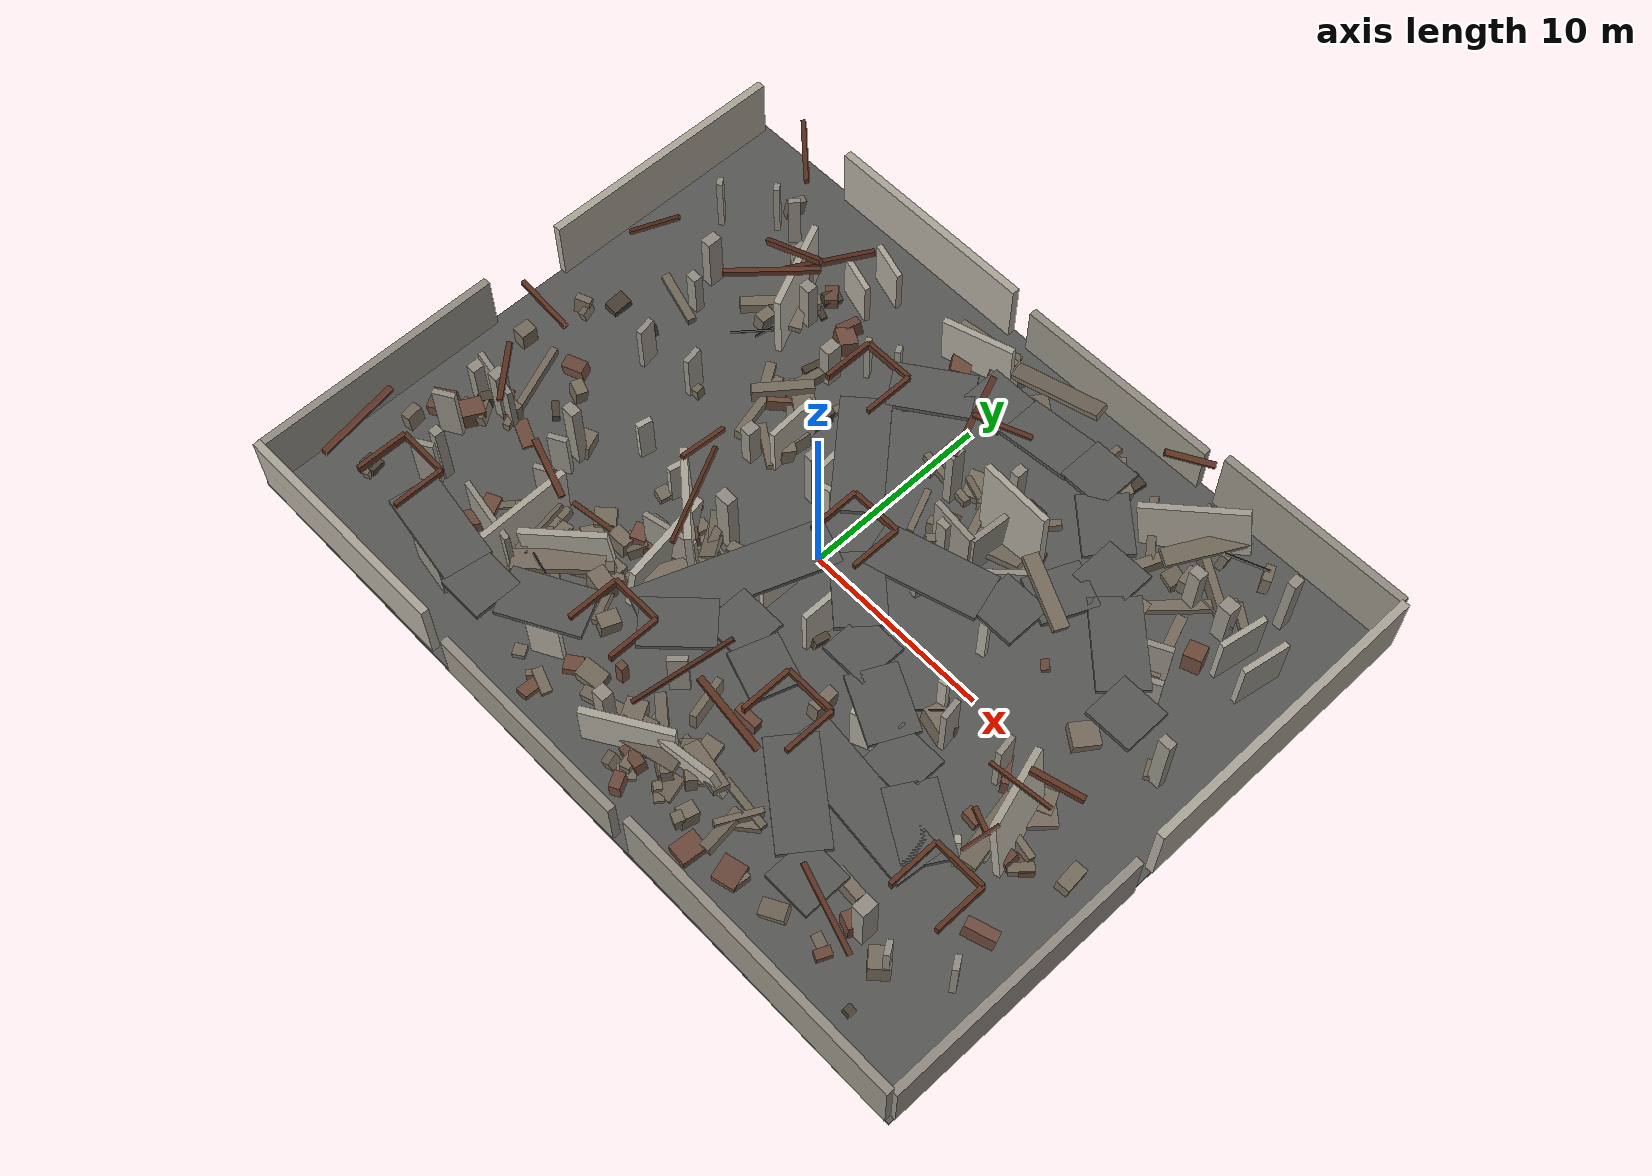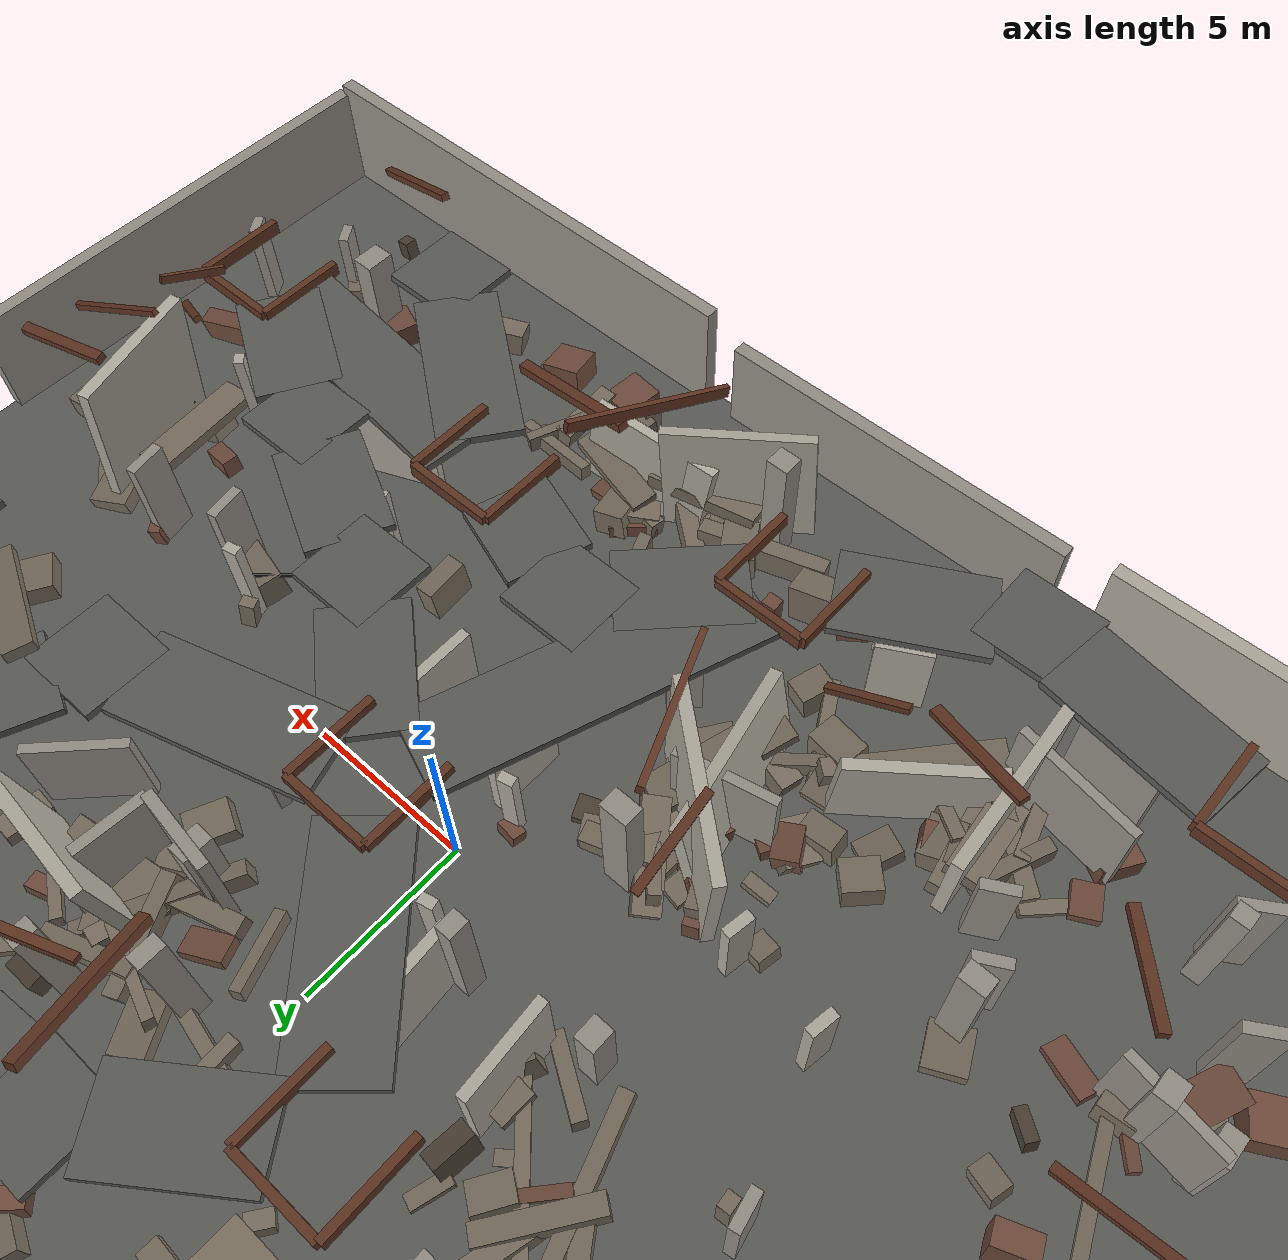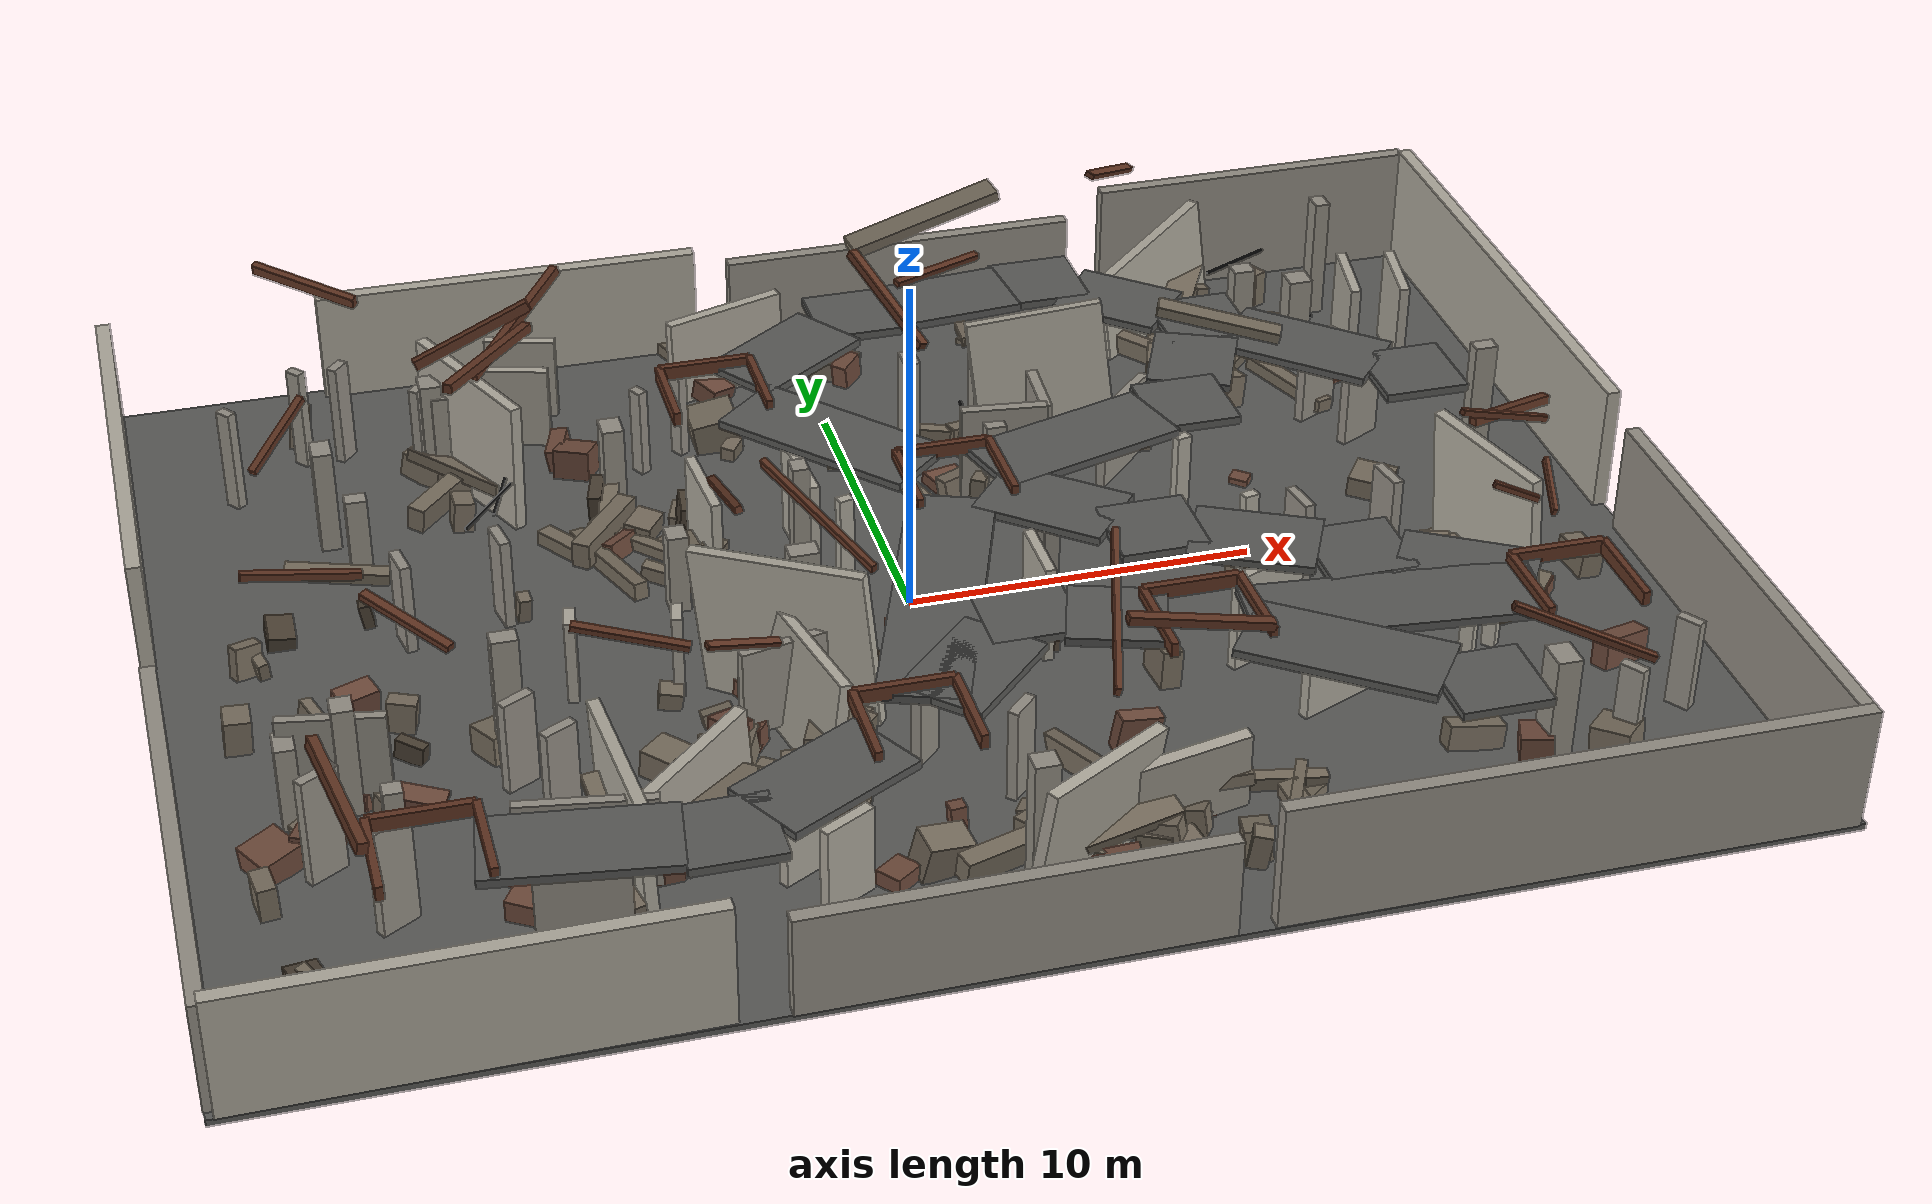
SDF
<?xml version="1.0" ?>
<sdf version="1.6">
  <world name="Ruins-Urban-01_challenge">
    <gravity>0 0 -9.81</gravity>
    <scene>
      <ambient>0.42 0.41 0.38 1</ambient>
      <background>0.48 0.49 0.50 1</background>
      <shadows>true</shadows>

    </scene>
    <physics name="ode_physics" type="ode">
      <max_step_size>0.004</max_step_size>
      <real_time_factor>1</real_time_factor>
      <real_time_update_rate>250</real_time_update_rate>
    </physics>
    <light name="ceiling_area_light" type="point">
      <pose>-11 0 6.8 0 0 0</pose>
      <diffuse>0.68 0.65 0.58 1</diffuse>
      <specular>0.05 0.05 0.05 1</specular>
      <attenuation><range>38</range><constant>0.7</constant><linear>0.02</linear><quadratic>0.002</quadratic></attenuation>
    </light>
    <light name="damaged_east_light" type="point">
      <pose>12 5 5.8 0 0 0</pose>
      <diffuse>0.42 0.48 0.50 1</diffuse>
      <specular>0.03 0.03 0.03 1</specular>
      <attenuation><range>25</range><constant>0.8</constant><linear>0.04</linear><quadratic>0.004</quadratic></attenuation>
    </light>
    <light name="lower_south_light" type="point">
      <pose>-5 -10 3.0 0 0 0</pose>
      <diffuse>0.38 0.31 0.25 1</diffuse>
      <specular>0.02 0.02 0.02 1</specular>
      <attenuation><range>19</range><constant>0.9</constant><linear>0.05</linear><quadratic>0.006</quadratic></attenuation>
    </light>
    <include>
      <uri>model://ruins_urban_01_challenge</uri>
    </include>
  </world>
</sdf>

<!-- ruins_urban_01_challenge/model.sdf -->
<sdf version="1.6">
  <model name="ruins_urban_01_challenge">
    <static>true</static>
    <link name="000_challenge_floor_slab">
      <pose>0.00000 0.00000 -0.10000 0.00000 0.00000 0.00000</pose>
      <visual name="visual">
        <geometry>
          <box><size>42.00000 32.00000 0.20000</size></box>
        </geometry>
          <material>
            <ambient>0.350 0.350 0.340 1</ambient>
            <diffuse>0.350 0.350 0.340 1</diffuse>
            <specular>0.03 0.03 0.03 1</specular>
          </material>
      </visual>
      <collision name="collision">
        <geometry>
          <box><size>42.00000 32.00000 0.20000</size></box>
        </geometry>
        <surface>
          <contact><collide_bitmask>0x01</collide_bitmask></contact>
          <friction>
            <ode><mu>1.0</mu><mu2>1.0</mu2></ode>
          </friction>
        </surface>
      </collision>
    </link>
    <link name="001_challenge_boundary_north_a">
      <pose>-8.65000 15.75000 1.70000 0.00000 0.00000 -0.00513</pose>
      <visual name="visual">
        <geometry>
          <box><size>11.70015 0.42000 3.40000</size></box>
        </geometry>
          <material>
            <ambient>0.680 0.660 0.610 1</ambient>
            <diffuse>0.680 0.660 0.610 1</diffuse>
            <specular>0.03 0.03 0.03 1</specular>
          </material>
      </visual>
      <collision name="collision">
        <geometry>
          <box><size>11.70015 0.42000 3.40000</size></box>
        </geometry>
        <surface>
          <contact><collide_bitmask>0x01</collide_bitmask></contact>
          <friction>
            <ode><mu>1.0</mu><mu2>1.0</mu2></ode>
          </friction>
        </surface>
      </collision>
    </link>
    <link name="002_challenge_boundary_north_b">
      <pose>3.85000 15.83000 1.40000 0.00000 0.00000 0.00541</pose>
      <visual name="visual">
        <geometry>
          <box><size>11.10016 0.42000 2.80000</size></box>
        </geometry>
          <material>
            <ambient>0.580 0.560 0.520 1</ambient>
            <diffuse>0.580 0.560 0.520 1</diffuse>
            <specular>0.03 0.03 0.03 1</specular>
          </material>
      </visual>
      <collision name="collision">
        <geometry>
          <box><size>11.10016 0.42000 2.80000</size></box>
        </geometry>
        <surface>
          <contact><collide_bitmask>0x01</collide_bitmask></contact>
          <friction>
            <ode><mu>1.0</mu><mu2>1.0</mu2></ode>
          </friction>
        </surface>
      </collision>
    </link>
    <link name="003_challenge_boundary_north_c">
      <pose>15.65000 15.79000 1.85000 0.00000 0.00000 0.00583</pose>
      <visual name="visual">
        <geometry>
          <box><size>10.30017 0.42000 3.70000</size></box>
        </geometry>
          <material>
            <ambient>0.580 0.560 0.520 1</ambient>
            <diffuse>0.580 0.560 0.520 1</diffuse>
            <specular>0.03 0.03 0.03 1</specular>
          </material>
      </visual>
      <collision name="collision">
        <geometry>
          <box><size>10.30017 0.42000 3.70000</size></box>
        </geometry>
        <surface>
          <contact><collide_bitmask>0x01</collide_bitmask></contact>
          <friction>
            <ode><mu>1.0</mu><mu2>1.0</mu2></ode>
          </friction>
        </surface>
      </collision>
    </link>
    <link name="004_challenge_boundary_south_a">
      <pose>-14.65000 -15.78000 1.75000 0.00000 0.00000 0.00650</pose>
      <visual name="visual">
        <geometry>
          <box><size>12.30026 0.42000 3.50000</size></box>
        </geometry>
          <material>
            <ambient>0.680 0.660 0.610 1</ambient>
            <diffuse>0.680 0.660 0.610 1</diffuse>
            <specular>0.03 0.03 0.03 1</specular>
          </material>
      </visual>
      <collision name="collision">
        <geometry>
          <box><size>12.30026 0.42000 3.50000</size></box>
        </geometry>
        <surface>
          <contact><collide_bitmask>0x01</collide_bitmask></contact>
          <friction>
            <ode><mu>1.0</mu><mu2>1.0</mu2></ode>
          </friction>
        </surface>
      </collision>
    </link>
    <link name="005_challenge_boundary_south_b">
      <pose>-1.60000 -15.81000 1.45000 0.00000 0.00000 0.00536</pose>
      <visual name="visual">
        <geometry>
          <box><size>11.20016 0.42000 2.90000</size></box>
        </geometry>
          <material>
            <ambient>0.580 0.560 0.520 1</ambient>
            <diffuse>0.580 0.560 0.520 1</diffuse>
            <specular>0.03 0.03 0.03 1</specular>
          </material>
      </visual>
      <collision name="collision">
        <geometry>
          <box><size>11.20016 0.42000 2.90000</size></box>
        </geometry>
        <surface>
          <contact><collide_bitmask>0x01</collide_bitmask></contact>
          <friction>
            <ode><mu>1.0</mu><mu2>1.0</mu2></ode>
          </friction>
        </surface>
      </collision>
    </link>
    <link name="006_challenge_boundary_south_c">
      <pose>12.90000 -15.80000 1.80000 0.00000 0.00000 -0.00506</pose>
      <visual name="visual">
        <geometry>
          <box><size>15.80020 0.42000 3.60000</size></box>
        </geometry>
          <material>
            <ambient>0.580 0.560 0.520 1</ambient>
            <diffuse>0.580 0.560 0.520 1</diffuse>
            <specular>0.03 0.03 0.03 1</specular>
          </material>
      </visual>
      <collision name="collision">
        <geometry>
          <box><size>15.80020 0.42000 3.60000</size></box>
        </geometry>
        <surface>
          <contact><collide_bitmask>0x01</collide_bitmask></contact>
          <friction>
            <ode><mu>1.0</mu><mu2>1.0</mu2></ode>
          </friction>
        </surface>
      </collision>
    </link>
    <link name="007_challenge_boundary_west_n">
      <pose>-20.87000 8.97500 1.70000 0.00000 0.00000 -1.57522</pose>
      <visual name="visual">
        <geometry>
          <box><size>13.55013 0.42000 3.40000</size></box>
        </geometry>
          <material>
            <ambient>0.680 0.660 0.610 1</ambient>
            <diffuse>0.680 0.660 0.610 1</diffuse>
            <specular>0.03 0.03 0.03 1</specular>
          </material>
      </visual>
      <collision name="collision">
        <geometry>
          <box><size>13.55013 0.42000 3.40000</size></box>
        </geometry>
        <surface>
          <contact><collide_bitmask>0x01</collide_bitmask></contact>
          <friction>
            <ode><mu>1.0</mu><mu2>1.0</mu2></ode>
          </friction>
        </surface>
      </collision>
    </link>
    <link name="008_challenge_boundary_west_s">
      <pose>-20.85000 -8.97500 1.60000 0.00000 0.00000 -1.56637</pose>
      <visual name="visual">
        <geometry>
          <box><size>13.55013 0.42000 3.20000</size></box>
        </geometry>
          <material>
            <ambient>0.580 0.560 0.520 1</ambient>
            <diffuse>0.580 0.560 0.520 1</diffuse>
            <specular>0.03 0.03 0.03 1</specular>
          </material>
      </visual>
      <collision name="collision">
        <geometry>
          <box><size>13.55013 0.42000 3.20000</size></box>
        </geometry>
        <surface>
          <contact><collide_bitmask>0x01</collide_bitmask></contact>
          <friction>
            <ode><mu>1.0</mu><mu2>1.0</mu2></ode>
          </friction>
        </surface>
      </collision>
    </link>
    <link name="009_challenge_boundary_east_a">
      <pose>20.88000 -8.60000 1.65000 0.00000 0.00000 1.56516</pose>
      <visual name="visual">
        <geometry>
          <box><size>14.20023 0.42000 3.30000</size></box>
        </geometry>
          <material>
            <ambient>0.580 0.560 0.520 1</ambient>
            <diffuse>0.580 0.560 0.520 1</diffuse>
            <specular>0.03 0.03 0.03 1</specular>
          </material>
      </visual>
      <collision name="collision">
        <geometry>
          <box><size>14.20023 0.42000 3.30000</size></box>
        </geometry>
        <surface>
          <contact><collide_bitmask>0x01</collide_bitmask></contact>
          <friction>
            <ode><mu>1.0</mu><mu2>1.0</mu2></ode>
          </friction>
        </surface>
      </collision>
    </link>
    <link name="010_challenge_boundary_east_b">
      <pose>20.88000 7.70000 1.90000 0.00000 0.00000 1.56830</pose>
      <visual name="visual">
        <geometry>
          <box><size>16.00005 0.42000 3.80000</size></box>
        </geometry>
          <material>
            <ambient>0.680 0.660 0.610 1</ambient>
            <diffuse>0.680 0.660 0.610 1</diffuse>
            <specular>0.03 0.03 0.03 1</specular>
          </material>
      </visual>
      <collision name="collision">
        <geometry>
          <box><size>16.00005 0.42000 3.80000</size></box>
        </geometry>
        <surface>
          <contact><collide_bitmask>0x01</collide_bitmask></contact>
          <friction>
            <ode><mu>1.0</mu><mu2>1.0</mu2></ode>
          </friction>
        </surface>
      </collision>
    </link>
    <link name="011_challenge_ground_corridor_g4_g5_left">
      <pose>-1.40840 1.90168 1.27500 0.00000 0.00000 0.23554</pose>
      <visual name="visual">
        <geometry>
          <box><size>0.44198 0.30000 2.55000</size></box>
        </geometry>
          <material>
            <ambient>0.680 0.660 0.610 1</ambient>
            <diffuse>0.680 0.660 0.610 1</diffuse>
            <specular>0.03 0.03 0.03 1</specular>
          </material>
      </visual>
      <collision name="collision">
        <geometry>
          <box><size>0.44198 0.30000 2.55000</size></box>
        </geometry>
        <surface>
          <contact><collide_bitmask>0x01</collide_bitmask></contact>
          <friction>
            <ode><mu>1.0</mu><mu2>1.0</mu2></ode>
          </friction>
        </surface>
      </collision>
    </link>
    <link name="012_challenge_ground_corridor_g4_g5_right">
      <pose>-0.59160 -1.50168 1.27500 0.00000 0.00000 0.23554</pose>
      <visual name="visual">
        <geometry>
          <box><size>0.44198 0.30000 2.55000</size></box>
        </geometry>
          <material>
            <ambient>0.680 0.660 0.610 1</ambient>
            <diffuse>0.680 0.660 0.610 1</diffuse>
            <specular>0.03 0.03 0.03 1</specular>
          </material>
      </visual>
      <collision name="collision">
        <geometry>
          <box><size>0.44198 0.30000 2.55000</size></box>
        </geometry>
        <surface>
          <contact><collide_bitmask>0x01</collide_bitmask></contact>
          <friction>
            <ode><mu>1.0</mu><mu2>1.0</mu2></ode>
          </friction>
        </surface>
      </collision>
    </link>
    <link name="013_challenge_ground_corridor_g5_g6_left">
      <pose>4.37601 1.95913 1.37500 0.00000 0.00000 -0.21655</pose>
      <visual name="visual">
        <geometry>
          <box><size>0.41957 0.30000 2.75000</size></box>
        </geometry>
          <material>
            <ambient>0.580 0.560 0.520 1</ambient>
            <diffuse>0.580 0.560 0.520 1</diffuse>
            <specular>0.03 0.03 0.03 1</specular>
          </material>
      </visual>
      <collision name="collision">
        <geometry>
          <box><size>0.41957 0.30000 2.75000</size></box>
        </geometry>
        <surface>
          <contact><collide_bitmask>0x01</collide_bitmask></contact>
          <friction>
            <ode><mu>1.0</mu><mu2>1.0</mu2></ode>
          </friction>
        </surface>
      </collision>
    </link>
    <link name="014_challenge_ground_corridor_g5_g6_right">
      <pose>3.62399 -1.45913 1.37500 0.00000 0.00000 -0.21655</pose>
      <visual name="visual">
        <geometry>
          <box><size>0.41957 0.30000 2.75000</size></box>
        </geometry>
          <material>
            <ambient>0.580 0.560 0.520 1</ambient>
            <diffuse>0.580 0.560 0.520 1</diffuse>
            <specular>0.03 0.03 0.03 1</specular>
          </material>
      </visual>
      <collision name="collision">
        <geometry>
          <box><size>0.41957 0.30000 2.75000</size></box>
        </geometry>
        <surface>
          <contact><collide_bitmask>0x01</collide_bitmask></contact>
          <friction>
            <ode><mu>1.0</mu><mu2>1.0</mu2></ode>
          </friction>
        </surface>
      </collision>
    </link>
    <link name="015_challenge_ground_corridor_g6_g7_left">
      <pose>8.59160 2.00168 1.47500 0.00000 0.00000 0.23554</pose>
      <visual name="visual">
        <geometry>
          <box><size>0.44198 0.30000 2.95000</size></box>
        </geometry>
          <material>
            <ambient>0.680 0.660 0.610 1</ambient>
            <diffuse>0.680 0.660 0.610 1</diffuse>
            <specular>0.03 0.03 0.03 1</specular>
          </material>
      </visual>
      <collision name="collision">
        <geometry>
          <box><size>0.44198 0.30000 2.95000</size></box>
        </geometry>
        <surface>
          <contact><collide_bitmask>0x01</collide_bitmask></contact>
          <friction>
            <ode><mu>1.0</mu><mu2>1.0</mu2></ode>
          </friction>
        </surface>
      </collision>
    </link>
    <link name="016_challenge_ground_corridor_g6_g7_right">
      <pose>9.40840 -1.40168 1.47500 0.00000 0.00000 0.23554</pose>
      <visual name="visual">
        <geometry>
          <box><size>0.44198 0.30000 2.95000</size></box>
        </geometry>
          <material>
            <ambient>0.680 0.660 0.610 1</ambient>
            <diffuse>0.680 0.660 0.610 1</diffuse>
            <specular>0.03 0.03 0.03 1</specular>
          </material>
      </visual>
      <collision name="collision">
        <geometry>
          <box><size>0.44198 0.30000 2.95000</size></box>
        </geometry>
        <surface>
          <contact><collide_bitmask>0x01</collide_bitmask></contact>
          <friction>
            <ode><mu>1.0</mu><mu2>1.0</mu2></ode>
          </friction>
        </surface>
      </collision>
    </link>
    <link name="017_challenge_ground_corridor_g2_n1_left">
      <pose>-13.90281 1.74950 1.37500 0.00000 0.00000 1.74751</pose>
      <visual name="visual">
        <geometry>
          <box><size>0.98859 0.30000 2.75000</size></box>
        </geometry>
          <material>
            <ambient>0.580 0.560 0.520 1</ambient>
            <diffuse>0.580 0.560 0.520 1</diffuse>
            <specular>0.03 0.03 0.03 1</specular>
          </material>
      </visual>
      <collision name="collision">
        <geometry>
          <box><size>0.98859 0.30000 2.75000</size></box>
        </geometry>
        <surface>
          <contact><collide_bitmask>0x01</collide_bitmask></contact>
          <friction>
            <ode><mu>1.0</mu><mu2>1.0</mu2></ode>
          </friction>
        </surface>
      </collision>
    </link>
    <link name="018_challenge_ground_corridor_g2_n1_right">
      <pose>-11.09719 2.25050 1.37500 0.00000 0.00000 1.74751</pose>
      <visual name="visual">
        <geometry>
          <box><size>0.98859 0.30000 2.75000</size></box>
        </geometry>
          <material>
            <ambient>0.580 0.560 0.520 1</ambient>
            <diffuse>0.580 0.560 0.520 1</diffuse>
            <specular>0.03 0.03 0.03 1</specular>
          </material>
      </visual>
      <collision name="collision">
        <geometry>
          <box><size>0.98859 0.30000 2.75000</size></box>
        </geometry>
        <surface>
          <contact><collide_bitmask>0x01</collide_bitmask></contact>
          <friction>
            <ode><mu>1.0</mu><mu2>1.0</mu2></ode>
          </friction>
        </surface>
      </collision>
    </link>
    <link name="019_challenge_ground_corridor_n2_n3_left">
      <pose>-14.32242 11.93837 1.57500 0.00000 0.00000 0.85197</pose>
      <visual name="visual">
        <geometry>
          <box><size>0.61507 0.30000 3.15000</size></box>
        </geometry>
          <material>
            <ambient>0.580 0.560 0.520 1</ambient>
            <diffuse>0.580 0.560 0.520 1</diffuse>
            <specular>0.03 0.03 0.03 1</specular>
          </material>
      </visual>
      <collision name="collision">
        <geometry>
          <box><size>0.61507 0.30000 3.15000</size></box>
        </geometry>
        <surface>
          <contact><collide_bitmask>0x01</collide_bitmask></contact>
          <friction>
            <ode><mu>1.0</mu><mu2>1.0</mu2></ode>
          </friction>
        </surface>
      </collision>
    </link>
    <link name="020_challenge_ground_corridor_n2_n3_right">
      <pose>-12.17758 10.06163 1.57500 0.00000 0.00000 0.85197</pose>
      <visual name="visual">
        <geometry>
          <box><size>0.61507 0.30000 3.15000</size></box>
        </geometry>
          <material>
            <ambient>0.580 0.560 0.520 1</ambient>
            <diffuse>0.580 0.560 0.520 1</diffuse>
            <specular>0.03 0.03 0.03 1</specular>
          </material>
      </visual>
      <collision name="collision">
        <geometry>
          <box><size>0.61507 0.30000 3.15000</size></box>
        </geometry>
        <surface>
          <contact><collide_bitmask>0x01</collide_bitmask></contact>
          <friction>
            <ode><mu>1.0</mu><mu2>1.0</mu2></ode>
          </friction>
        </surface>
      </collision>
    </link>
    <link name="021_challenge_ground_corridor_n3_n4_left">
      <pose>-8.74857 13.08810 1.27500 0.00000 0.00000 -0.29146</pose>
      <visual name="visual">
        <geometry>
          <box><size>2.12015 0.30000 2.55000</size></box>
        </geometry>
          <material>
            <ambient>0.680 0.660 0.610 1</ambient>
            <diffuse>0.680 0.660 0.610 1</diffuse>
            <specular>0.03 0.03 0.03 1</specular>
          </material>
      </visual>
      <collision name="collision">
        <geometry>
          <box><size>2.12015 0.30000 2.55000</size></box>
        </geometry>
        <surface>
          <contact><collide_bitmask>0x01</collide_bitmask></contact>
          <friction>
            <ode><mu>1.0</mu><mu2>1.0</mu2></ode>
          </friction>
        </surface>
      </collision>
    </link>
    <link name="022_challenge_ground_corridor_n3_n4_right">
      <pose>-9.25143 11.41190 1.27500 0.00000 0.00000 -0.29146</pose>
      <visual name="visual">
        <geometry>
          <box><size>2.12015 0.30000 2.55000</size></box>
        </geometry>
          <material>
            <ambient>0.680 0.660 0.610 1</ambient>
            <diffuse>0.680 0.660 0.610 1</diffuse>
            <specular>0.03 0.03 0.03 1</specular>
          </material>
      </visual>
      <collision name="collision">
        <geometry>
          <box><size>2.12015 0.30000 2.55000</size></box>
        </geometry>
        <surface>
          <contact><collide_bitmask>0x01</collide_bitmask></contact>
          <friction>
            <ode><mu>1.0</mu><mu2>1.0</mu2></ode>
          </friction>
        </surface>
      </collision>
    </link>
    <link name="023_challenge_ground_corridor_n4_n5_left">
      <pose>-4.58564 9.61909 1.37500 0.00000 0.00000 -1.06370</pose>
      <visual name="visual">
        <geometry>
          <box><size>0.44782 0.30000 2.75000</size></box>
        </geometry>
          <material>
            <ambient>0.580 0.560 0.520 1</ambient>
            <diffuse>0.580 0.560 0.520 1</diffuse>
            <specular>0.03 0.03 0.03 1</specular>
          </material>
      </visual>
      <collision name="collision">
        <geometry>
          <box><size>0.44782 0.30000 2.75000</size></box>
        </geometry>
        <surface>
          <contact><collide_bitmask>0x01</collide_bitmask></contact>
          <friction>
            <ode><mu>1.0</mu><mu2>1.0</mu2></ode>
          </friction>
        </surface>
      </collision>
    </link>
    <link name="024_challenge_ground_corridor_n4_n5_right">
      <pose>-5.91436 8.88091 1.37500 0.00000 0.00000 -1.06370</pose>
      <visual name="visual">
        <geometry>
          <box><size>0.44782 0.30000 2.75000</size></box>
        </geometry>
          <material>
            <ambient>0.580 0.560 0.520 1</ambient>
            <diffuse>0.580 0.560 0.520 1</diffuse>
            <specular>0.03 0.03 0.03 1</specular>
          </material>
      </visual>
      <collision name="collision">
        <geometry>
          <box><size>0.44782 0.30000 2.75000</size></box>
        </geometry>
        <surface>
          <contact><collide_bitmask>0x01</collide_bitmask></contact>
          <friction>
            <ode><mu>1.0</mu><mu2>1.0</mu2></ode>
          </friction>
        </surface>
      </collision>
    </link>
    <link name="025_challenge_ground_corridor_n5_g4_left">
      <pose>-2.32824 3.39606 1.47500 0.00000 0.00000 -1.50333</pose>
      <visual name="visual">
        <geometry>
          <box><size>2.71687 0.30000 2.95000</size></box>
        </geometry>
          <material>
            <ambient>0.680 0.660 0.610 1</ambient>
            <diffuse>0.680 0.660 0.610 1</diffuse>
            <specular>0.03 0.03 0.03 1</specular>
          </material>
      </visual>
      <collision name="collision">
        <geometry>
          <box><size>2.71687 0.30000 2.95000</size></box>
        </geometry>
        <surface>
          <contact><collide_bitmask>0x01</collide_bitmask></contact>
          <friction>
            <ode><mu>1.0</mu><mu2>1.0</mu2></ode>
          </friction>
        </surface>
      </collision>
    </link>
    <link name="026_challenge_ground_corridor_n5_g4_right">
      <pose>-5.17176 3.20394 1.47500 0.00000 0.00000 -1.50333</pose>
      <visual name="visual">
        <geometry>
          <box><size>2.71687 0.30000 2.95000</size></box>
        </geometry>
          <material>
            <ambient>0.680 0.660 0.610 1</ambient>
            <diffuse>0.680 0.660 0.610 1</diffuse>
            <specular>0.03 0.03 0.03 1</specular>
          </material>
      </visual>
      <collision name="collision">
        <geometry>
          <box><size>2.71687 0.30000 2.95000</size></box>
        </geometry>
        <surface>
          <contact><collide_bitmask>0x01</collide_bitmask></contact>
          <friction>
            <ode><mu>1.0</mu><mu2>1.0</mu2></ode>
          </friction>
        </surface>
      </collision>
    </link>
    <link name="027_challenge_ground_corridor_n2_dead_nw_left">
      <pose>-17.74921 10.09315 1.57500 0.00000 0.00000 2.26060</pose>
      <visual name="visual">
        <geometry>
          <box><size>0.48556 0.30000 3.15000</size></box>
        </geometry>
          <material>
            <ambient>0.580 0.560 0.520 1</ambient>
            <diffuse>0.580 0.560 0.520 1</diffuse>
            <specular>0.03 0.03 0.03 1</specular>
          </material>
      </visual>
      <collision name="collision">
        <geometry>
          <box><size>0.48556 0.30000 3.15000</size></box>
        </geometry>
        <surface>
          <contact><collide_bitmask>0x01</collide_bitmask></contact>
          <friction>
            <ode><mu>1.0</mu><mu2>1.0</mu2></ode>
          </friction>
        </surface>
      </collision>
    </link>
    <link name="028_challenge_ground_corridor_n2_dead_nw_right">
      <pose>-15.55079 11.90685 1.57500 0.00000 0.00000 2.26060</pose>
      <visual name="visual">
        <geometry>
          <box><size>0.48556 0.30000 3.15000</size></box>
        </geometry>
          <material>
            <ambient>0.580 0.560 0.520 1</ambient>
            <diffuse>0.580 0.560 0.520 1</diffuse>
            <specular>0.03 0.03 0.03 1</specular>
          </material>
      </visual>
      <collision name="collision">
        <geometry>
          <box><size>0.48556 0.30000 3.15000</size></box>
        </geometry>
        <surface>
          <contact><collide_bitmask>0x01</collide_bitmask></contact>
          <friction>
            <ode><mu>1.0</mu><mu2>1.0</mu2></ode>
          </friction>
        </surface>
      </collision>
    </link>
    <link name="029_challenge_ground_corridor_g3_s1_left">
      <pose>-7.09882 -2.35948 1.27500 0.00000 0.00000 -1.75391</pose>
      <visual name="visual">
        <geometry>
          <box><size>0.79181 0.30000 2.55000</size></box>
        </geometry>
          <material>
            <ambient>0.680 0.660 0.610 1</ambient>
            <diffuse>0.680 0.660 0.610 1</diffuse>
            <specular>0.03 0.03 0.03 1</specular>
          </material>
      </visual>
      <collision name="collision">
        <geometry>
          <box><size>0.79181 0.30000 2.55000</size></box>
        </geometry>
        <surface>
          <contact><collide_bitmask>0x01</collide_bitmask></contact>
          <friction>
            <ode><mu>1.0</mu><mu2>1.0</mu2></ode>
          </friction>
        </surface>
      </collision>
    </link>
    <link name="030_challenge_ground_corridor_g3_s1_right">
      <pose>-9.90118 -1.84052 1.27500 0.00000 0.00000 -1.75391</pose>
      <visual name="visual">
        <geometry>
          <box><size>0.79181 0.30000 2.55000</size></box>
        </geometry>
          <material>
            <ambient>0.680 0.660 0.610 1</ambient>
            <diffuse>0.680 0.660 0.610 1</diffuse>
            <specular>0.03 0.03 0.03 1</specular>
          </material>
      </visual>
      <collision name="collision">
        <geometry>
          <box><size>0.79181 0.30000 2.55000</size></box>
        </geometry>
        <surface>
          <contact><collide_bitmask>0x01</collide_bitmask></contact>
          <friction>
            <ode><mu>1.0</mu><mu2>1.0</mu2></ode>
          </friction>
        </surface>
      </collision>
    </link>
    <link name="031_challenge_ground_corridor_s1_s2_left">
      <pose>-11.08424 -6.91992 1.37500 0.00000 0.00000 -2.64646</pose>
      <visual name="visual">
        <geometry>
          <box><size>0.98243 0.30000 2.75000</size></box>
        </geometry>
          <material>
            <ambient>0.580 0.560 0.520 1</ambient>
            <diffuse>0.580 0.560 0.520 1</diffuse>
            <specular>0.03 0.03 0.03 1</specular>
          </material>
      </visual>
      <collision name="collision">
        <geometry>
          <box><size>0.98243 0.30000 2.75000</size></box>
        </geometry>
        <surface>
          <contact><collide_bitmask>0x01</collide_bitmask></contact>
          <friction>
            <ode><mu>1.0</mu><mu2>1.0</mu2></ode>
          </friction>
        </surface>
      </collision>
    </link>
    <link name="032_challenge_ground_corridor_s1_s2_right">
      <pose>-11.91576 -5.38008 1.37500 0.00000 0.00000 -2.64646</pose>
      <visual name="visual">
        <geometry>
          <box><size>0.98243 0.30000 2.75000</size></box>
        </geometry>
          <material>
            <ambient>0.580 0.560 0.520 1</ambient>
            <diffuse>0.580 0.560 0.520 1</diffuse>
            <specular>0.03 0.03 0.03 1</specular>
          </material>
      </visual>
      <collision name="collision">
        <geometry>
          <box><size>0.98243 0.30000 2.75000</size></box>
        </geometry>
        <surface>
          <contact><collide_bitmask>0x01</collide_bitmask></contact>
          <friction>
            <ode><mu>1.0</mu><mu2>1.0</mu2></ode>
          </friction>
        </surface>
      </collision>
    </link>
    <link name="033_challenge_ground_corridor_s3_s4_left">
      <pose>-11.37626 -11.63379 1.57500 0.00000 0.00000 -0.14190</pose>
      <visual name="visual">
        <geometry>
          <box><size>2.37107 0.30000 3.15000</size></box>
        </geometry>
          <material>
            <ambient>0.580 0.560 0.520 1</ambient>
            <diffuse>0.580 0.560 0.520 1</diffuse>
            <specular>0.03 0.03 0.03 1</specular>
          </material>
      </visual>
      <collision name="collision">
        <geometry>
          <box><size>2.37107 0.30000 3.15000</size></box>
        </geometry>
        <surface>
          <contact><collide_bitmask>0x01</collide_bitmask></contact>
          <friction>
            <ode><mu>1.0</mu><mu2>1.0</mu2></ode>
          </friction>
        </surface>
      </collision>
    </link>
    <link name="034_challenge_ground_corridor_s3_s4_right">
      <pose>-11.62374 -13.36621 1.57500 0.00000 0.00000 -0.14190</pose>
      <visual name="visual">
        <geometry>
          <box><size>2.37107 0.30000 3.15000</size></box>
        </geometry>
          <material>
            <ambient>0.580 0.560 0.520 1</ambient>
            <diffuse>0.580 0.560 0.520 1</diffuse>
            <specular>0.03 0.03 0.03 1</specular>
          </material>
      </visual>
      <collision name="collision">
        <geometry>
          <box><size>2.37107 0.30000 3.15000</size></box>
        </geometry>
        <surface>
          <contact><collide_bitmask>0x01</collide_bitmask></contact>
          <friction>
            <ode><mu>1.0</mu><mu2>1.0</mu2></ode>
          </friction>
        </surface>
      </collision>
    </link>
    <link name="035_challenge_ground_corridor_s4_s5_left">
      <pose>-5.61393 -10.83280 1.27500 0.00000 0.00000 0.49935</pose>
      <visual name="visual">
        <geometry>
          <box><size>1.56498 0.30000 2.55000</size></box>
        </geometry>
          <material>
            <ambient>0.680 0.660 0.610 1</ambient>
            <diffuse>0.680 0.660 0.610 1</diffuse>
            <specular>0.03 0.03 0.03 1</specular>
          </material>
      </visual>
      <collision name="collision">
        <geometry>
          <box><size>1.56498 0.30000 2.55000</size></box>
        </geometry>
        <surface>
          <contact><collide_bitmask>0x01</collide_bitmask></contact>
          <friction>
            <ode><mu>1.0</mu><mu2>1.0</mu2></ode>
          </friction>
        </surface>
      </collision>
    </link>
    <link name="036_challenge_ground_corridor_s4_s5_right">
      <pose>-4.88607 -12.16720 1.27500 0.00000 0.00000 0.49935</pose>
      <visual name="visual">
        <geometry>
          <box><size>1.56498 0.30000 2.55000</size></box>
        </geometry>
          <material>
            <ambient>0.680 0.660 0.610 1</ambient>
            <diffuse>0.680 0.660 0.610 1</diffuse>
            <specular>0.03 0.03 0.03 1</specular>
          </material>
      </visual>
      <collision name="collision">
        <geometry>
          <box><size>1.56498 0.30000 2.55000</size></box>
        </geometry>
        <surface>
          <contact><collide_bitmask>0x01</collide_bitmask></contact>
          <friction>
            <ode><mu>1.0</mu><mu2>1.0</mu2></ode>
          </friction>
        </surface>
      </collision>
    </link>
    <link name="037_challenge_ground_corridor_s5_s6_left">
      <pose>-1.50763 -6.99237 1.37500 0.00000 0.00000 0.78540</pose>
      <visual name="visual">
        <geometry>
          <box><size>0.95685 0.30000 2.75000</size></box>
        </geometry>
          <material>
            <ambient>0.580 0.560 0.520 1</ambient>
            <diffuse>0.580 0.560 0.520 1</diffuse>
            <specular>0.03 0.03 0.03 1</specular>
          </material>
      </visual>
      <collision name="collision">
        <geometry>
          <box><size>0.95685 0.30000 2.75000</size></box>
        </geometry>
        <surface>
          <contact><collide_bitmask>0x01</collide_bitmask></contact>
          <friction>
            <ode><mu>1.0</mu><mu2>1.0</mu2></ode>
          </friction>
        </surface>
      </collision>
    </link>
    <link name="038_challenge_ground_corridor_s5_s6_right">
      <pose>0.50763 -9.00763 1.37500 0.00000 0.00000 0.78540</pose>
      <visual name="visual">
        <geometry>
          <box><size>0.95685 0.30000 2.75000</size></box>
        </geometry>
          <material>
            <ambient>0.580 0.560 0.520 1</ambient>
            <diffuse>0.580 0.560 0.520 1</diffuse>
            <specular>0.03 0.03 0.03 1</specular>
          </material>
      </visual>
      <collision name="collision">
        <geometry>
          <box><size>0.95685 0.30000 2.75000</size></box>
        </geometry>
        <surface>
          <contact><collide_bitmask>0x01</collide_bitmask></contact>
          <friction>
            <ode><mu>1.0</mu><mu2>1.0</mu2></ode>
          </friction>
        </surface>
      </collision>
    </link>
    <link name="039_challenge_ground_corridor_s6_g5_left">
      <pose>0.07500 -2.60000 1.47500 0.00000 0.00000 1.57080</pose>
      <visual name="visual">
        <geometry>
          <box><size>2.10000 0.30000 2.95000</size></box>
        </geometry>
          <material>
            <ambient>0.680 0.660 0.610 1</ambient>
            <diffuse>0.680 0.660 0.610 1</diffuse>
            <specular>0.03 0.03 0.03 1</specular>
          </material>
      </visual>
      <collision name="collision">
        <geometry>
          <box><size>2.10000 0.30000 2.95000</size></box>
        </geometry>
        <surface>
          <contact><collide_bitmask>0x01</collide_bitmask></contact>
          <friction>
            <ode><mu>1.0</mu><mu2>1.0</mu2></ode>
          </friction>
        </surface>
      </collision>
    </link>
    <link name="040_challenge_ground_corridor_s6_g5_right">
      <pose>2.92500 -2.60000 1.47500 0.00000 0.00000 1.57080</pose>
      <visual name="visual">
        <geometry>
          <box><size>2.10000 0.30000 2.95000</size></box>
        </geometry>
          <material>
            <ambient>0.680 0.660 0.610 1</ambient>
            <diffuse>0.680 0.660 0.610 1</diffuse>
            <specular>0.03 0.03 0.03 1</specular>
          </material>
      </visual>
      <collision name="collision">
        <geometry>
          <box><size>2.10000 0.30000 2.95000</size></box>
        </geometry>
        <surface>
          <contact><collide_bitmask>0x01</collide_bitmask></contact>
          <friction>
            <ode><mu>1.0</mu><mu2>1.0</mu2></ode>
          </friction>
        </surface>
      </collision>
    </link>
    <link name="041_challenge_ground_corridor_s2_dead_sw_left">
      <pose>-15.76684 -10.22193 1.57500 0.00000 0.00000 -2.60117</pose>
      <visual name="visual">
        <geometry>
          <box><size>1.13095 0.30000 3.15000</size></box>
        </geometry>
          <material>
            <ambient>0.580 0.560 0.520 1</ambient>
            <diffuse>0.580 0.560 0.520 1</diffuse>
            <specular>0.03 0.03 0.03 1</specular>
          </material>
      </visual>
      <collision name="collision">
        <geometry>
          <box><size>1.13095 0.30000 3.15000</size></box>
        </geometry>
        <surface>
          <contact><collide_bitmask>0x01</collide_bitmask></contact>
          <friction>
            <ode><mu>1.0</mu><mu2>1.0</mu2></ode>
          </friction>
        </surface>
      </collision>
    </link>
    <link name="042_challenge_ground_corridor_s2_dead_sw_right">
      <pose>-17.23316 -7.77807 1.57500 0.00000 0.00000 -2.60117</pose>
      <visual name="visual">
        <geometry>
          <box><size>1.13095 0.30000 3.15000</size></box>
        </geometry>
          <material>
            <ambient>0.580 0.560 0.520 1</ambient>
            <diffuse>0.580 0.560 0.520 1</diffuse>
            <specular>0.03 0.03 0.03 1</specular>
          </material>
      </visual>
      <collision name="collision">
        <geometry>
          <box><size>1.13095 0.30000 3.15000</size></box>
        </geometry>
        <surface>
          <contact><collide_bitmask>0x01</collide_bitmask></contact>
          <friction>
            <ode><mu>1.0</mu><mu2>1.0</mu2></ode>
          </friction>
        </surface>
      </collision>
    </link>
    <link name="043_challenge_ground_corridor_en1_en2_left">
      <pose>14.60869 6.78262 1.37500 0.00000 0.00000 0.46365</pose>
      <visual name="visual">
        <geometry>
          <box><size>1.37214 0.30000 2.75000</size></box>
        </geometry>
          <material>
            <ambient>0.580 0.560 0.520 1</ambient>
            <diffuse>0.580 0.560 0.520 1</diffuse>
            <specular>0.03 0.03 0.03 1</specular>
          </material>
      </visual>
      <collision name="collision">
        <geometry>
          <box><size>1.37214 0.30000 2.75000</size></box>
        </geometry>
        <surface>
          <contact><collide_bitmask>0x01</collide_bitmask></contact>
          <friction>
            <ode><mu>1.0</mu><mu2>1.0</mu2></ode>
          </friction>
        </surface>
      </collision>
    </link>
    <link name="044_challenge_ground_corridor_en1_en2_right">
      <pose>15.39131 5.21738 1.37500 0.00000 0.00000 0.46365</pose>
      <visual name="visual">
        <geometry>
          <box><size>1.37214 0.30000 2.75000</size></box>
        </geometry>
          <material>
            <ambient>0.580 0.560 0.520 1</ambient>
            <diffuse>0.580 0.560 0.520 1</diffuse>
            <specular>0.03 0.03 0.03 1</specular>
          </material>
      </visual>
      <collision name="collision">
        <geometry>
          <box><size>1.37214 0.30000 2.75000</size></box>
        </geometry>
        <surface>
          <contact><collide_bitmask>0x01</collide_bitmask></contact>
          <friction>
            <ode><mu>1.0</mu><mu2>1.0</mu2></ode>
          </friction>
        </surface>
      </collision>
    </link>
    <link name="045_challenge_ground_corridor_en2_dead_ne_left">
      <pose>16.75226 9.88595 1.47500 0.00000 0.00000 1.39094</pose>
      <visual name="visual">
        <geometry>
          <box><size>2.49017 0.30000 2.95000</size></box>
        </geometry>
          <material>
            <ambient>0.680 0.660 0.610 1</ambient>
            <diffuse>0.680 0.660 0.610 1</diffuse>
            <specular>0.03 0.03 0.03 1</specular>
          </material>
      </visual>
      <collision name="collision">
        <geometry>
          <box><size>2.49017 0.30000 2.95000</size></box>
        </geometry>
        <surface>
          <contact><collide_bitmask>0x01</collide_bitmask></contact>
          <friction>
            <ode><mu>1.0</mu><mu2>1.0</mu2></ode>
          </friction>
        </surface>
      </collision>
    </link>
    <link name="046_challenge_ground_corridor_en2_dead_ne_right">
      <pose>18.24774 9.61405 1.47500 0.00000 0.00000 1.39094</pose>
      <visual name="visual">
        <geometry>
          <box><size>2.49017 0.30000 2.95000</size></box>
        </geometry>
          <material>
            <ambient>0.680 0.660 0.610 1</ambient>
            <diffuse>0.680 0.660 0.610 1</diffuse>
            <specular>0.03 0.03 0.03 1</specular>
          </material>
      </visual>
      <collision name="collision">
        <geometry>
          <box><size>2.49017 0.30000 2.95000</size></box>
        </geometry>
        <surface>
          <contact><collide_bitmask>0x01</collide_bitmask></contact>
          <friction>
            <ode><mu>1.0</mu><mu2>1.0</mu2></ode>
          </friction>
        </surface>
      </collision>
    </link>
    <link name="047_challenge_ground_corridor_g7_es1_left">
      <pose>13.40356 -1.70376 1.57500 0.00000 0.00000 -1.39713</pose>
      <visual name="visual">
        <geometry>
          <box><size>1.08705 0.30000 3.15000</size></box>
        </geometry>
          <material>
            <ambient>0.580 0.560 0.520 1</ambient>
            <diffuse>0.580 0.560 0.520 1</diffuse>
            <specular>0.03 0.03 0.03 1</specular>
          </material>
      </visual>
      <collision name="collision">
        <geometry>
          <box><size>1.08705 0.30000 3.15000</size></box>
        </geometry>
        <surface>
          <contact><collide_bitmask>0x01</collide_bitmask></contact>
          <friction>
            <ode><mu>1.0</mu><mu2>1.0</mu2></ode>
          </friction>
        </surface>
      </collision>
    </link>
    <link name="048_challenge_ground_corridor_g7_es1_right">
      <pose>10.59644 -2.19624 1.57500 0.00000 0.00000 -1.39713</pose>
      <visual name="visual">
        <geometry>
          <box><size>1.08705 0.30000 3.15000</size></box>
        </geometry>
          <material>
            <ambient>0.580 0.560 0.520 1</ambient>
            <diffuse>0.580 0.560 0.520 1</diffuse>
            <specular>0.03 0.03 0.03 1</specular>
          </material>
      </visual>
      <collision name="collision">
        <geometry>
          <box><size>1.08705 0.30000 3.15000</size></box>
        </geometry>
        <surface>
          <contact><collide_bitmask>0x01</collide_bitmask></contact>
          <friction>
            <ode><mu>1.0</mu><mu2>1.0</mu2></ode>
          </friction>
        </surface>
      </collision>
    </link>
    <link name="049_challenge_ground_corridor_es1_es2_left">
      <pose>14.88566 -6.04870 1.27500 0.00000 0.00000 -0.81317</pose>
      <visual name="visual">
        <geometry>
          <box><size>0.39313 0.30000 2.55000</size></box>
        </geometry>
          <material>
            <ambient>0.680 0.660 0.610 1</ambient>
            <diffuse>0.680 0.660 0.610 1</diffuse>
            <specular>0.03 0.03 0.03 1</specular>
          </material>
      </visual>
      <collision name="collision">
        <geometry>
          <box><size>0.39313 0.30000 2.55000</size></box>
        </geometry>
        <surface>
          <contact><collide_bitmask>0x01</collide_bitmask></contact>
          <friction>
            <ode><mu>1.0</mu><mu2>1.0</mu2></ode>
          </friction>
        </surface>
      </collision>
    </link>
    <link name="050_challenge_ground_corridor_es1_es2_right">
      <pose>13.61434 -7.25130 1.27500 0.00000 0.00000 -0.81317</pose>
      <visual name="visual">
        <geometry>
          <box><size>0.39313 0.30000 2.55000</size></box>
        </geometry>
          <material>
            <ambient>0.680 0.660 0.610 1</ambient>
            <diffuse>0.680 0.660 0.610 1</diffuse>
            <specular>0.03 0.03 0.03 1</specular>
          </material>
      </visual>
      <collision name="collision">
        <geometry>
          <box><size>0.39313 0.30000 2.55000</size></box>
        </geometry>
        <surface>
          <contact><collide_bitmask>0x01</collide_bitmask></contact>
          <friction>
            <ode><mu>1.0</mu><mu2>1.0</mu2></ode>
          </friction>
        </surface>
      </collision>
    </link>
    <link name="051_challenge_ground_corridor_es2_dead_se_left">
      <pose>18.68567 -9.95955 1.37500 0.00000 0.00000 -0.98279</pose>
      <visual name="visual">
        <geometry>
          <box><size>0.70833 0.30000 2.75000</size></box>
        </geometry>
          <material>
            <ambient>0.580 0.560 0.520 1</ambient>
            <diffuse>0.580 0.560 0.520 1</diffuse>
            <specular>0.03 0.03 0.03 1</specular>
          </material>
      </visual>
      <collision name="collision">
        <geometry>
          <box><size>0.70833 0.30000 2.75000</size></box>
        </geometry>
        <surface>
          <contact><collide_bitmask>0x01</collide_bitmask></contact>
          <friction>
            <ode><mu>1.0</mu><mu2>1.0</mu2></ode>
          </friction>
        </surface>
      </collision>
    </link>
    <link name="052_challenge_ground_corridor_es2_dead_se_right">
      <pose>16.31433 -11.54045 1.37500 0.00000 0.00000 -0.98279</pose>
      <visual name="visual">
        <geometry>
          <box><size>0.70833 0.30000 2.75000</size></box>
        </geometry>
          <material>
            <ambient>0.580 0.560 0.520 1</ambient>
            <diffuse>0.580 0.560 0.520 1</diffuse>
            <specular>0.03 0.03 0.03 1</specular>
          </material>
      </visual>
      <collision name="collision">
        <geometry>
          <box><size>0.70833 0.30000 2.75000</size></box>
        </geometry>
        <surface>
          <contact><collide_bitmask>0x01</collide_bitmask></contact>
          <friction>
            <ode><mu>1.0</mu><mu2>1.0</mu2></ode>
          </friction>
        </surface>
      </collision>
    </link>
    <link name="053_challenge_ground_corridor_es1_center_south_left">
      <pose>9.79664 -7.46598 1.47500 0.00000 0.00000 -2.74789</pose>
      <visual name="visual">
        <geometry>
          <box><size>2.33847 0.30000 2.95000</size></box>
        </geometry>
          <material>
            <ambient>0.680 0.660 0.610 1</ambient>
            <diffuse>0.680 0.660 0.610 1</diffuse>
            <specular>0.03 0.03 0.03 1</specular>
          </material>
      </visual>
      <collision name="collision">
        <geometry>
          <box><size>2.33847 0.30000 2.95000</size></box>
        </geometry>
        <surface>
          <contact><collide_bitmask>0x01</collide_bitmask></contact>
          <friction>
            <ode><mu>1.0</mu><mu2>1.0</mu2></ode>
          </friction>
        </surface>
      </collision>
    </link>
    <link name="054_challenge_ground_corridor_es1_center_south_right">
      <pose>8.70336 -4.83402 1.47500 0.00000 0.00000 -2.74789</pose>
      <visual name="visual">
        <geometry>
          <box><size>2.33847 0.30000 2.95000</size></box>
        </geometry>
          <material>
            <ambient>0.680 0.660 0.610 1</ambient>
            <diffuse>0.680 0.660 0.610 1</diffuse>
            <specular>0.03 0.03 0.03 1</specular>
          </material>
      </visual>
      <collision name="collision">
        <geometry>
          <box><size>2.33847 0.30000 2.95000</size></box>
        </geometry>
        <surface>
          <contact><collide_bitmask>0x01</collide_bitmask></contact>
          <friction>
            <ode><mu>1.0</mu><mu2>1.0</mu2></ode>
          </friction>
        </surface>
      </collision>
    </link>
    <link name="055_challenge_broken_facade_00">
      <pose>-9.89914 -9.10593 1.64768 -0.03134 0.06119 1.62622</pose>
      <visual name="visual">
        <geometry>
          <box><size>5.05312 0.34000 3.29536</size></box>
        </geometry>
          <material>
            <ambient>0.680 0.660 0.610 1</ambient>
            <diffuse>0.680 0.660 0.610 1</diffuse>
            <specular>0.03 0.03 0.03 1</specular>
          </material>
      </visual>
      <collision name="collision">
        <geometry>
          <box><size>5.05312 0.34000 3.29536</size></box>
        </geometry>
        <surface>
          <contact><collide_bitmask>0x01</collide_bitmask></contact>
          <friction>
            <ode><mu>1.0</mu><mu2>1.0</mu2></ode>
          </friction>
        </surface>
      </collision>
    </link>
    <link name="056_challenge_fallen_slab_00">
      <pose>-9.98839 -8.53688 0.99644 -0.06696 -0.18759 1.67683</pose>
      <visual name="visual">
        <geometry>
          <box><size>2.80392 1.00314 0.34000</size></box>
        </geometry>
          <material>
            <ambient>0.460 0.420 0.360 1</ambient>
            <diffuse>0.460 0.420 0.360 1</diffuse>
            <specular>0.03 0.03 0.03 1</specular>
          </material>
      </visual>
      <collision name="collision">
        <geometry>
          <box><size>2.80392 1.00314 0.34000</size></box>
        </geometry>
        <surface>
          <contact><collide_bitmask>0x01</collide_bitmask></contact>
          <friction>
            <ode><mu>1.0</mu><mu2>1.0</mu2></ode>
          </friction>
        </surface>
      </collision>
    </link>
    <link name="057_challenge_cluster_00_rubble_0">
      <pose>-9.05649 -8.02100 0.32423 -0.04523 -0.10891 0.45577</pose>
      <visual name="visual">
        <geometry>
          <box><size>0.96860 0.82466 0.64846</size></box>
        </geometry>
          <material>
            <ambient>0.430 0.290 0.230 1</ambient>
            <diffuse>0.430 0.290 0.230 1</diffuse>
            <specular>0.03 0.03 0.03 1</specular>
          </material>
      </visual>
      <collision name="collision">
        <geometry>
          <box><size>0.96860 0.82466 0.64846</size></box>
        </geometry>
        <surface>
          <contact><collide_bitmask>0x01</collide_bitmask></contact>
          <friction>
            <ode><mu>1.0</mu><mu2>1.0</mu2></ode>
          </friction>
        </surface>
      </collision>
    </link>
    <link name="058_challenge_cluster_00_rubble_1">
      <pose>-8.88450 -9.90016 0.16745 -0.16026 -0.04426 1.25692</pose>
      <visual name="visual">
        <geometry>
          <box><size>0.46198 0.38819 0.33490</size></box>
        </geometry>
          <material>
            <ambient>0.460 0.420 0.360 1</ambient>
            <diffuse>0.460 0.420 0.360 1</diffuse>
            <specular>0.03 0.03 0.03 1</specular>
          </material>
      </visual>
      <collision name="collision">
        <geometry>
          <box><size>0.46198 0.38819 0.33490</size></box>
        </geometry>
        <surface>
          <contact><collide_bitmask>0x01</collide_bitmask></contact>
          <friction>
            <ode><mu>1.0</mu><mu2>1.0</mu2></ode>
          </friction>
        </surface>
      </collision>
    </link>
    <link name="059_challenge_cluster_00_rubble_2">
      <pose>-9.16369 -8.01769 0.36921 0.17564 -0.03280 1.84871</pose>
      <visual name="visual">
        <geometry>
          <box><size>1.23518 0.98872 0.73842</size></box>
        </geometry>
          <material>
            <ambient>0.460 0.420 0.360 1</ambient>
            <diffuse>0.460 0.420 0.360 1</diffuse>
            <specular>0.03 0.03 0.03 1</specular>
          </material>
      </visual>
      <collision name="collision">
        <geometry>
          <box><size>1.23518 0.98872 0.73842</size></box>
        </geometry>
        <surface>
          <contact><collide_bitmask>0x01</collide_bitmask></contact>
          <friction>
            <ode><mu>1.0</mu><mu2>1.0</mu2></ode>
          </friction>
        </surface>
      </collision>
    </link>
    <link name="060_challenge_broken_facade_01">
      <pose>-7.92553 -8.37380 1.21320 0.00520 -0.08513 0.69452</pose>
      <visual name="visual">
        <geometry>
          <box><size>4.20975 0.34000 2.42639</size></box>
        </geometry>
          <material>
            <ambient>0.680 0.660 0.610 1</ambient>
            <diffuse>0.680 0.660 0.610 1</diffuse>
            <specular>0.03 0.03 0.03 1</specular>
          </material>
      </visual>
      <collision name="collision">
        <geometry>
          <box><size>4.20975 0.34000 2.42639</size></box>
        </geometry>
        <surface>
          <contact><collide_bitmask>0x01</collide_bitmask></contact>
          <friction>
            <ode><mu>1.0</mu><mu2>1.0</mu2></ode>
          </friction>
        </surface>
      </collision>
    </link>
    <link name="061_challenge_fallen_slab_01">
      <pose>-7.71022 -9.09172 0.99156 -0.08956 0.05525 0.81676</pose>
      <visual name="visual">
        <geometry>
          <box><size>4.34346 1.13528 0.34000</size></box>
        </geometry>
          <material>
            <ambient>0.460 0.420 0.360 1</ambient>
            <diffuse>0.460 0.420 0.360 1</diffuse>
            <specular>0.03 0.03 0.03 1</specular>
          </material>
      </visual>
      <collision name="collision">
        <geometry>
          <box><size>4.34346 1.13528 0.34000</size></box>
        </geometry>
        <surface>
          <contact><collide_bitmask>0x01</collide_bitmask></contact>
          <friction>
            <ode><mu>1.0</mu><mu2>1.0</mu2></ode>
          </friction>
        </surface>
      </collision>
    </link>
    <link name="062_challenge_cluster_01_rubble_0">
      <pose>-9.16290 -10.19092 0.30781 0.02802 0.18264 2.99942</pose>
      <visual name="visual">
        <geometry>
          <box><size>1.09555 0.53651 0.61562</size></box>
        </geometry>
          <material>
            <ambient>0.430 0.290 0.230 1</ambient>
            <diffuse>0.430 0.290 0.230 1</diffuse>
            <specular>0.03 0.03 0.03 1</specular>
          </material>
      </visual>
      <collision name="collision">
        <geometry>
          <box><size>1.09555 0.53651 0.61562</size></box>
        </geometry>
        <surface>
          <contact><collide_bitmask>0x01</collide_bitmask></contact>
          <friction>
            <ode><mu>1.0</mu><mu2>1.0</mu2></ode>
          </friction>
        </surface>
      </collision>
    </link>
    <link name="063_challenge_cluster_01_rubble_1">
      <pose>-5.95149 -7.32876 0.26863 -0.24876 0.02276 0.07935</pose>
      <visual name="visual">
        <geometry>
          <box><size>0.83511 0.89208 0.53727</size></box>
        </geometry>
          <material>
            <ambient>0.460 0.420 0.360 1</ambient>
            <diffuse>0.460 0.420 0.360 1</diffuse>
            <specular>0.03 0.03 0.03 1</specular>
          </material>
      </visual>
      <collision name="collision">
        <geometry>
          <box><size>0.83511 0.89208 0.53727</size></box>
        </geometry>
        <surface>
          <contact><collide_bitmask>0x01</collide_bitmask></contact>
          <friction>
            <ode><mu>1.0</mu><mu2>1.0</mu2></ode>
          </friction>
        </surface>
      </collision>
    </link>
    <link name="064_challenge_cluster_01_rubble_2">
      <pose>-8.03399 -6.85325 0.28378 0.07472 0.18144 1.13957</pose>
      <visual name="visual">
        <geometry>
          <box><size>1.05115 0.83594 0.56755</size></box>
        </geometry>
          <material>
            <ambient>0.460 0.420 0.360 1</ambient>
            <diffuse>0.460 0.420 0.360 1</diffuse>
            <specular>0.03 0.03 0.03 1</specular>
          </material>
      </visual>
      <collision name="collision">
        <geometry>
          <box><size>1.05115 0.83594 0.56755</size></box>
        </geometry>
        <surface>
          <contact><collide_bitmask>0x01</collide_bitmask></contact>
          <friction>
            <ode><mu>1.0</mu><mu2>1.0</mu2></ode>
          </friction>
        </surface>
      </collision>
    </link>
    <link name="065_challenge_broken_facade_02">
      <pose>11.36325 12.98015 1.63051 -0.03353 -0.16119 0.62624</pose>
      <visual name="visual">
        <geometry>
          <box><size>5.14238 0.34000 3.26102</size></box>
        </geometry>
          <material>
            <ambient>0.680 0.660 0.610 1</ambient>
            <diffuse>0.680 0.660 0.610 1</diffuse>
            <specular>0.03 0.03 0.03 1</specular>
          </material>
      </visual>
      <collision name="collision">
        <geometry>
          <box><size>5.14238 0.34000 3.26102</size></box>
        </geometry>
        <surface>
          <contact><collide_bitmask>0x01</collide_bitmask></contact>
          <friction>
            <ode><mu>1.0</mu><mu2>1.0</mu2></ode>
          </friction>
        </surface>
      </collision>
    </link>
    <link name="066_challenge_fallen_slab_02">
      <pose>12.26217 12.80552 1.22541 0.20825 0.00479 1.08160</pose>
      <visual name="visual">
        <geometry>
          <box><size>4.21444 0.88899 0.34000</size></box>
        </geometry>
          <material>
            <ambient>0.460 0.420 0.360 1</ambient>
            <diffuse>0.460 0.420 0.360 1</diffuse>
            <specular>0.03 0.03 0.03 1</specular>
          </material>
      </visual>
      <collision name="collision">
        <geometry>
          <box><size>4.21444 0.88899 0.34000</size></box>
        </geometry>
        <surface>
          <contact><collide_bitmask>0x01</collide_bitmask></contact>
          <friction>
            <ode><mu>1.0</mu><mu2>1.0</mu2></ode>
          </friction>
        </surface>
      </collision>
    </link>
    <link name="067_challenge_cluster_02_rubble_0">
      <pose>11.01497 14.73302 0.18509 0.11878 -0.17907 1.72660</pose>
      <visual name="visual">
        <geometry>
          <box><size>0.76587 0.36206 0.37018</size></box>
        </geometry>
          <material>
            <ambient>0.430 0.290 0.230 1</ambient>
            <diffuse>0.430 0.290 0.230 1</diffuse>
            <specular>0.03 0.03 0.03 1</specular>
          </material>
      </visual>
      <collision name="collision">
        <geometry>
          <box><size>0.76587 0.36206 0.37018</size></box>
        </geometry>
        <surface>
          <contact><collide_bitmask>0x01</collide_bitmask></contact>
          <friction>
            <ode><mu>1.0</mu><mu2>1.0</mu2></ode>
          </friction>
        </surface>
      </collision>
    </link>
    <link name="068_challenge_cluster_02_rubble_1">
      <pose>10.83314 14.76437 0.29556 -0.18383 -0.11715 3.11555</pose>
      <visual name="visual">
        <geometry>
          <box><size>0.47912 0.71155 0.59113</size></box>
        </geometry>
          <material>
            <ambient>0.460 0.420 0.360 1</ambient>
            <diffuse>0.460 0.420 0.360 1</diffuse>
            <specular>0.03 0.03 0.03 1</specular>
          </material>
      </visual>
      <collision name="collision">
        <geometry>
          <box><size>0.47912 0.71155 0.59113</size></box>
        </geometry>
        <surface>
          <contact><collide_bitmask>0x01</collide_bitmask></contact>
          <friction>
            <ode><mu>1.0</mu><mu2>1.0</mu2></ode>
          </friction>
        </surface>
      </collision>
    </link>
    <link name="069_challenge_cluster_02_rubble_2">
      <pose>12.55668 11.37071 0.37395 0.00293 0.16070 1.76222</pose>
      <visual name="visual">
        <geometry>
          <box><size>1.15786 0.44582 0.74791</size></box>
        </geometry>
          <material>
            <ambient>0.460 0.420 0.360 1</ambient>
            <diffuse>0.460 0.420 0.360 1</diffuse>
            <specular>0.03 0.03 0.03 1</specular>
          </material>
      </visual>
      <collision name="collision">
        <geometry>
          <box><size>1.15786 0.44582 0.74791</size></box>
        </geometry>
        <surface>
          <contact><collide_bitmask>0x01</collide_bitmask></contact>
          <friction>
            <ode><mu>1.0</mu><mu2>1.0</mu2></ode>
          </friction>
        </surface>
      </collision>
    </link>
    <link name="070_challenge_broken_facade_03">
      <pose>-4.45646 -3.87214 2.31548 -0.02146 0.09910 2.45693</pose>
      <visual name="visual">
        <geometry>
          <box><size>5.16547 0.34000 4.63097</size></box>
        </geometry>
          <material>
            <ambient>0.680 0.660 0.610 1</ambient>
            <diffuse>0.680 0.660 0.610 1</diffuse>
            <specular>0.03 0.03 0.03 1</specular>
          </material>
      </visual>
      <collision name="collision">
        <geometry>
          <box><size>5.16547 0.34000 4.63097</size></box>
        </geometry>
        <surface>
          <contact><collide_bitmask>0x01</collide_bitmask></contact>
          <friction>
            <ode><mu>1.0</mu><mu2>1.0</mu2></ode>
          </friction>
        </surface>
      </collision>
    </link>
    <link name="071_challenge_fallen_slab_03">
      <pose>-3.95360 -2.88825 0.65708 -0.24579 0.22937 2.19746</pose>
      <visual name="visual">
        <geometry>
          <box><size>2.99171 0.76332 0.34000</size></box>
        </geometry>
          <material>
            <ambient>0.460 0.420 0.360 1</ambient>
            <diffuse>0.460 0.420 0.360 1</diffuse>
            <specular>0.03 0.03 0.03 1</specular>
          </material>
      </visual>
      <collision name="collision">
        <geometry>
          <box><size>2.99171 0.76332 0.34000</size></box>
        </geometry>
        <surface>
          <contact><collide_bitmask>0x01</collide_bitmask></contact>
          <friction>
            <ode><mu>1.0</mu><mu2>1.0</mu2></ode>
          </friction>
        </surface>
      </collision>
    </link>
    <link name="072_challenge_cluster_03_rubble_0">
      <pose>-5.79213 -5.29063 0.31863 -0.06408 0.11563 1.00914</pose>
      <visual name="visual">
        <geometry>
          <box><size>0.71347 0.75981 0.63726</size></box>
        </geometry>
          <material>
            <ambient>0.430 0.290 0.230 1</ambient>
            <diffuse>0.430 0.290 0.230 1</diffuse>
            <specular>0.03 0.03 0.03 1</specular>
          </material>
      </visual>
      <collision name="collision">
        <geometry>
          <box><size>0.71347 0.75981 0.63726</size></box>
        </geometry>
        <surface>
          <contact><collide_bitmask>0x01</collide_bitmask></contact>
          <friction>
            <ode><mu>1.0</mu><mu2>1.0</mu2></ode>
          </friction>
        </surface>
      </collision>
    </link>
    <link name="073_challenge_cluster_03_rubble_1">
      <pose>-6.42920 -4.13255 0.23186 -0.12620 -0.17627 0.05204</pose>
      <visual name="visual">
        <geometry>
          <box><size>0.85968 0.36925 0.46372</size></box>
        </geometry>
          <material>
            <ambient>0.460 0.420 0.360 1</ambient>
            <diffuse>0.460 0.420 0.360 1</diffuse>
            <specular>0.03 0.03 0.03 1</specular>
          </material>
      </visual>
      <collision name="collision">
        <geometry>
          <box><size>0.85968 0.36925 0.46372</size></box>
        </geometry>
        <surface>
          <contact><collide_bitmask>0x01</collide_bitmask></contact>
          <friction>
            <ode><mu>1.0</mu><mu2>1.0</mu2></ode>
          </friction>
        </surface>
      </collision>
    </link>
    <link name="074_challenge_cluster_03_rubble_2">
      <pose>-4.96584 -2.98365 0.18035 -0.09916 0.08061 1.39832</pose>
      <visual name="visual">
        <geometry>
          <box><size>0.95217 0.69639 0.36069</size></box>
        </geometry>
          <material>
            <ambient>0.460 0.420 0.360 1</ambient>
            <diffuse>0.460 0.420 0.360 1</diffuse>
            <specular>0.03 0.03 0.03 1</specular>
          </material>
      </visual>
      <collision name="collision">
        <geometry>
          <box><size>0.95217 0.69639 0.36069</size></box>
        </geometry>
        <surface>
          <contact><collide_bitmask>0x01</collide_bitmask></contact>
          <friction>
            <ode><mu>1.0</mu><mu2>1.0</mu2></ode>
          </friction>
        </surface>
      </collision>
    </link>
    <link name="075_challenge_broken_facade_04">
      <pose>3.81810 -11.63249 1.28813 0.16400 -0.09264 0.10604</pose>
      <visual name="visual">
        <geometry>
          <box><size>4.03609 0.34000 2.57627</size></box>
        </geometry>
          <material>
            <ambient>0.680 0.660 0.610 1</ambient>
            <diffuse>0.680 0.660 0.610 1</diffuse>
            <specular>0.03 0.03 0.03 1</specular>
          </material>
      </visual>
      <collision name="collision">
        <geometry>
          <box><size>4.03609 0.34000 2.57627</size></box>
        </geometry>
        <surface>
          <contact><collide_bitmask>0x01</collide_bitmask></contact>
          <friction>
            <ode><mu>1.0</mu><mu2>1.0</mu2></ode>
          </friction>
        </surface>
      </collision>
    </link>
    <link name="076_challenge_fallen_slab_04">
      <pose>4.62452 -11.11109 1.05614 -0.14168 -0.14730 -0.20100</pose>
      <visual name="visual">
        <geometry>
          <box><size>2.76153 0.80370 0.34000</size></box>
        </geometry>
          <material>
            <ambient>0.460 0.420 0.360 1</ambient>
            <diffuse>0.460 0.420 0.360 1</diffuse>
            <specular>0.03 0.03 0.03 1</specular>
          </material>
      </visual>
      <collision name="collision">
        <geometry>
          <box><size>2.76153 0.80370 0.34000</size></box>
        </geometry>
        <surface>
          <contact><collide_bitmask>0x01</collide_bitmask></contact>
          <friction>
            <ode><mu>1.0</mu><mu2>1.0</mu2></ode>
          </friction>
        </surface>
      </collision>
    </link>
    <link name="077_challenge_cluster_04_rubble_0">
      <pose>4.67179 -10.94721 0.19707 0.06946 -0.16434 3.11522</pose>
      <visual name="visual">
        <geometry>
          <box><size>0.87636 0.87679 0.39413</size></box>
        </geometry>
          <material>
            <ambient>0.430 0.290 0.230 1</ambient>
            <diffuse>0.430 0.290 0.230 1</diffuse>
            <specular>0.03 0.03 0.03 1</specular>
          </material>
      </visual>
      <collision name="collision">
        <geometry>
          <box><size>0.87636 0.87679 0.39413</size></box>
        </geometry>
        <surface>
          <contact><collide_bitmask>0x01</collide_bitmask></contact>
          <friction>
            <ode><mu>1.0</mu><mu2>1.0</mu2></ode>
          </friction>
        </surface>
      </collision>
    </link>
    <link name="078_challenge_cluster_04_rubble_1">
      <pose>4.35140 -11.80738 0.38245 -0.19028 0.10811 0.96804</pose>
      <visual name="visual">
        <geometry>
          <box><size>0.53926 0.63826 0.76491</size></box>
        </geometry>
          <material>
            <ambient>0.460 0.420 0.360 1</ambient>
            <diffuse>0.460 0.420 0.360 1</diffuse>
            <specular>0.03 0.03 0.03 1</specular>
          </material>
      </visual>
      <collision name="collision">
        <geometry>
          <box><size>0.53926 0.63826 0.76491</size></box>
        </geometry>
        <surface>
          <contact><collide_bitmask>0x01</collide_bitmask></contact>
          <friction>
            <ode><mu>1.0</mu><mu2>1.0</mu2></ode>
          </friction>
        </surface>
      </collision>
    </link>
    <link name="079_challenge_cluster_04_rubble_2">
      <pose>2.06123 -13.56343 0.15675 0.03273 0.11858 0.83618</pose>
      <visual name="visual">
        <geometry>
          <box><size>0.88327 0.73587 0.31349</size></box>
        </geometry>
          <material>
            <ambient>0.460 0.420 0.360 1</ambient>
            <diffuse>0.460 0.420 0.360 1</diffuse>
            <specular>0.03 0.03 0.03 1</specular>
          </material>
      </visual>
      <collision name="collision">
        <geometry>
          <box><size>0.88327 0.73587 0.31349</size></box>
        </geometry>
        <surface>
          <contact><collide_bitmask>0x01</collide_bitmask></contact>
          <friction>
            <ode><mu>1.0</mu><mu2>1.0</mu2></ode>
          </friction>
        </surface>
      </collision>
    </link>
    <link name="080_challenge_broken_facade_05">
      <pose>1.37664 -12.66748 1.76170 0.12021 0.06789 0.58241</pose>
      <visual name="visual">
        <geometry>
          <box><size>4.35702 0.34000 3.52341</size></box>
        </geometry>
          <material>
            <ambient>0.680 0.660 0.610 1</ambient>
            <diffuse>0.680 0.660 0.610 1</diffuse>
            <specular>0.03 0.03 0.03 1</specular>
          </material>
      </visual>
      <collision name="collision">
        <geometry>
          <box><size>4.35702 0.34000 3.52341</size></box>
        </geometry>
        <surface>
          <contact><collide_bitmask>0x01</collide_bitmask></contact>
          <friction>
            <ode><mu>1.0</mu><mu2>1.0</mu2></ode>
          </friction>
        </surface>
      </collision>
    </link>
    <link name="081_challenge_fallen_slab_05">
      <pose>2.08610 -12.17692 1.07181 0.27842 -0.02978 0.23355</pose>
      <visual name="visual">
        <geometry>
          <box><size>3.32671 1.07304 0.34000</size></box>
        </geometry>
          <material>
            <ambient>0.460 0.420 0.360 1</ambient>
            <diffuse>0.460 0.420 0.360 1</diffuse>
            <specular>0.03 0.03 0.03 1</specular>
          </material>
      </visual>
      <collision name="collision">
        <geometry>
          <box><size>3.32671 1.07304 0.34000</size></box>
        </geometry>
        <surface>
          <contact><collide_bitmask>0x01</collide_bitmask></contact>
          <friction>
            <ode><mu>1.0</mu><mu2>1.0</mu2></ode>
          </friction>
        </surface>
      </collision>
    </link>
    <link name="082_challenge_cluster_05_rubble_0">
      <pose>2.35030 -14.24676 0.47162 0.01020 -0.02939 2.06179</pose>
      <visual name="visual">
        <geometry>
          <box><size>0.83086 0.53462 0.94323</size></box>
        </geometry>
          <material>
            <ambient>0.430 0.290 0.230 1</ambient>
            <diffuse>0.430 0.290 0.230 1</diffuse>
            <specular>0.03 0.03 0.03 1</specular>
          </material>
      </visual>
      <collision name="collision">
        <geometry>
          <box><size>0.83086 0.53462 0.94323</size></box>
        </geometry>
        <surface>
          <contact><collide_bitmask>0x01</collide_bitmask></contact>
          <friction>
            <ode><mu>1.0</mu><mu2>1.0</mu2></ode>
          </friction>
        </surface>
      </collision>
    </link>
    <link name="083_challenge_cluster_05_rubble_1">
      <pose>3.09013 -12.29780 0.27866 0.15182 0.04041 2.62328</pose>
      <visual name="visual">
        <geometry>
          <box><size>0.90774 0.59303 0.55733</size></box>
        </geometry>
          <material>
            <ambient>0.460 0.420 0.360 1</ambient>
            <diffuse>0.460 0.420 0.360 1</diffuse>
            <specular>0.03 0.03 0.03 1</specular>
          </material>
      </visual>
      <collision name="collision">
        <geometry>
          <box><size>0.90774 0.59303 0.55733</size></box>
        </geometry>
        <surface>
          <contact><collide_bitmask>0x01</collide_bitmask></contact>
          <friction>
            <ode><mu>1.0</mu><mu2>1.0</mu2></ode>
          </friction>
        </surface>
      </collision>
    </link>
    <link name="084_challenge_cluster_05_rubble_2">
      <pose>1.30574 -13.72367 0.38858 -0.23490 -0.15162 1.82620</pose>
      <visual name="visual">
        <geometry>
          <box><size>0.62201 0.42609 0.77716</size></box>
        </geometry>
          <material>
            <ambient>0.460 0.420 0.360 1</ambient>
            <diffuse>0.460 0.420 0.360 1</diffuse>
            <specular>0.03 0.03 0.03 1</specular>
          </material>
      </visual>
      <collision name="collision">
        <geometry>
          <box><size>0.62201 0.42609 0.77716</size></box>
        </geometry>
        <surface>
          <contact><collide_bitmask>0x01</collide_bitmask></contact>
          <friction>
            <ode><mu>1.0</mu><mu2>1.0</mu2></ode>
          </friction>
        </surface>
      </collision>
    </link>
    <link name="085_challenge_broken_facade_06">
      <pose>15.72973 -3.31436 2.37360 -0.11077 -0.01984 1.85860</pose>
      <visual name="visual">
        <geometry>
          <box><size>4.20155 0.34000 4.74720</size></box>
        </geometry>
          <material>
            <ambient>0.680 0.660 0.610 1</ambient>
            <diffuse>0.680 0.660 0.610 1</diffuse>
            <specular>0.03 0.03 0.03 1</specular>
          </material>
      </visual>
      <collision name="collision">
        <geometry>
          <box><size>4.20155 0.34000 4.74720</size></box>
        </geometry>
        <surface>
          <contact><collide_bitmask>0x01</collide_bitmask></contact>
          <friction>
            <ode><mu>1.0</mu><mu2>1.0</mu2></ode>
          </friction>
        </surface>
      </collision>
    </link>
    <link name="086_challenge_fallen_slab_06">
      <pose>15.16930 -4.19205 0.87799 -0.01579 -0.09213 1.73476</pose>
      <visual name="visual">
        <geometry>
          <box><size>3.69695 0.95503 0.34000</size></box>
        </geometry>
          <material>
            <ambient>0.460 0.420 0.360 1</ambient>
            <diffuse>0.460 0.420 0.360 1</diffuse>
            <specular>0.03 0.03 0.03 1</specular>
          </material>
      </visual>
      <collision name="collision">
        <geometry>
          <box><size>3.69695 0.95503 0.34000</size></box>
        </geometry>
        <surface>
          <contact><collide_bitmask>0x01</collide_bitmask></contact>
          <friction>
            <ode><mu>1.0</mu><mu2>1.0</mu2></ode>
          </friction>
        </surface>
      </collision>
    </link>
    <link name="087_challenge_cluster_06_rubble_0">
      <pose>16.50193 -4.45844 0.44939 -0.12551 0.08776 3.06745</pose>
      <visual name="visual">
        <geometry>
          <box><size>0.51674 0.74287 0.89879</size></box>
        </geometry>
          <material>
            <ambient>0.430 0.290 0.230 1</ambient>
            <diffuse>0.430 0.290 0.230 1</diffuse>
            <specular>0.03 0.03 0.03 1</specular>
          </material>
      </visual>
      <collision name="collision">
        <geometry>
          <box><size>0.51674 0.74287 0.89879</size></box>
        </geometry>
        <surface>
          <contact><collide_bitmask>0x01</collide_bitmask></contact>
          <friction>
            <ode><mu>1.0</mu><mu2>1.0</mu2></ode>
          </friction>
        </surface>
      </collision>
    </link>
    <link name="088_challenge_cluster_06_rubble_1">
      <pose>17.10886 -4.31515 0.25939 0.01394 -0.03595 0.86513</pose>
      <visual name="visual">
        <geometry>
          <box><size>1.18707 0.44043 0.51879</size></box>
        </geometry>
          <material>
            <ambient>0.460 0.420 0.360 1</ambient>
            <diffuse>0.460 0.420 0.360 1</diffuse>
            <specular>0.03 0.03 0.03 1</specular>
          </material>
      </visual>
      <collision name="collision">
        <geometry>
          <box><size>1.18707 0.44043 0.51879</size></box>
        </geometry>
        <surface>
          <contact><collide_bitmask>0x01</collide_bitmask></contact>
          <friction>
            <ode><mu>1.0</mu><mu2>1.0</mu2></ode>
          </friction>
        </surface>
      </collision>
    </link>
    <link name="089_challenge_cluster_06_rubble_2">
      <pose>15.35384 -4.84291 0.26094 0.14300 0.24307 0.27239</pose>
      <visual name="visual">
        <geometry>
          <box><size>0.79113 0.92611 0.52188</size></box>
        </geometry>
          <material>
            <ambient>0.460 0.420 0.360 1</ambient>
            <diffuse>0.460 0.420 0.360 1</diffuse>
            <specular>0.03 0.03 0.03 1</specular>
          </material>
      </visual>
      <collision name="collision">
        <geometry>
          <box><size>0.79113 0.92611 0.52188</size></box>
        </geometry>
        <surface>
          <contact><collide_bitmask>0x01</collide_bitmask></contact>
          <friction>
            <ode><mu>1.0</mu><mu2>1.0</mu2></ode>
          </friction>
        </surface>
      </collision>
    </link>
    <link name="090_challenge_broken_facade_07">
      <pose>5.81622 6.66552 2.38501 0.10504 0.11462 3.04197</pose>
      <visual name="visual">
        <geometry>
          <box><size>4.04347 0.34000 4.77002</size></box>
        </geometry>
          <material>
            <ambient>0.680 0.660 0.610 1</ambient>
            <diffuse>0.680 0.660 0.610 1</diffuse>
            <specular>0.03 0.03 0.03 1</specular>
          </material>
      </visual>
      <collision name="collision">
        <geometry>
          <box><size>4.04347 0.34000 4.77002</size></box>
        </geometry>
        <surface>
          <contact><collide_bitmask>0x01</collide_bitmask></contact>
          <friction>
            <ode><mu>1.0</mu><mu2>1.0</mu2></ode>
          </friction>
        </surface>
      </collision>
    </link>
    <link name="091_challenge_fallen_slab_07">
      <pose>5.50477 5.98294 0.73347 0.20826 0.22144 3.33067</pose>
      <visual name="visual">
        <geometry>
          <box><size>3.23191 1.18810 0.34000</size></box>
        </geometry>
          <material>
            <ambient>0.460 0.420 0.360 1</ambient>
            <diffuse>0.460 0.420 0.360 1</diffuse>
            <specular>0.03 0.03 0.03 1</specular>
          </material>
      </visual>
      <collision name="collision">
        <geometry>
          <box><size>3.23191 1.18810 0.34000</size></box>
        </geometry>
        <surface>
          <contact><collide_bitmask>0x01</collide_bitmask></contact>
          <friction>
            <ode><mu>1.0</mu><mu2>1.0</mu2></ode>
          </friction>
        </surface>
      </collision>
    </link>
    <link name="092_challenge_cluster_07_rubble_0">
      <pose>6.92706 7.45484 0.16418 0.14990 -0.03119 0.31108</pose>
      <visual name="visual">
        <geometry>
          <box><size>0.71896 0.47060 0.32836</size></box>
        </geometry>
          <material>
            <ambient>0.430 0.290 0.230 1</ambient>
            <diffuse>0.430 0.290 0.230 1</diffuse>
            <specular>0.03 0.03 0.03 1</specular>
          </material>
      </visual>
      <collision name="collision">
        <geometry>
          <box><size>0.71896 0.47060 0.32836</size></box>
        </geometry>
        <surface>
          <contact><collide_bitmask>0x01</collide_bitmask></contact>
          <friction>
            <ode><mu>1.0</mu><mu2>1.0</mu2></ode>
          </friction>
        </surface>
      </collision>
    </link>
    <link name="093_challenge_cluster_07_rubble_1">
      <pose>4.56297 7.14580 0.41649 -0.06943 -0.17631 1.38989</pose>
      <visual name="visual">
        <geometry>
          <box><size>0.98673 0.50446 0.83298</size></box>
        </geometry>
          <material>
            <ambient>0.460 0.420 0.360 1</ambient>
            <diffuse>0.460 0.420 0.360 1</diffuse>
            <specular>0.03 0.03 0.03 1</specular>
          </material>
      </visual>
      <collision name="collision">
        <geometry>
          <box><size>0.98673 0.50446 0.83298</size></box>
        </geometry>
        <surface>
          <contact><collide_bitmask>0x01</collide_bitmask></contact>
          <friction>
            <ode><mu>1.0</mu><mu2>1.0</mu2></ode>
          </friction>
        </surface>
      </collision>
    </link>
    <link name="094_challenge_cluster_07_rubble_2">
      <pose>5.19105 6.78625 0.30756 0.06531 0.05808 2.17306</pose>
      <visual name="visual">
        <geometry>
          <box><size>1.33044 0.81293 0.61513</size></box>
        </geometry>
          <material>
            <ambient>0.460 0.420 0.360 1</ambient>
            <diffuse>0.460 0.420 0.360 1</diffuse>
            <specular>0.03 0.03 0.03 1</specular>
          </material>
      </visual>
      <collision name="collision">
        <geometry>
          <box><size>1.33044 0.81293 0.61513</size></box>
        </geometry>
        <surface>
          <contact><collide_bitmask>0x01</collide_bitmask></contact>
          <friction>
            <ode><mu>1.0</mu><mu2>1.0</mu2></ode>
          </friction>
        </surface>
      </collision>
    </link>
    <link name="095_challenge_broken_facade_08">
      <pose>-10.89730 8.88333 2.04831 0.01138 -0.02622 2.00232</pose>
      <visual name="visual">
        <geometry>
          <box><size>4.92538 0.34000 4.09661</size></box>
        </geometry>
          <material>
            <ambient>0.680 0.660 0.610 1</ambient>
            <diffuse>0.680 0.660 0.610 1</diffuse>
            <specular>0.03 0.03 0.03 1</specular>
          </material>
      </visual>
      <collision name="collision">
        <geometry>
          <box><size>4.92538 0.34000 4.09661</size></box>
        </geometry>
        <surface>
          <contact><collide_bitmask>0x01</collide_bitmask></contact>
          <friction>
            <ode><mu>1.0</mu><mu2>1.0</mu2></ode>
          </friction>
        </surface>
      </collision>
    </link>
    <link name="096_challenge_fallen_slab_08">
      <pose>-11.16461 9.00374 0.79969 0.28357 0.00373 2.24299</pose>
      <visual name="visual">
        <geometry>
          <box><size>3.50978 1.11123 0.34000</size></box>
        </geometry>
          <material>
            <ambient>0.460 0.420 0.360 1</ambient>
            <diffuse>0.460 0.420 0.360 1</diffuse>
            <specular>0.03 0.03 0.03 1</specular>
          </material>
      </visual>
      <collision name="collision">
        <geometry>
          <box><size>3.50978 1.11123 0.34000</size></box>
        </geometry>
        <surface>
          <contact><collide_bitmask>0x01</collide_bitmask></contact>
          <friction>
            <ode><mu>1.0</mu><mu2>1.0</mu2></ode>
          </friction>
        </surface>
      </collision>
    </link>
    <link name="097_challenge_cluster_08_rubble_0">
      <pose>-10.32369 10.71278 0.26668 -0.09525 0.20660 2.30504</pose>
      <visual name="visual">
        <geometry>
          <box><size>1.09516 0.65291 0.53337</size></box>
        </geometry>
          <material>
            <ambient>0.430 0.290 0.230 1</ambient>
            <diffuse>0.430 0.290 0.230 1</diffuse>
            <specular>0.03 0.03 0.03 1</specular>
          </material>
      </visual>
      <collision name="collision">
        <geometry>
          <box><size>1.09516 0.65291 0.53337</size></box>
        </geometry>
        <surface>
          <contact><collide_bitmask>0x01</collide_bitmask></contact>
          <friction>
            <ode><mu>1.0</mu><mu2>1.0</mu2></ode>
          </friction>
        </surface>
      </collision>
    </link>
    <link name="098_challenge_cluster_08_rubble_1">
      <pose>-12.23359 9.96792 0.39039 0.02301 -0.21126 2.34799</pose>
      <visual name="visual">
        <geometry>
          <box><size>1.31079 0.47527 0.78077</size></box>
        </geometry>
          <material>
            <ambient>0.460 0.420 0.360 1</ambient>
            <diffuse>0.460 0.420 0.360 1</diffuse>
            <specular>0.03 0.03 0.03 1</specular>
          </material>
      </visual>
      <collision name="collision">
        <geometry>
          <box><size>1.31079 0.47527 0.78077</size></box>
        </geometry>
        <surface>
          <contact><collide_bitmask>0x01</collide_bitmask></contact>
          <friction>
            <ode><mu>1.0</mu><mu2>1.0</mu2></ode>
          </friction>
        </surface>
      </collision>
    </link>
    <link name="099_challenge_cluster_08_rubble_2">
      <pose>-11.50703 7.28720 0.45215 -0.06886 0.10173 0.00206</pose>
      <visual name="visual">
        <geometry>
          <box><size>0.60887 0.86972 0.90429</size></box>
        </geometry>
          <material>
            <ambient>0.460 0.420 0.360 1</ambient>
            <diffuse>0.460 0.420 0.360 1</diffuse>
            <specular>0.03 0.03 0.03 1</specular>
          </material>
      </visual>
      <collision name="collision">
        <geometry>
          <box><size>0.60887 0.86972 0.90429</size></box>
        </geometry>
        <surface>
          <contact><collide_bitmask>0x01</collide_bitmask></contact>
          <friction>
            <ode><mu>1.0</mu><mu2>1.0</mu2></ode>
          </friction>
        </surface>
      </collision>
    </link>
    <link name="100_challenge_broken_facade_09">
      <pose>-2.44455 12.89982 1.42687 0.00211 -0.02255 0.27665</pose>
      <visual name="visual">
        <geometry>
          <box><size>3.78011 0.34000 2.85375</size></box>
        </geometry>
          <material>
            <ambient>0.680 0.660 0.610 1</ambient>
            <diffuse>0.680 0.660 0.610 1</diffuse>
            <specular>0.03 0.03 0.03 1</specular>
          </material>
      </visual>
      <collision name="collision">
        <geometry>
          <box><size>3.78011 0.34000 2.85375</size></box>
        </geometry>
        <surface>
          <contact><collide_bitmask>0x01</collide_bitmask></contact>
          <friction>
            <ode><mu>1.0</mu><mu2>1.0</mu2></ode>
          </friction>
        </surface>
      </collision>
    </link>
    <link name="101_challenge_fallen_slab_09">
      <pose>-2.60589 13.84242 0.95721 -0.17521 0.13838 0.20290</pose>
      <visual name="visual">
        <geometry>
          <box><size>3.40529 0.87426 0.34000</size></box>
        </geometry>
          <material>
            <ambient>0.460 0.420 0.360 1</ambient>
            <diffuse>0.460 0.420 0.360 1</diffuse>
            <specular>0.03 0.03 0.03 1</specular>
          </material>
      </visual>
      <collision name="collision">
        <geometry>
          <box><size>3.40529 0.87426 0.34000</size></box>
        </geometry>
        <surface>
          <contact><collide_bitmask>0x01</collide_bitmask></contact>
          <friction>
            <ode><mu>1.0</mu><mu2>1.0</mu2></ode>
          </friction>
        </surface>
      </collision>
    </link>
    <link name="102_challenge_cluster_09_rubble_0">
      <pose>-3.01169 12.41369 0.29068 0.18247 0.19141 0.63290</pose>
      <visual name="visual">
        <geometry>
          <box><size>0.99577 1.00829 0.58135</size></box>
        </geometry>
          <material>
            <ambient>0.430 0.290 0.230 1</ambient>
            <diffuse>0.430 0.290 0.230 1</diffuse>
            <specular>0.03 0.03 0.03 1</specular>
          </material>
      </visual>
      <collision name="collision">
        <geometry>
          <box><size>0.99577 1.00829 0.58135</size></box>
        </geometry>
        <surface>
          <contact><collide_bitmask>0x01</collide_bitmask></contact>
          <friction>
            <ode><mu>1.0</mu><mu2>1.0</mu2></ode>
          </friction>
        </surface>
      </collision>
    </link>
    <link name="103_challenge_cluster_09_rubble_1">
      <pose>-2.18492 10.90141 0.15172 0.06741 -0.00728 3.09261</pose>
      <visual name="visual">
        <geometry>
          <box><size>1.06193 0.56024 0.30344</size></box>
        </geometry>
          <material>
            <ambient>0.460 0.420 0.360 1</ambient>
            <diffuse>0.460 0.420 0.360 1</diffuse>
            <specular>0.03 0.03 0.03 1</specular>
          </material>
      </visual>
      <collision name="collision">
        <geometry>
          <box><size>1.06193 0.56024 0.30344</size></box>
        </geometry>
        <surface>
          <contact><collide_bitmask>0x01</collide_bitmask></contact>
          <friction>
            <ode><mu>1.0</mu><mu2>1.0</mu2></ode>
          </friction>
        </surface>
      </collision>
    </link>
    <link name="104_challenge_cluster_09_rubble_2">
      <pose>-1.09175 14.01828 0.42330 -0.06519 -0.17341 2.42058</pose>
      <visual name="visual">
        <geometry>
          <box><size>1.21179 0.76387 0.84659</size></box>
        </geometry>
          <material>
            <ambient>0.460 0.420 0.360 1</ambient>
            <diffuse>0.460 0.420 0.360 1</diffuse>
            <specular>0.03 0.03 0.03 1</specular>
          </material>
      </visual>
      <collision name="collision">
        <geometry>
          <box><size>1.21179 0.76387 0.84659</size></box>
        </geometry>
        <surface>
          <contact><collide_bitmask>0x01</collide_bitmask></contact>
          <friction>
            <ode><mu>1.0</mu><mu2>1.0</mu2></ode>
          </friction>
        </surface>
      </collision>
    </link>
    <link name="105_challenge_broken_facade_10">
      <pose>-4.47298 -5.44094 1.60066 0.14799 0.03283 1.75721</pose>
      <visual name="visual">
        <geometry>
          <box><size>4.97166 0.34000 3.20133</size></box>
        </geometry>
          <material>
            <ambient>0.680 0.660 0.610 1</ambient>
            <diffuse>0.680 0.660 0.610 1</diffuse>
            <specular>0.03 0.03 0.03 1</specular>
          </material>
      </visual>
      <collision name="collision">
        <geometry>
          <box><size>4.97166 0.34000 3.20133</size></box>
        </geometry>
        <surface>
          <contact><collide_bitmask>0x01</collide_bitmask></contact>
          <friction>
            <ode><mu>1.0</mu><mu2>1.0</mu2></ode>
          </friction>
        </surface>
      </collision>
    </link>
    <link name="106_challenge_fallen_slab_10">
      <pose>-3.65578 -5.86762 1.10769 -0.01589 0.15424 1.21320</pose>
      <visual name="visual">
        <geometry>
          <box><size>4.00644 1.10869 0.34000</size></box>
        </geometry>
          <material>
            <ambient>0.460 0.420 0.360 1</ambient>
            <diffuse>0.460 0.420 0.360 1</diffuse>
            <specular>0.03 0.03 0.03 1</specular>
          </material>
      </visual>
      <collision name="collision">
        <geometry>
          <box><size>4.00644 1.10869 0.34000</size></box>
        </geometry>
        <surface>
          <contact><collide_bitmask>0x01</collide_bitmask></contact>
          <friction>
            <ode><mu>1.0</mu><mu2>1.0</mu2></ode>
          </friction>
        </surface>
      </collision>
    </link>
    <link name="107_challenge_cluster_10_rubble_0">
      <pose>-4.51166 -4.51097 0.30717 -0.00046 -0.14664 1.23689</pose>
      <visual name="visual">
        <geometry>
          <box><size>0.90239 0.82555 0.61434</size></box>
        </geometry>
          <material>
            <ambient>0.430 0.290 0.230 1</ambient>
            <diffuse>0.430 0.290 0.230 1</diffuse>
            <specular>0.03 0.03 0.03 1</specular>
          </material>
      </visual>
      <collision name="collision">
        <geometry>
          <box><size>0.90239 0.82555 0.61434</size></box>
        </geometry>
        <surface>
          <contact><collide_bitmask>0x01</collide_bitmask></contact>
          <friction>
            <ode><mu>1.0</mu><mu2>1.0</mu2></ode>
          </friction>
        </surface>
      </collision>
    </link>
    <link name="108_challenge_cluster_10_rubble_1">
      <pose>-3.37138 -3.76641 0.39616 -0.14299 -0.19303 1.57257</pose>
      <visual name="visual">
        <geometry>
          <box><size>1.00513 0.83064 0.79232</size></box>
        </geometry>
          <material>
            <ambient>0.460 0.420 0.360 1</ambient>
            <diffuse>0.460 0.420 0.360 1</diffuse>
            <specular>0.03 0.03 0.03 1</specular>
          </material>
      </visual>
      <collision name="collision">
        <geometry>
          <box><size>1.00513 0.83064 0.79232</size></box>
        </geometry>
        <surface>
          <contact><collide_bitmask>0x01</collide_bitmask></contact>
          <friction>
            <ode><mu>1.0</mu><mu2>1.0</mu2></ode>
          </friction>
        </surface>
      </collision>
    </link>
    <link name="109_challenge_cluster_10_rubble_2">
      <pose>-6.30652 -5.60805 0.27850 -0.23914 0.20373 2.59747</pose>
      <visual name="visual">
        <geometry>
          <box><size>1.27546 1.04659 0.55700</size></box>
        </geometry>
          <material>
            <ambient>0.460 0.420 0.360 1</ambient>
            <diffuse>0.460 0.420 0.360 1</diffuse>
            <specular>0.03 0.03 0.03 1</specular>
          </material>
      </visual>
      <collision name="collision">
        <geometry>
          <box><size>1.27546 1.04659 0.55700</size></box>
        </geometry>
        <surface>
          <contact><collide_bitmask>0x01</collide_bitmask></contact>
          <friction>
            <ode><mu>1.0</mu><mu2>1.0</mu2></ode>
          </friction>
        </surface>
      </collision>
    </link>
    <link name="110_challenge_hanging_beam_00">
      <pose>-16.59212 4.97122 5.21813 0.03814 -0.41709 0.82925</pose>
      <visual name="visual">
        <geometry>
          <box><size>2.64894 0.21028 0.20872</size></box>
        </geometry>
          <material>
            <ambient>0.370 0.200 0.130 1</ambient>
            <diffuse>0.370 0.200 0.130 1</diffuse>
            <specular>0.03 0.03 0.03 1</specular>
          </material>
      </visual>
      <collision name="collision">
        <geometry>
          <box><size>2.64894 0.21028 0.20872</size></box>
        </geometry>
        <surface>
          <contact><collide_bitmask>0x01</collide_bitmask></contact>
          <friction>
            <ode><mu>1.0</mu><mu2>1.0</mu2></ode>
          </friction>
        </surface>
      </collision>
    </link>
    <link name="111_challenge_hanging_beam_01">
      <pose>-9.28801 9.51065 5.18636 -0.01149 -0.31950 0.80263</pose>
      <visual name="visual">
        <geometry>
          <box><size>4.54117 0.24043 0.30464</size></box>
        </geometry>
          <material>
            <ambient>0.370 0.200 0.130 1</ambient>
            <diffuse>0.370 0.200 0.130 1</diffuse>
            <specular>0.03 0.03 0.03 1</specular>
          </material>
      </visual>
      <collision name="collision">
        <geometry>
          <box><size>4.54117 0.24043 0.30464</size></box>
        </geometry>
        <surface>
          <contact><collide_bitmask>0x01</collide_bitmask></contact>
          <friction>
            <ode><mu>1.0</mu><mu2>1.0</mu2></ode>
          </friction>
        </surface>
      </collision>
    </link>
    <link name="112_challenge_hanging_beam_02">
      <pose>-5.55401 -1.83467 5.65246 -0.19051 0.23755 1.63504</pose>
      <visual name="visual">
        <geometry>
          <box><size>2.70566 0.22984 0.20661</size></box>
        </geometry>
          <material>
            <ambient>0.370 0.200 0.130 1</ambient>
            <diffuse>0.370 0.200 0.130 1</diffuse>
            <specular>0.03 0.03 0.03 1</specular>
          </material>
      </visual>
      <collision name="collision">
        <geometry>
          <box><size>2.70566 0.22984 0.20661</size></box>
        </geometry>
        <surface>
          <contact><collide_bitmask>0x01</collide_bitmask></contact>
          <friction>
            <ode><mu>1.0</mu><mu2>1.0</mu2></ode>
          </friction>
        </surface>
      </collision>
    </link>
    <link name="113_challenge_hanging_beam_03">
      <pose>2.52378 -10.22172 6.08992 0.13479 -0.31195 1.28547</pose>
      <visual name="visual">
        <geometry>
          <box><size>5.04831 0.16762 0.31588</size></box>
        </geometry>
          <material>
            <ambient>0.370 0.200 0.130 1</ambient>
            <diffuse>0.370 0.200 0.130 1</diffuse>
            <specular>0.03 0.03 0.03 1</specular>
          </material>
      </visual>
      <collision name="collision">
        <geometry>
          <box><size>5.04831 0.16762 0.31588</size></box>
        </geometry>
        <surface>
          <contact><collide_bitmask>0x01</collide_bitmask></contact>
          <friction>
            <ode><mu>1.0</mu><mu2>1.0</mu2></ode>
          </friction>
        </surface>
      </collision>
    </link>
    <link name="114_challenge_hanging_beam_04">
      <pose>-17.01331 -12.35643 5.86600 0.17842 -0.01833 1.72172</pose>
      <visual name="visual">
        <geometry>
          <box><size>4.31751 0.26931 0.33878</size></box>
        </geometry>
          <material>
            <ambient>0.370 0.200 0.130 1</ambient>
            <diffuse>0.370 0.200 0.130 1</diffuse>
            <specular>0.03 0.03 0.03 1</specular>
          </material>
      </visual>
      <collision name="collision">
        <geometry>
          <box><size>4.31751 0.26931 0.33878</size></box>
        </geometry>
        <surface>
          <contact><collide_bitmask>0x01</collide_bitmask></contact>
          <friction>
            <ode><mu>1.0</mu><mu2>1.0</mu2></ode>
          </friction>
        </surface>
      </collision>
    </link>
    <link name="115_challenge_hanging_beam_05">
      <pose>-16.72477 -1.81630 5.04254 0.03400 -0.14631 3.13389</pose>
      <visual name="visual">
        <geometry>
          <box><size>3.13039 0.23664 0.21359</size></box>
        </geometry>
          <material>
            <ambient>0.370 0.200 0.130 1</ambient>
            <diffuse>0.370 0.200 0.130 1</diffuse>
            <specular>0.03 0.03 0.03 1</specular>
          </material>
      </visual>
      <collision name="collision">
        <geometry>
          <box><size>3.13039 0.23664 0.21359</size></box>
        </geometry>
        <surface>
          <contact><collide_bitmask>0x01</collide_bitmask></contact>
          <friction>
            <ode><mu>1.0</mu><mu2>1.0</mu2></ode>
          </friction>
        </surface>
      </collision>
    </link>
    <link name="116_challenge_hanging_beam_06">
      <pose>-10.45334 6.89520 5.67012 -0.04854 0.09664 0.91306</pose>
      <visual name="visual">
        <geometry>
          <box><size>4.62579 0.27433 0.28632</size></box>
        </geometry>
          <material>
            <ambient>0.370 0.200 0.130 1</ambient>
            <diffuse>0.370 0.200 0.130 1</diffuse>
            <specular>0.03 0.03 0.03 1</specular>
          </material>
      </visual>
      <collision name="collision">
        <geometry>
          <box><size>4.62579 0.27433 0.28632</size></box>
        </geometry>
        <surface>
          <contact><collide_bitmask>0x01</collide_bitmask></contact>
          <friction>
            <ode><mu>1.0</mu><mu2>1.0</mu2></ode>
          </friction>
        </surface>
      </collision>
    </link>
    <link name="117_challenge_hanging_beam_07">
      <pose>-10.67702 8.54683 5.51815 -0.02574 -0.37494 0.08127</pose>
      <visual name="visual">
        <geometry>
          <box><size>3.65528 0.22630 0.31421</size></box>
        </geometry>
          <material>
            <ambient>0.370 0.200 0.130 1</ambient>
            <diffuse>0.370 0.200 0.130 1</diffuse>
            <specular>0.03 0.03 0.03 1</specular>
          </material>
      </visual>
      <collision name="collision">
        <geometry>
          <box><size>3.65528 0.22630 0.31421</size></box>
        </geometry>
        <surface>
          <contact><collide_bitmask>0x01</collide_bitmask></contact>
          <friction>
            <ode><mu>1.0</mu><mu2>1.0</mu2></ode>
          </friction>
        </surface>
      </collision>
    </link>
    <link name="118_challenge_hanging_beam_08">
      <pose>-9.23513 -7.74868 5.75720 0.05578 -0.18610 2.84198</pose>
      <visual name="visual">
        <geometry>
          <box><size>3.01444 0.29393 0.17226</size></box>
        </geometry>
          <material>
            <ambient>0.370 0.200 0.130 1</ambient>
            <diffuse>0.370 0.200 0.130 1</diffuse>
            <specular>0.03 0.03 0.03 1</specular>
          </material>
      </visual>
      <collision name="collision">
        <geometry>
          <box><size>3.01444 0.29393 0.17226</size></box>
        </geometry>
        <surface>
          <contact><collide_bitmask>0x01</collide_bitmask></contact>
          <friction>
            <ode><mu>1.0</mu><mu2>1.0</mu2></ode>
          </friction>
        </surface>
      </collision>
    </link>
    <link name="119_challenge_hanging_beam_09">
      <pose>-14.49377 -5.90324 5.93850 -0.04141 -0.17143 2.27396</pose>
      <visual name="visual">
        <geometry>
          <box><size>2.88915 0.26682 0.19872</size></box>
        </geometry>
          <material>
            <ambient>0.370 0.200 0.130 1</ambient>
            <diffuse>0.370 0.200 0.130 1</diffuse>
            <specular>0.03 0.03 0.03 1</specular>
          </material>
      </visual>
      <collision name="collision">
        <geometry>
          <box><size>2.88915 0.26682 0.19872</size></box>
        </geometry>
        <surface>
          <contact><collide_bitmask>0x01</collide_bitmask></contact>
          <friction>
            <ode><mu>1.0</mu><mu2>1.0</mu2></ode>
          </friction>
        </surface>
      </collision>
    </link>
    <link name="120_challenge_hanging_beam_10">
      <pose>4.93017 -9.86761 5.08607 -0.02199 -0.17940 3.07691</pose>
      <visual name="visual">
        <geometry>
          <box><size>3.93224 0.31089 0.26034</size></box>
        </geometry>
          <material>
            <ambient>0.370 0.200 0.130 1</ambient>
            <diffuse>0.370 0.200 0.130 1</diffuse>
            <specular>0.03 0.03 0.03 1</specular>
          </material>
      </visual>
      <collision name="collision">
        <geometry>
          <box><size>3.93224 0.31089 0.26034</size></box>
        </geometry>
        <surface>
          <contact><collide_bitmask>0x01</collide_bitmask></contact>
          <friction>
            <ode><mu>1.0</mu><mu2>1.0</mu2></ode>
          </friction>
        </surface>
      </collision>
    </link>
    <link name="121_challenge_hanging_beam_11">
      <pose>-14.91274 13.25686 5.23719 -0.18928 -0.09026 2.42667</pose>
      <visual name="visual">
        <geometry>
          <box><size>3.52198 0.22611 0.33833</size></box>
        </geometry>
          <material>
            <ambient>0.370 0.200 0.130 1</ambient>
            <diffuse>0.370 0.200 0.130 1</diffuse>
            <specular>0.03 0.03 0.03 1</specular>
          </material>
      </visual>
      <collision name="collision">
        <geometry>
          <box><size>3.52198 0.22611 0.33833</size></box>
        </geometry>
        <surface>
          <contact><collide_bitmask>0x01</collide_bitmask></contact>
          <friction>
            <ode><mu>1.0</mu><mu2>1.0</mu2></ode>
          </friction>
        </surface>
      </collision>
    </link>
    <link name="122_challenge_hanging_beam_12">
      <pose>14.02888 -12.85221 5.10724 0.01892 -0.41329 2.90260</pose>
      <visual name="visual">
        <geometry>
          <box><size>4.11708 0.22918 0.19931</size></box>
        </geometry>
          <material>
            <ambient>0.370 0.200 0.130 1</ambient>
            <diffuse>0.370 0.200 0.130 1</diffuse>
            <specular>0.03 0.03 0.03 1</specular>
          </material>
      </visual>
      <collision name="collision">
        <geometry>
          <box><size>4.11708 0.22918 0.19931</size></box>
        </geometry>
        <surface>
          <contact><collide_bitmask>0x01</collide_bitmask></contact>
          <friction>
            <ode><mu>1.0</mu><mu2>1.0</mu2></ode>
          </friction>
        </surface>
      </collision>
    </link>
    <link name="123_challenge_hanging_beam_13">
      <pose>-3.58669 -4.10661 6.11024 -0.18632 -0.18908 1.98330</pose>
      <visual name="visual">
        <geometry>
          <box><size>4.81153 0.17338 0.26299</size></box>
        </geometry>
          <material>
            <ambient>0.370 0.200 0.130 1</ambient>
            <diffuse>0.370 0.200 0.130 1</diffuse>
            <specular>0.03 0.03 0.03 1</specular>
          </material>
      </visual>
      <collision name="collision">
        <geometry>
          <box><size>4.81153 0.17338 0.26299</size></box>
        </geometry>
        <surface>
          <contact><collide_bitmask>0x01</collide_bitmask></contact>
          <friction>
            <ode><mu>1.0</mu><mu2>1.0</mu2></ode>
          </friction>
        </surface>
      </collision>
    </link>
    <link name="124_challenge_hanging_beam_14">
      <pose>1.52635 8.29539 5.03576 0.23074 -0.32961 1.88039</pose>
      <visual name="visual">
        <geometry>
          <box><size>4.08232 0.29741 0.25701</size></box>
        </geometry>
          <material>
            <ambient>0.370 0.200 0.130 1</ambient>
            <diffuse>0.370 0.200 0.130 1</diffuse>
            <specular>0.03 0.03 0.03 1</specular>
          </material>
      </visual>
      <collision name="collision">
        <geometry>
          <box><size>4.08232 0.29741 0.25701</size></box>
        </geometry>
        <surface>
          <contact><collide_bitmask>0x01</collide_bitmask></contact>
          <friction>
            <ode><mu>1.0</mu><mu2>1.0</mu2></ode>
          </friction>
        </surface>
      </collision>
    </link>
    <link name="125_challenge_hanging_beam_15">
      <pose>16.64905 -2.18535 4.99031 -0.14982 0.00730 0.25938</pose>
      <visual name="visual">
        <geometry>
          <box><size>2.57117 0.29666 0.25588</size></box>
        </geometry>
          <material>
            <ambient>0.370 0.200 0.130 1</ambient>
            <diffuse>0.370 0.200 0.130 1</diffuse>
            <specular>0.03 0.03 0.03 1</specular>
          </material>
      </visual>
      <collision name="collision">
        <geometry>
          <box><size>2.57117 0.29666 0.25588</size></box>
        </geometry>
        <surface>
          <contact><collide_bitmask>0x01</collide_bitmask></contact>
          <friction>
            <ode><mu>1.0</mu><mu2>1.0</mu2></ode>
          </friction>
        </surface>
      </collision>
    </link>
    <link name="126_challenge_hanging_beam_16">
      <pose>-6.39107 -7.69469 4.98118 0.23429 0.27608 0.25152</pose>
      <visual name="visual">
        <geometry>
          <box><size>2.11174 0.22410 0.16550</size></box>
        </geometry>
          <material>
            <ambient>0.370 0.200 0.130 1</ambient>
            <diffuse>0.370 0.200 0.130 1</diffuse>
            <specular>0.03 0.03 0.03 1</specular>
          </material>
      </visual>
      <collision name="collision">
        <geometry>
          <box><size>2.11174 0.22410 0.16550</size></box>
        </geometry>
        <surface>
          <contact><collide_bitmask>0x01</collide_bitmask></contact>
          <friction>
            <ode><mu>1.0</mu><mu2>1.0</mu2></ode>
          </friction>
        </surface>
      </collision>
    </link>
    <link name="127_challenge_hanging_beam_17">
      <pose>9.99329 13.36647 5.60496 0.23480 0.29782 0.70719</pose>
      <visual name="visual">
        <geometry>
          <box><size>2.49344 0.29642 0.18618</size></box>
        </geometry>
          <material>
            <ambient>0.370 0.200 0.130 1</ambient>
            <diffuse>0.370 0.200 0.130 1</diffuse>
            <specular>0.03 0.03 0.03 1</specular>
          </material>
      </visual>
      <collision name="collision">
        <geometry>
          <box><size>2.49344 0.29642 0.18618</size></box>
        </geometry>
        <surface>
          <contact><collide_bitmask>0x01</collide_bitmask></contact>
          <friction>
            <ode><mu>1.0</mu><mu2>1.0</mu2></ode>
          </friction>
        </surface>
      </collision>
    </link>
    <link name="128_upper_walkway_ua_u1">
      <pose>-1.50000 8.75000 3.36000 0.00000 0.00000 0.61073</pose>
      <visual name="visual">
        <geometry>
          <box><size>4.00328 2.45000 0.24000</size></box>
        </geometry>
          <material>
            <ambient>0.350 0.350 0.340 1</ambient>
            <diffuse>0.350 0.350 0.340 1</diffuse>
            <specular>0.03 0.03 0.03 1</specular>
          </material>
      </visual>
      <collision name="collision">
        <geometry>
          <box><size>4.00328 2.45000 0.24000</size></box>
        </geometry>
        <surface>
          <contact><collide_bitmask>0x01</collide_bitmask></contact>
          <friction>
            <ode><mu>1.0</mu><mu2>1.0</mu2></ode>
          </friction>
        </surface>
      </collision>
    </link>
    <link name="129_upper_walkway_u1_u2">
      <pose>4.00000 10.75000 3.36000 0.00000 0.00000 0.08314</pose>
      <visual name="visual">
        <geometry>
          <box><size>3.92080 2.45000 0.24000</size></box>
        </geometry>
          <material>
            <ambient>0.350 0.350 0.340 1</ambient>
            <diffuse>0.350 0.350 0.340 1</diffuse>
            <specular>0.03 0.03 0.03 1</specular>
          </material>
      </visual>
      <collision name="collision">
        <geometry>
          <box><size>3.92080 2.45000 0.24000</size></box>
        </geometry>
        <surface>
          <contact><collide_bitmask>0x01</collide_bitmask></contact>
          <friction>
            <ode><mu>1.0</mu><mu2>1.0</mu2></ode>
          </friction>
        </surface>
      </collision>
    </link>
    <link name="130_upper_walkway_u2_u3">
      <pose>9.00000 9.25000 3.36000 0.00000 0.00000 -0.71883</pose>
      <visual name="visual">
        <geometry>
          <box><size>3.21507 2.45000 0.24000</size></box>
        </geometry>
          <material>
            <ambient>0.350 0.350 0.340 1</ambient>
            <diffuse>0.350 0.350 0.340 1</diffuse>
            <specular>0.03 0.03 0.03 1</specular>
          </material>
      </visual>
      <collision name="collision">
        <geometry>
          <box><size>3.21507 2.45000 0.24000</size></box>
        </geometry>
        <surface>
          <contact><collide_bitmask>0x01</collide_bitmask></contact>
          <friction>
            <ode><mu>1.0</mu><mu2>1.0</mu2></ode>
          </friction>
        </surface>
      </collision>
    </link>
    <link name="131_upper_walkway_u3_u4">
      <pose>10.00000 5.25000 3.36000 0.00000 0.00000 -1.98902</pose>
      <visual name="visual">
        <geometry>
          <box><size>2.82443 2.45000 0.24000</size></box>
        </geometry>
          <material>
            <ambient>0.350 0.350 0.340 1</ambient>
            <diffuse>0.350 0.350 0.340 1</diffuse>
            <specular>0.03 0.03 0.03 1</specular>
          </material>
      </visual>
      <collision name="collision">
        <geometry>
          <box><size>2.82443 2.45000 0.24000</size></box>
        </geometry>
        <surface>
          <contact><collide_bitmask>0x01</collide_bitmask></contact>
          <friction>
            <ode><mu>1.0</mu><mu2>1.0</mu2></ode>
          </friction>
        </surface>
      </collision>
    </link>
    <link name="132_upper_walkway_u4_uc">
      <pose>5.25000 1.90000 3.36000 0.00000 0.00000 -2.85626</pose>
      <visual name="visual">
        <geometry>
          <box><size>5.71601 2.45000 0.24000</size></box>
        </geometry>
          <material>
            <ambient>0.350 0.350 0.340 1</ambient>
            <diffuse>0.350 0.350 0.340 1</diffuse>
            <specular>0.03 0.03 0.03 1</specular>
          </material>
      </visual>
      <collision name="collision">
        <geometry>
          <box><size>5.71601 2.45000 0.24000</size></box>
        </geometry>
        <surface>
          <contact><collide_bitmask>0x01</collide_bitmask></contact>
          <friction>
            <ode><mu>1.0</mu><mu2>1.0</mu2></ode>
          </friction>
        </surface>
      </collision>
    </link>
    <link name="133_upper_walkway_uc_ua">
      <pose>-1.25000 3.90000 3.36000 0.00000 0.00000 2.29644</pose>
      <visual name="visual">
        <geometry>
          <box><size>6.18794 2.45000 0.24000</size></box>
        </geometry>
          <material>
            <ambient>0.350 0.350 0.340 1</ambient>
            <diffuse>0.350 0.350 0.340 1</diffuse>
            <specular>0.03 0.03 0.03 1</specular>
          </material>
      </visual>
      <collision name="collision">
        <geometry>
          <box><size>6.18794 2.45000 0.24000</size></box>
        </geometry>
        <surface>
          <contact><collide_bitmask>0x01</collide_bitmask></contact>
          <friction>
            <ode><mu>1.0</mu><mu2>1.0</mu2></ode>
          </friction>
        </surface>
      </collision>
    </link>
    <link name="134_upper_walkway_uc_u5">
      <pose>3.75000 -1.10000 3.36000 0.00000 0.00000 -0.70126</pose>
      <visual name="visual">
        <geometry>
          <box><size>3.78982 2.45000 0.24000</size></box>
        </geometry>
          <material>
            <ambient>0.350 0.350 0.340 1</ambient>
            <diffuse>0.350 0.350 0.340 1</diffuse>
            <specular>0.03 0.03 0.03 1</specular>
          </material>
      </visual>
      <collision name="collision">
        <geometry>
          <box><size>3.78982 2.45000 0.24000</size></box>
        </geometry>
        <surface>
          <contact><collide_bitmask>0x01</collide_bitmask></contact>
          <friction>
            <ode><mu>1.0</mu><mu2>1.0</mu2></ode>
          </friction>
        </surface>
      </collision>
    </link>
    <link name="135_upper_walkway_u5_u6">
      <pose>8.50000 -4.25000 3.36000 0.00000 0.00000 -0.46365</pose>
      <visual name="visual">
        <geometry>
          <box><size>3.49017 2.45000 0.24000</size></box>
        </geometry>
          <material>
            <ambient>0.350 0.350 0.340 1</ambient>
            <diffuse>0.350 0.350 0.340 1</diffuse>
            <specular>0.03 0.03 0.03 1</specular>
          </material>
      </visual>
      <collision name="collision">
        <geometry>
          <box><size>3.49017 2.45000 0.24000</size></box>
        </geometry>
        <surface>
          <contact><collide_bitmask>0x01</collide_bitmask></contact>
          <friction>
            <ode><mu>1.0</mu><mu2>1.0</mu2></ode>
          </friction>
        </surface>
      </collision>
    </link>
    <link name="136_upper_walkway_u6_ub">
      <pose>13.50000 -7.00000 3.36000 0.00000 0.00000 -0.54042</pose>
      <visual name="visual">
        <geometry>
          <box><size>3.73095 2.45000 0.24000</size></box>
        </geometry>
          <material>
            <ambient>0.350 0.350 0.340 1</ambient>
            <diffuse>0.350 0.350 0.340 1</diffuse>
            <specular>0.03 0.03 0.03 1</specular>
          </material>
      </visual>
      <collision name="collision">
        <geometry>
          <box><size>3.73095 2.45000 0.24000</size></box>
        </geometry>
        <surface>
          <contact><collide_bitmask>0x01</collide_bitmask></contact>
          <friction>
            <ode><mu>1.0</mu><mu2>1.0</mu2></ode>
          </friction>
        </surface>
      </collision>
    </link>
    <link name="137_upper_walkway_u3_upper_dead">
      <pose>13.50000 5.25000 3.36000 0.00000 0.00000 -0.73282</pose>
      <visual name="visual">
        <geometry>
          <box><size>4.62681 2.45000 0.24000</size></box>
        </geometry>
          <material>
            <ambient>0.350 0.350 0.340 1</ambient>
            <diffuse>0.350 0.350 0.340 1</diffuse>
            <specular>0.03 0.03 0.03 1</specular>
          </material>
      </visual>
      <collision name="collision">
        <geometry>
          <box><size>4.62681 2.45000 0.24000</size></box>
        </geometry>
        <surface>
          <contact><collide_bitmask>0x01</collide_bitmask></contact>
          <friction>
            <ode><mu>1.0</mu><mu2>1.0</mu2></ode>
          </friction>
        </surface>
      </collision>
    </link>
    <link name="138_upper_walkway_us3_us4">
      <pose>-11.50000 -12.50000 3.36000 0.00000 0.00000 -0.14190</pose>
      <visual name="visual">
        <geometry>
          <box><size>4.97107 2.45000 0.24000</size></box>
        </geometry>
          <material>
            <ambient>0.350 0.350 0.340 1</ambient>
            <diffuse>0.350 0.350 0.340 1</diffuse>
            <specular>0.03 0.03 0.03 1</specular>
          </material>
      </visual>
      <collision name="collision">
        <geometry>
          <box><size>4.97107 2.45000 0.24000</size></box>
        </geometry>
        <surface>
          <contact><collide_bitmask>0x01</collide_bitmask></contact>
          <friction>
            <ode><mu>1.0</mu><mu2>1.0</mu2></ode>
          </friction>
        </surface>
      </collision>
    </link>
    <link name="139_upper_walkway_us4_us5">
      <pose>-5.25000 -11.50000 3.36000 0.00000 0.00000 0.49935</pose>
      <visual name="visual">
        <geometry>
          <box><size>4.16498 2.45000 0.24000</size></box>
        </geometry>
          <material>
            <ambient>0.350 0.350 0.340 1</ambient>
            <diffuse>0.350 0.350 0.340 1</diffuse>
            <specular>0.03 0.03 0.03 1</specular>
          </material>
      </visual>
      <collision name="collision">
        <geometry>
          <box><size>4.16498 2.45000 0.24000</size></box>
        </geometry>
        <surface>
          <contact><collide_bitmask>0x01</collide_bitmask></contact>
          <friction>
            <ode><mu>1.0</mu><mu2>1.0</mu2></ode>
          </friction>
        </surface>
      </collision>
    </link>
    <link name="140_upper_walkway_us5_us6">
      <pose>-0.50000 -8.00000 3.36000 0.00000 0.00000 0.78540</pose>
      <visual name="visual">
        <geometry>
          <box><size>3.55685 2.45000 0.24000</size></box>
        </geometry>
          <material>
            <ambient>0.350 0.350 0.340 1</ambient>
            <diffuse>0.350 0.350 0.340 1</diffuse>
            <specular>0.03 0.03 0.03 1</specular>
          </material>
      </visual>
      <collision name="collision">
        <geometry>
          <box><size>3.55685 2.45000 0.24000</size></box>
        </geometry>
        <surface>
          <contact><collide_bitmask>0x01</collide_bitmask></contact>
          <friction>
            <ode><mu>1.0</mu><mu2>1.0</mu2></ode>
          </friction>
        </surface>
      </collision>
    </link>
    <link name="141_upper_walkway_us6_us7">
      <pose>3.75000 -6.75000 3.36000 0.00000 0.00000 -0.32175</pose>
      <visual name="visual">
        <geometry>
          <box><size>2.64342 2.45000 0.24000</size></box>
        </geometry>
          <material>
            <ambient>0.350 0.350 0.340 1</ambient>
            <diffuse>0.350 0.350 0.340 1</diffuse>
            <specular>0.03 0.03 0.03 1</specular>
          </material>
      </visual>
      <collision name="collision">
        <geometry>
          <box><size>2.64342 2.45000 0.24000</size></box>
        </geometry>
        <surface>
          <contact><collide_bitmask>0x01</collide_bitmask></contact>
          <friction>
            <ode><mu>1.0</mu><mu2>1.0</mu2></ode>
          </friction>
        </surface>
      </collision>
    </link>
    <link name="142_upper_walkway_us5_uc">
      <pose>-0.50000 -4.60000 3.36000 0.00000 0.00000 1.21609</pose>
      <visual name="visual">
        <geometry>
          <box><size>9.41694 2.45000 0.24000</size></box>
        </geometry>
          <material>
            <ambient>0.350 0.350 0.340 1</ambient>
            <diffuse>0.350 0.350 0.340 1</diffuse>
            <specular>0.03 0.03 0.03 1</specular>
          </material>
      </visual>
      <collision name="collision">
        <geometry>
          <box><size>9.41694 2.45000 0.24000</size></box>
        </geometry>
        <surface>
          <contact><collide_bitmask>0x01</collide_bitmask></contact>
          <friction>
            <ode><mu>1.0</mu><mu2>1.0</mu2></ode>
          </friction>
        </surface>
      </collision>
    </link>
    <link name="143_upper_walkway_us7_ub">
      <pose>11.00000 -8.00000 3.36000 0.00000 0.00000 -0.09967</pose>
      <visual name="visual">
        <geometry>
          <box><size>7.94988 2.45000 0.24000</size></box>
        </geometry>
          <material>
            <ambient>0.350 0.350 0.340 1</ambient>
            <diffuse>0.350 0.350 0.340 1</diffuse>
            <specular>0.03 0.03 0.03 1</specular>
          </material>
      </visual>
      <collision name="collision">
        <geometry>
          <box><size>7.94988 2.45000 0.24000</size></box>
        </geometry>
        <surface>
          <contact><collide_bitmask>0x01</collide_bitmask></contact>
          <friction>
            <ode><mu>1.0</mu><mu2>1.0</mu2></ode>
          </friction>
        </surface>
      </collision>
    </link>
    <link name="144_upper_walkway_us7_upper_south_dead">
      <pose>9.00000 -9.75000 3.36000 0.00000 0.00000 -0.64350</pose>
      <visual name="visual">
        <geometry>
          <box><size>5.40000 2.45000 0.24000</size></box>
        </geometry>
          <material>
            <ambient>0.350 0.350 0.340 1</ambient>
            <diffuse>0.350 0.350 0.340 1</diffuse>
            <specular>0.03 0.03 0.03 1</specular>
          </material>
      </visual>
      <collision name="collision">
        <geometry>
          <box><size>5.40000 2.45000 0.24000</size></box>
        </geometry>
        <surface>
          <contact><collide_bitmask>0x01</collide_bitmask></contact>
          <friction>
            <ode><mu>1.0</mu><mu2>1.0</mu2></ode>
          </friction>
        </surface>
      </collision>
    </link>
    <link name="145_upper_node_platform_u1">
      <pose>1.00000 10.50000 3.36000 0.00000 0.00000 0.00000</pose>
      <visual name="visual">
        <geometry>
          <box><size>2.50000 2.50000 0.24000</size></box>
        </geometry>
          <material>
            <ambient>0.350 0.350 0.340 1</ambient>
            <diffuse>0.350 0.350 0.340 1</diffuse>
            <specular>0.03 0.03 0.03 1</specular>
          </material>
      </visual>
      <collision name="collision">
        <geometry>
          <box><size>2.50000 2.50000 0.24000</size></box>
        </geometry>
        <surface>
          <contact><collide_bitmask>0x01</collide_bitmask></contact>
          <friction>
            <ode><mu>1.0</mu><mu2>1.0</mu2></ode>
          </friction>
        </surface>
      </collision>
    </link>
    <link name="146_upper_node_platform_u2">
      <pose>7.00000 11.00000 3.36000 0.00000 0.00000 0.00000</pose>
      <visual name="visual">
        <geometry>
          <box><size>2.50000 2.50000 0.24000</size></box>
        </geometry>
          <material>
            <ambient>0.350 0.350 0.340 1</ambient>
            <diffuse>0.350 0.350 0.340 1</diffuse>
            <specular>0.03 0.03 0.03 1</specular>
          </material>
      </visual>
      <collision name="collision">
        <geometry>
          <box><size>2.50000 2.50000 0.24000</size></box>
        </geometry>
        <surface>
          <contact><collide_bitmask>0x01</collide_bitmask></contact>
          <friction>
            <ode><mu>1.0</mu><mu2>1.0</mu2></ode>
          </friction>
        </surface>
      </collision>
    </link>
    <link name="147_upper_node_platform_u3">
      <pose>11.00000 7.50000 3.36000 0.00000 0.00000 0.00000</pose>
      <visual name="visual">
        <geometry>
          <box><size>2.50000 2.50000 0.24000</size></box>
        </geometry>
          <material>
            <ambient>0.350 0.350 0.340 1</ambient>
            <diffuse>0.350 0.350 0.340 1</diffuse>
            <specular>0.03 0.03 0.03 1</specular>
          </material>
      </visual>
      <collision name="collision">
        <geometry>
          <box><size>2.50000 2.50000 0.24000</size></box>
        </geometry>
        <surface>
          <contact><collide_bitmask>0x01</collide_bitmask></contact>
          <friction>
            <ode><mu>1.0</mu><mu2>1.0</mu2></ode>
          </friction>
        </surface>
      </collision>
    </link>
    <link name="148_upper_node_platform_u4">
      <pose>9.00000 3.00000 3.36000 0.00000 0.00000 0.00000</pose>
      <visual name="visual">
        <geometry>
          <box><size>2.50000 2.50000 0.24000</size></box>
        </geometry>
          <material>
            <ambient>0.350 0.350 0.340 1</ambient>
            <diffuse>0.350 0.350 0.340 1</diffuse>
            <specular>0.03 0.03 0.03 1</specular>
          </material>
      </visual>
      <collision name="collision">
        <geometry>
          <box><size>2.50000 2.50000 0.24000</size></box>
        </geometry>
        <surface>
          <contact><collide_bitmask>0x01</collide_bitmask></contact>
          <friction>
            <ode><mu>1.0</mu><mu2>1.0</mu2></ode>
          </friction>
        </surface>
      </collision>
    </link>
    <link name="149_upper_node_platform_u5">
      <pose>6.00000 -3.00000 3.36000 0.00000 0.00000 0.00000</pose>
      <visual name="visual">
        <geometry>
          <box><size>2.50000 2.50000 0.24000</size></box>
        </geometry>
          <material>
            <ambient>0.350 0.350 0.340 1</ambient>
            <diffuse>0.350 0.350 0.340 1</diffuse>
            <specular>0.03 0.03 0.03 1</specular>
          </material>
      </visual>
      <collision name="collision">
        <geometry>
          <box><size>2.50000 2.50000 0.24000</size></box>
        </geometry>
        <surface>
          <contact><collide_bitmask>0x01</collide_bitmask></contact>
          <friction>
            <ode><mu>1.0</mu><mu2>1.0</mu2></ode>
          </friction>
        </surface>
      </collision>
    </link>
    <link name="150_upper_node_platform_u6">
      <pose>11.00000 -5.50000 3.36000 0.00000 0.00000 0.00000</pose>
      <visual name="visual">
        <geometry>
          <box><size>2.50000 2.50000 0.24000</size></box>
        </geometry>
          <material>
            <ambient>0.350 0.350 0.340 1</ambient>
            <diffuse>0.350 0.350 0.340 1</diffuse>
            <specular>0.03 0.03 0.03 1</specular>
          </material>
      </visual>
      <collision name="collision">
        <geometry>
          <box><size>2.50000 2.50000 0.24000</size></box>
        </geometry>
        <surface>
          <contact><collide_bitmask>0x01</collide_bitmask></contact>
          <friction>
            <ode><mu>1.0</mu><mu2>1.0</mu2></ode>
          </friction>
        </surface>
      </collision>
    </link>
    <link name="151_upper_node_platform_upper_dead">
      <pose>16.00000 3.00000 3.36000 0.00000 0.00000 0.00000</pose>
      <visual name="visual">
        <geometry>
          <box><size>2.50000 2.50000 0.24000</size></box>
        </geometry>
          <material>
            <ambient>0.350 0.350 0.340 1</ambient>
            <diffuse>0.350 0.350 0.340 1</diffuse>
            <specular>0.03 0.03 0.03 1</specular>
          </material>
      </visual>
      <collision name="collision">
        <geometry>
          <box><size>2.50000 2.50000 0.24000</size></box>
        </geometry>
        <surface>
          <contact><collide_bitmask>0x01</collide_bitmask></contact>
          <friction>
            <ode><mu>1.0</mu><mu2>1.0</mu2></ode>
          </friction>
        </surface>
      </collision>
    </link>
    <link name="152_upper_node_platform_upper_south_dead">
      <pose>12.00000 -12.00000 3.36000 0.00000 0.00000 0.00000</pose>
      <visual name="visual">
        <geometry>
          <box><size>2.50000 2.50000 0.24000</size></box>
        </geometry>
          <material>
            <ambient>0.350 0.350 0.340 1</ambient>
            <diffuse>0.350 0.350 0.340 1</diffuse>
            <specular>0.03 0.03 0.03 1</specular>
          </material>
      </visual>
      <collision name="collision">
        <geometry>
          <box><size>2.50000 2.50000 0.24000</size></box>
        </geometry>
        <surface>
          <contact><collide_bitmask>0x01</collide_bitmask></contact>
          <friction>
            <ode><mu>1.0</mu><mu2>1.0</mu2></ode>
          </friction>
        </surface>
      </collision>
    </link>
    <link name="153_upper_node_platform_us4">
      <pose>-8.00000 -13.00000 3.36000 0.00000 0.00000 0.00000</pose>
      <visual name="visual">
        <geometry>
          <box><size>2.50000 2.50000 0.24000</size></box>
        </geometry>
          <material>
            <ambient>0.350 0.350 0.340 1</ambient>
            <diffuse>0.350 0.350 0.340 1</diffuse>
            <specular>0.03 0.03 0.03 1</specular>
          </material>
      </visual>
      <collision name="collision">
        <geometry>
          <box><size>2.50000 2.50000 0.24000</size></box>
        </geometry>
        <surface>
          <contact><collide_bitmask>0x01</collide_bitmask></contact>
          <friction>
            <ode><mu>1.0</mu><mu2>1.0</mu2></ode>
          </friction>
        </surface>
      </collision>
    </link>
    <link name="154_upper_node_platform_us6">
      <pose>1.50000 -6.00000 3.36000 0.00000 0.00000 0.00000</pose>
      <visual name="visual">
        <geometry>
          <box><size>2.50000 2.50000 0.24000</size></box>
        </geometry>
          <material>
            <ambient>0.350 0.350 0.340 1</ambient>
            <diffuse>0.350 0.350 0.340 1</diffuse>
            <specular>0.03 0.03 0.03 1</specular>
          </material>
      </visual>
      <collision name="collision">
        <geometry>
          <box><size>2.50000 2.50000 0.24000</size></box>
        </geometry>
        <surface>
          <contact><collide_bitmask>0x01</collide_bitmask></contact>
          <friction>
            <ode><mu>1.0</mu><mu2>1.0</mu2></ode>
          </friction>
        </surface>
      </collision>
    </link>
    <link name="155_connector_01_frame_0">
      <pose>-5.35000 7.00000 3.55000 0.00000 0.00000 0.00000</pose>
      <visual name="visual">
        <geometry>
          <box><size>0.22000 2.70000 0.42000</size></box>
        </geometry>
          <material>
            <ambient>0.370 0.200 0.130 1</ambient>
            <diffuse>0.370 0.200 0.130 1</diffuse>
            <specular>0.03 0.03 0.03 1</specular>
          </material>
      </visual>
      <collision name="collision">
        <geometry>
          <box><size>0.22000 2.70000 0.42000</size></box>
        </geometry>
        <surface>
          <contact><collide_bitmask>0x01</collide_bitmask></contact>
          <friction>
            <ode><mu>1.0</mu><mu2>1.0</mu2></ode>
          </friction>
        </surface>
      </collision>
    </link>
    <link name="156_connector_01_frame_1">
      <pose>-2.65000 7.00000 3.55000 0.00000 0.00000 0.00000</pose>
      <visual name="visual">
        <geometry>
          <box><size>0.22000 2.70000 0.42000</size></box>
        </geometry>
          <material>
            <ambient>0.370 0.200 0.130 1</ambient>
            <diffuse>0.370 0.200 0.130 1</diffuse>
            <specular>0.03 0.03 0.03 1</specular>
          </material>
      </visual>
      <collision name="collision">
        <geometry>
          <box><size>0.22000 2.70000 0.42000</size></box>
        </geometry>
        <surface>
          <contact><collide_bitmask>0x01</collide_bitmask></contact>
          <friction>
            <ode><mu>1.0</mu><mu2>1.0</mu2></ode>
          </friction>
        </surface>
      </collision>
    </link>
    <link name="157_connector_01_frame_3">
      <pose>-4.00000 8.35000 3.55000 0.00000 0.00000 0.00000</pose>
      <visual name="visual">
        <geometry>
          <box><size>2.70000 0.22000 0.42000</size></box>
        </geometry>
          <material>
            <ambient>0.370 0.200 0.130 1</ambient>
            <diffuse>0.370 0.200 0.130 1</diffuse>
            <specular>0.03 0.03 0.03 1</specular>
          </material>
      </visual>
      <collision name="collision">
        <geometry>
          <box><size>2.70000 0.22000 0.42000</size></box>
        </geometry>
        <surface>
          <contact><collide_bitmask>0x01</collide_bitmask></contact>
          <friction>
            <ode><mu>1.0</mu><mu2>1.0</mu2></ode>
          </friction>
        </surface>
      </collision>
    </link>
    <link name="158_connector_02_frame_0">
      <pose>0.15000 0.80000 3.55000 0.00000 0.00000 0.00000</pose>
      <visual name="visual">
        <geometry>
          <box><size>0.22000 2.70000 0.42000</size></box>
        </geometry>
          <material>
            <ambient>0.370 0.200 0.130 1</ambient>
            <diffuse>0.370 0.200 0.130 1</diffuse>
            <specular>0.03 0.03 0.03 1</specular>
          </material>
      </visual>
      <collision name="collision">
        <geometry>
          <box><size>0.22000 2.70000 0.42000</size></box>
        </geometry>
        <surface>
          <contact><collide_bitmask>0x01</collide_bitmask></contact>
          <friction>
            <ode><mu>1.0</mu><mu2>1.0</mu2></ode>
          </friction>
        </surface>
      </collision>
    </link>
    <link name="159_connector_02_frame_1">
      <pose>2.85000 0.80000 3.55000 0.00000 0.00000 0.00000</pose>
      <visual name="visual">
        <geometry>
          <box><size>0.22000 2.70000 0.42000</size></box>
        </geometry>
          <material>
            <ambient>0.370 0.200 0.130 1</ambient>
            <diffuse>0.370 0.200 0.130 1</diffuse>
            <specular>0.03 0.03 0.03 1</specular>
          </material>
      </visual>
      <collision name="collision">
        <geometry>
          <box><size>0.22000 2.70000 0.42000</size></box>
        </geometry>
        <surface>
          <contact><collide_bitmask>0x01</collide_bitmask></contact>
          <friction>
            <ode><mu>1.0</mu><mu2>1.0</mu2></ode>
          </friction>
        </surface>
      </collision>
    </link>
    <link name="160_connector_02_frame_3">
      <pose>1.50000 2.15000 3.55000 0.00000 0.00000 0.00000</pose>
      <visual name="visual">
        <geometry>
          <box><size>2.70000 0.22000 0.42000</size></box>
        </geometry>
          <material>
            <ambient>0.370 0.200 0.130 1</ambient>
            <diffuse>0.370 0.200 0.130 1</diffuse>
            <specular>0.03 0.03 0.03 1</specular>
          </material>
      </visual>
      <collision name="collision">
        <geometry>
          <box><size>2.70000 0.22000 0.42000</size></box>
        </geometry>
        <surface>
          <contact><collide_bitmask>0x01</collide_bitmask></contact>
          <friction>
            <ode><mu>1.0</mu><mu2>1.0</mu2></ode>
          </friction>
        </surface>
      </collision>
    </link>
    <link name="161_connector_03_frame_0">
      <pose>14.65000 -8.50000 3.55000 0.00000 0.00000 0.00000</pose>
      <visual name="visual">
        <geometry>
          <box><size>0.22000 2.70000 0.42000</size></box>
        </geometry>
          <material>
            <ambient>0.370 0.200 0.130 1</ambient>
            <diffuse>0.370 0.200 0.130 1</diffuse>
            <specular>0.03 0.03 0.03 1</specular>
          </material>
      </visual>
      <collision name="collision">
        <geometry>
          <box><size>0.22000 2.70000 0.42000</size></box>
        </geometry>
        <surface>
          <contact><collide_bitmask>0x01</collide_bitmask></contact>
          <friction>
            <ode><mu>1.0</mu><mu2>1.0</mu2></ode>
          </friction>
        </surface>
      </collision>
    </link>
    <link name="162_connector_03_frame_1">
      <pose>17.35000 -8.50000 3.55000 0.00000 0.00000 0.00000</pose>
      <visual name="visual">
        <geometry>
          <box><size>0.22000 2.70000 0.42000</size></box>
        </geometry>
          <material>
            <ambient>0.370 0.200 0.130 1</ambient>
            <diffuse>0.370 0.200 0.130 1</diffuse>
            <specular>0.03 0.03 0.03 1</specular>
          </material>
      </visual>
      <collision name="collision">
        <geometry>
          <box><size>0.22000 2.70000 0.42000</size></box>
        </geometry>
        <surface>
          <contact><collide_bitmask>0x01</collide_bitmask></contact>
          <friction>
            <ode><mu>1.0</mu><mu2>1.0</mu2></ode>
          </friction>
        </surface>
      </collision>
    </link>
    <link name="163_connector_03_frame_3">
      <pose>16.00000 -7.15000 3.55000 0.00000 0.00000 0.00000</pose>
      <visual name="visual">
        <geometry>
          <box><size>2.70000 0.22000 0.42000</size></box>
        </geometry>
          <material>
            <ambient>0.370 0.200 0.130 1</ambient>
            <diffuse>0.370 0.200 0.130 1</diffuse>
            <specular>0.03 0.03 0.03 1</specular>
          </material>
      </visual>
      <collision name="collision">
        <geometry>
          <box><size>2.70000 0.22000 0.42000</size></box>
        </geometry>
        <surface>
          <contact><collide_bitmask>0x01</collide_bitmask></contact>
          <friction>
            <ode><mu>1.0</mu><mu2>1.0</mu2></ode>
          </friction>
        </surface>
      </collision>
    </link>
    <link name="164_connector_04_frame_0">
      <pose>-16.35000 -12.00000 3.55000 0.00000 0.00000 0.00000</pose>
      <visual name="visual">
        <geometry>
          <box><size>0.22000 2.70000 0.42000</size></box>
        </geometry>
          <material>
            <ambient>0.370 0.200 0.130 1</ambient>
            <diffuse>0.370 0.200 0.130 1</diffuse>
            <specular>0.03 0.03 0.03 1</specular>
          </material>
      </visual>
      <collision name="collision">
        <geometry>
          <box><size>0.22000 2.70000 0.42000</size></box>
        </geometry>
        <surface>
          <contact><collide_bitmask>0x01</collide_bitmask></contact>
          <friction>
            <ode><mu>1.0</mu><mu2>1.0</mu2></ode>
          </friction>
        </surface>
      </collision>
    </link>
    <link name="165_connector_04_frame_1">
      <pose>-13.65000 -12.00000 3.55000 0.00000 0.00000 0.00000</pose>
      <visual name="visual">
        <geometry>
          <box><size>0.22000 2.70000 0.42000</size></box>
        </geometry>
          <material>
            <ambient>0.370 0.200 0.130 1</ambient>
            <diffuse>0.370 0.200 0.130 1</diffuse>
            <specular>0.03 0.03 0.03 1</specular>
          </material>
      </visual>
      <collision name="collision">
        <geometry>
          <box><size>0.22000 2.70000 0.42000</size></box>
        </geometry>
        <surface>
          <contact><collide_bitmask>0x01</collide_bitmask></contact>
          <friction>
            <ode><mu>1.0</mu><mu2>1.0</mu2></ode>
          </friction>
        </surface>
      </collision>
    </link>
    <link name="166_connector_04_frame_3">
      <pose>-15.00000 -10.65000 3.55000 0.00000 0.00000 0.00000</pose>
      <visual name="visual">
        <geometry>
          <box><size>2.70000 0.22000 0.42000</size></box>
        </geometry>
          <material>
            <ambient>0.370 0.200 0.130 1</ambient>
            <diffuse>0.370 0.200 0.130 1</diffuse>
            <specular>0.03 0.03 0.03 1</specular>
          </material>
      </visual>
      <collision name="collision">
        <geometry>
          <box><size>2.70000 0.22000 0.42000</size></box>
        </geometry>
        <surface>
          <contact><collide_bitmask>0x01</collide_bitmask></contact>
          <friction>
            <ode><mu>1.0</mu><mu2>1.0</mu2></ode>
          </friction>
        </surface>
      </collision>
    </link>
    <link name="167_connector_05_frame_0">
      <pose>-3.85000 -10.00000 3.55000 0.00000 0.00000 0.00000</pose>
      <visual name="visual">
        <geometry>
          <box><size>0.22000 2.70000 0.42000</size></box>
        </geometry>
          <material>
            <ambient>0.370 0.200 0.130 1</ambient>
            <diffuse>0.370 0.200 0.130 1</diffuse>
            <specular>0.03 0.03 0.03 1</specular>
          </material>
      </visual>
      <collision name="collision">
        <geometry>
          <box><size>0.22000 2.70000 0.42000</size></box>
        </geometry>
        <surface>
          <contact><collide_bitmask>0x01</collide_bitmask></contact>
          <friction>
            <ode><mu>1.0</mu><mu2>1.0</mu2></ode>
          </friction>
        </surface>
      </collision>
    </link>
    <link name="168_connector_05_frame_1">
      <pose>-1.15000 -10.00000 3.55000 0.00000 0.00000 0.00000</pose>
      <visual name="visual">
        <geometry>
          <box><size>0.22000 2.70000 0.42000</size></box>
        </geometry>
          <material>
            <ambient>0.370 0.200 0.130 1</ambient>
            <diffuse>0.370 0.200 0.130 1</diffuse>
            <specular>0.03 0.03 0.03 1</specular>
          </material>
      </visual>
      <collision name="collision">
        <geometry>
          <box><size>0.22000 2.70000 0.42000</size></box>
        </geometry>
        <surface>
          <contact><collide_bitmask>0x01</collide_bitmask></contact>
          <friction>
            <ode><mu>1.0</mu><mu2>1.0</mu2></ode>
          </friction>
        </surface>
      </collision>
    </link>
    <link name="169_connector_05_frame_3">
      <pose>-2.50000 -8.65000 3.55000 0.00000 0.00000 0.00000</pose>
      <visual name="visual">
        <geometry>
          <box><size>2.70000 0.22000 0.42000</size></box>
        </geometry>
          <material>
            <ambient>0.370 0.200 0.130 1</ambient>
            <diffuse>0.370 0.200 0.130 1</diffuse>
            <specular>0.03 0.03 0.03 1</specular>
          </material>
      </visual>
      <collision name="collision">
        <geometry>
          <box><size>2.70000 0.22000 0.42000</size></box>
        </geometry>
        <surface>
          <contact><collide_bitmask>0x01</collide_bitmask></contact>
          <friction>
            <ode><mu>1.0</mu><mu2>1.0</mu2></ode>
          </friction>
        </surface>
      </collision>
    </link>
    <link name="170_connector_06_frame_0">
      <pose>4.65000 -7.50000 3.55000 0.00000 0.00000 0.00000</pose>
      <visual name="visual">
        <geometry>
          <box><size>0.22000 2.70000 0.42000</size></box>
        </geometry>
          <material>
            <ambient>0.370 0.200 0.130 1</ambient>
            <diffuse>0.370 0.200 0.130 1</diffuse>
            <specular>0.03 0.03 0.03 1</specular>
          </material>
      </visual>
      <collision name="collision">
        <geometry>
          <box><size>0.22000 2.70000 0.42000</size></box>
        </geometry>
        <surface>
          <contact><collide_bitmask>0x01</collide_bitmask></contact>
          <friction>
            <ode><mu>1.0</mu><mu2>1.0</mu2></ode>
          </friction>
        </surface>
      </collision>
    </link>
    <link name="171_connector_06_frame_1">
      <pose>7.35000 -7.50000 3.55000 0.00000 0.00000 0.00000</pose>
      <visual name="visual">
        <geometry>
          <box><size>0.22000 2.70000 0.42000</size></box>
        </geometry>
          <material>
            <ambient>0.370 0.200 0.130 1</ambient>
            <diffuse>0.370 0.200 0.130 1</diffuse>
            <specular>0.03 0.03 0.03 1</specular>
          </material>
      </visual>
      <collision name="collision">
        <geometry>
          <box><size>0.22000 2.70000 0.42000</size></box>
        </geometry>
        <surface>
          <contact><collide_bitmask>0x01</collide_bitmask></contact>
          <friction>
            <ode><mu>1.0</mu><mu2>1.0</mu2></ode>
          </friction>
        </surface>
      </collision>
    </link>
    <link name="172_connector_06_frame_3">
      <pose>6.00000 -6.15000 3.55000 0.00000 0.00000 0.00000</pose>
      <visual name="visual">
        <geometry>
          <box><size>2.70000 0.22000 0.42000</size></box>
        </geometry>
          <material>
            <ambient>0.370 0.200 0.130 1</ambient>
            <diffuse>0.370 0.200 0.130 1</diffuse>
            <specular>0.03 0.03 0.03 1</specular>
          </material>
      </visual>
      <collision name="collision">
        <geometry>
          <box><size>2.70000 0.22000 0.42000</size></box>
        </geometry>
        <surface>
          <contact><collide_bitmask>0x01</collide_bitmask></contact>
          <friction>
            <ode><mu>1.0</mu><mu2>1.0</mu2></ode>
          </friction>
        </surface>
      </collision>
    </link>
    <link name="173_challenge_random_column_00">
      <pose>1.80810 6.91868 1.89860 0.00000 0.00000 0.00000</pose>
      <visual name="visual">
        <geometry>
          <box><size>0.46015 0.76176 3.79720</size></box>
        </geometry>
          <material>
            <ambient>0.580 0.560 0.520 1</ambient>
            <diffuse>0.580 0.560 0.520 1</diffuse>
            <specular>0.03 0.03 0.03 1</specular>
          </material>
      </visual>
      <collision name="collision">
        <geometry>
          <box><size>0.46015 0.76176 3.79720</size></box>
        </geometry>
        <surface>
          <contact><collide_bitmask>0x01</collide_bitmask></contact>
          <friction>
            <ode><mu>1.0</mu><mu2>1.0</mu2></ode>
          </friction>
        </surface>
      </collision>
    </link>
    <link name="174_challenge_random_column_01">
      <pose>-14.65666 5.56767 1.24730 0.00000 0.00000 0.00000</pose>
      <visual name="visual">
        <geometry>
          <box><size>0.60913 0.48438 2.49460</size></box>
        </geometry>
          <material>
            <ambient>0.580 0.560 0.520 1</ambient>
            <diffuse>0.580 0.560 0.520 1</diffuse>
            <specular>0.03 0.03 0.03 1</specular>
          </material>
      </visual>
      <collision name="collision">
        <geometry>
          <box><size>0.60913 0.48438 2.49460</size></box>
        </geometry>
        <surface>
          <contact><collide_bitmask>0x01</collide_bitmask></contact>
          <friction>
            <ode><mu>1.0</mu><mu2>1.0</mu2></ode>
          </friction>
        </surface>
      </collision>
    </link>
    <link name="175_challenge_random_column_02">
      <pose>-3.60564 -2.30331 1.95214 0.00000 0.00000 0.00000</pose>
      <visual name="visual">
        <geometry>
          <box><size>0.82763 0.59764 3.90427</size></box>
        </geometry>
          <material>
            <ambient>0.580 0.560 0.520 1</ambient>
            <diffuse>0.580 0.560 0.520 1</diffuse>
            <specular>0.03 0.03 0.03 1</specular>
          </material>
      </visual>
      <collision name="collision">
        <geometry>
          <box><size>0.82763 0.59764 3.90427</size></box>
        </geometry>
        <surface>
          <contact><collide_bitmask>0x01</collide_bitmask></contact>
          <friction>
            <ode><mu>1.0</mu><mu2>1.0</mu2></ode>
          </friction>
        </surface>
      </collision>
    </link>
    <link name="176_challenge_random_column_03">
      <pose>14.47792 -11.08790 1.59543 0.00000 0.00000 0.00000</pose>
      <visual name="visual">
        <geometry>
          <box><size>0.68472 0.89036 3.19086</size></box>
        </geometry>
          <material>
            <ambient>0.580 0.560 0.520 1</ambient>
            <diffuse>0.580 0.560 0.520 1</diffuse>
            <specular>0.03 0.03 0.03 1</specular>
          </material>
      </visual>
      <collision name="collision">
        <geometry>
          <box><size>0.68472 0.89036 3.19086</size></box>
        </geometry>
        <surface>
          <contact><collide_bitmask>0x01</collide_bitmask></contact>
          <friction>
            <ode><mu>1.0</mu><mu2>1.0</mu2></ode>
          </friction>
        </surface>
      </collision>
    </link>
    <link name="177_challenge_random_column_04">
      <pose>-2.65683 2.14030 1.86113 0.00000 0.00000 0.00000</pose>
      <visual name="visual">
        <geometry>
          <box><size>0.47747 0.59471 3.72226</size></box>
        </geometry>
          <material>
            <ambient>0.580 0.560 0.520 1</ambient>
            <diffuse>0.580 0.560 0.520 1</diffuse>
            <specular>0.03 0.03 0.03 1</specular>
          </material>
      </visual>
      <collision name="collision">
        <geometry>
          <box><size>0.47747 0.59471 3.72226</size></box>
        </geometry>
        <surface>
          <contact><collide_bitmask>0x01</collide_bitmask></contact>
          <friction>
            <ode><mu>1.0</mu><mu2>1.0</mu2></ode>
          </friction>
        </surface>
      </collision>
    </link>
    <link name="178_challenge_random_column_05">
      <pose>-17.84124 -5.38689 1.25304 0.00000 0.00000 0.00000</pose>
      <visual name="visual">
        <geometry>
          <box><size>0.54544 0.85445 2.50608</size></box>
        </geometry>
          <material>
            <ambient>0.580 0.560 0.520 1</ambient>
            <diffuse>0.580 0.560 0.520 1</diffuse>
            <specular>0.03 0.03 0.03 1</specular>
          </material>
      </visual>
      <collision name="collision">
        <geometry>
          <box><size>0.54544 0.85445 2.50608</size></box>
        </geometry>
        <surface>
          <contact><collide_bitmask>0x01</collide_bitmask></contact>
          <friction>
            <ode><mu>1.0</mu><mu2>1.0</mu2></ode>
          </friction>
        </surface>
      </collision>
    </link>
    <link name="179_challenge_random_column_06">
      <pose>-6.30644 1.60148 1.21723 0.00000 0.00000 0.00000</pose>
      <visual name="visual">
        <geometry>
          <box><size>0.59070 0.68991 2.43445</size></box>
        </geometry>
          <material>
            <ambient>0.580 0.560 0.520 1</ambient>
            <diffuse>0.580 0.560 0.520 1</diffuse>
            <specular>0.03 0.03 0.03 1</specular>
          </material>
      </visual>
      <collision name="collision">
        <geometry>
          <box><size>0.59070 0.68991 2.43445</size></box>
        </geometry>
        <surface>
          <contact><collide_bitmask>0x01</collide_bitmask></contact>
          <friction>
            <ode><mu>1.0</mu><mu2>1.0</mu2></ode>
          </friction>
        </surface>
      </collision>
    </link>
    <link name="180_challenge_random_column_07">
      <pose>-0.03858 -12.71496 1.89795 0.00000 0.00000 0.00000</pose>
      <visual name="visual">
        <geometry>
          <box><size>0.68527 0.63361 3.79589</size></box>
        </geometry>
          <material>
            <ambient>0.580 0.560 0.520 1</ambient>
            <diffuse>0.580 0.560 0.520 1</diffuse>
            <specular>0.03 0.03 0.03 1</specular>
          </material>
      </visual>
      <collision name="collision">
        <geometry>
          <box><size>0.68527 0.63361 3.79589</size></box>
        </geometry>
        <surface>
          <contact><collide_bitmask>0x01</collide_bitmask></contact>
          <friction>
            <ode><mu>1.0</mu><mu2>1.0</mu2></ode>
          </friction>
        </surface>
      </collision>
    </link>
    <link name="181_challenge_random_column_08">
      <pose>18.24023 3.03127 1.97435 0.00000 0.00000 0.00000</pose>
      <visual name="visual">
        <geometry>
          <box><size>0.66892 0.45767 3.94869</size></box>
        </geometry>
          <material>
            <ambient>0.580 0.560 0.520 1</ambient>
            <diffuse>0.580 0.560 0.520 1</diffuse>
            <specular>0.03 0.03 0.03 1</specular>
          </material>
      </visual>
      <collision name="collision">
        <geometry>
          <box><size>0.66892 0.45767 3.94869</size></box>
        </geometry>
        <surface>
          <contact><collide_bitmask>0x01</collide_bitmask></contact>
          <friction>
            <ode><mu>1.0</mu><mu2>1.0</mu2></ode>
          </friction>
        </surface>
      </collision>
    </link>
    <link name="182_challenge_random_column_09">
      <pose>-11.87436 10.07030 1.64305 0.00000 0.00000 0.00000</pose>
      <visual name="visual">
        <geometry>
          <box><size>0.61501 0.74725 3.28610</size></box>
        </geometry>
          <material>
            <ambient>0.580 0.560 0.520 1</ambient>
            <diffuse>0.580 0.560 0.520 1</diffuse>
            <specular>0.03 0.03 0.03 1</specular>
          </material>
      </visual>
      <collision name="collision">
        <geometry>
          <box><size>0.61501 0.74725 3.28610</size></box>
        </geometry>
        <surface>
          <contact><collide_bitmask>0x01</collide_bitmask></contact>
          <friction>
            <ode><mu>1.0</mu><mu2>1.0</mu2></ode>
          </friction>
        </surface>
      </collision>
    </link>
    <link name="183_challenge_random_column_10">
      <pose>-7.01681 7.43610 1.28960 0.00000 0.00000 0.00000</pose>
      <visual name="visual">
        <geometry>
          <box><size>0.62992 0.81552 2.57919</size></box>
        </geometry>
          <material>
            <ambient>0.580 0.560 0.520 1</ambient>
            <diffuse>0.580 0.560 0.520 1</diffuse>
            <specular>0.03 0.03 0.03 1</specular>
          </material>
      </visual>
      <collision name="collision">
        <geometry>
          <box><size>0.62992 0.81552 2.57919</size></box>
        </geometry>
        <surface>
          <contact><collide_bitmask>0x01</collide_bitmask></contact>
          <friction>
            <ode><mu>1.0</mu><mu2>1.0</mu2></ode>
          </friction>
        </surface>
      </collision>
    </link>
    <link name="184_challenge_random_column_11">
      <pose>4.38215 8.46526 1.75360 0.00000 0.00000 0.00000</pose>
      <visual name="visual">
        <geometry>
          <box><size>0.47047 0.64096 3.50720</size></box>
        </geometry>
          <material>
            <ambient>0.580 0.560 0.520 1</ambient>
            <diffuse>0.580 0.560 0.520 1</diffuse>
            <specular>0.03 0.03 0.03 1</specular>
          </material>
      </visual>
      <collision name="collision">
        <geometry>
          <box><size>0.47047 0.64096 3.50720</size></box>
        </geometry>
        <surface>
          <contact><collide_bitmask>0x01</collide_bitmask></contact>
          <friction>
            <ode><mu>1.0</mu><mu2>1.0</mu2></ode>
          </friction>
        </surface>
      </collision>
    </link>
    <link name="185_challenge_random_column_12">
      <pose>15.36149 10.62534 1.28780 0.00000 0.00000 0.00000</pose>
      <visual name="visual">
        <geometry>
          <box><size>0.72307 0.72976 2.57559</size></box>
        </geometry>
          <material>
            <ambient>0.580 0.560 0.520 1</ambient>
            <diffuse>0.580 0.560 0.520 1</diffuse>
            <specular>0.03 0.03 0.03 1</specular>
          </material>
      </visual>
      <collision name="collision">
        <geometry>
          <box><size>0.72307 0.72976 2.57559</size></box>
        </geometry>
        <surface>
          <contact><collide_bitmask>0x01</collide_bitmask></contact>
          <friction>
            <ode><mu>1.0</mu><mu2>1.0</mu2></ode>
          </friction>
        </surface>
      </collision>
    </link>
    <link name="186_challenge_random_column_13">
      <pose>3.69307 4.59327 1.36313 0.00000 0.00000 0.00000</pose>
      <visual name="visual">
        <geometry>
          <box><size>0.59262 0.85986 2.72626</size></box>
        </geometry>
          <material>
            <ambient>0.580 0.560 0.520 1</ambient>
            <diffuse>0.580 0.560 0.520 1</diffuse>
            <specular>0.03 0.03 0.03 1</specular>
          </material>
      </visual>
      <collision name="collision">
        <geometry>
          <box><size>0.59262 0.85986 2.72626</size></box>
        </geometry>
        <surface>
          <contact><collide_bitmask>0x01</collide_bitmask></contact>
          <friction>
            <ode><mu>1.0</mu><mu2>1.0</mu2></ode>
          </friction>
        </surface>
      </collision>
    </link>
    <link name="187_challenge_random_column_14">
      <pose>-10.23893 9.02008 1.40329 0.00000 0.00000 0.00000</pose>
      <visual name="visual">
        <geometry>
          <box><size>0.65883 0.58989 2.80658</size></box>
        </geometry>
          <material>
            <ambient>0.580 0.560 0.520 1</ambient>
            <diffuse>0.580 0.560 0.520 1</diffuse>
            <specular>0.03 0.03 0.03 1</specular>
          </material>
      </visual>
      <collision name="collision">
        <geometry>
          <box><size>0.65883 0.58989 2.80658</size></box>
        </geometry>
        <surface>
          <contact><collide_bitmask>0x01</collide_bitmask></contact>
          <friction>
            <ode><mu>1.0</mu><mu2>1.0</mu2></ode>
          </friction>
        </surface>
      </collision>
    </link>
    <link name="188_challenge_random_column_15">
      <pose>-15.34497 7.34159 1.59113 0.00000 0.00000 0.00000</pose>
      <visual name="visual">
        <geometry>
          <box><size>0.57073 0.82248 3.18227</size></box>
        </geometry>
          <material>
            <ambient>0.580 0.560 0.520 1</ambient>
            <diffuse>0.580 0.560 0.520 1</diffuse>
            <specular>0.03 0.03 0.03 1</specular>
          </material>
      </visual>
      <collision name="collision">
        <geometry>
          <box><size>0.57073 0.82248 3.18227</size></box>
        </geometry>
        <surface>
          <contact><collide_bitmask>0x01</collide_bitmask></contact>
          <friction>
            <ode><mu>1.0</mu><mu2>1.0</mu2></ode>
          </friction>
        </surface>
      </collision>
    </link>
    <link name="189_challenge_random_column_16">
      <pose>-11.58592 9.98334 1.44219 0.00000 0.00000 0.00000</pose>
      <visual name="visual">
        <geometry>
          <box><size>0.60360 0.73573 2.88438</size></box>
        </geometry>
          <material>
            <ambient>0.580 0.560 0.520 1</ambient>
            <diffuse>0.580 0.560 0.520 1</diffuse>
            <specular>0.03 0.03 0.03 1</specular>
          </material>
      </visual>
      <collision name="collision">
        <geometry>
          <box><size>0.60360 0.73573 2.88438</size></box>
        </geometry>
        <surface>
          <contact><collide_bitmask>0x01</collide_bitmask></contact>
          <friction>
            <ode><mu>1.0</mu><mu2>1.0</mu2></ode>
          </friction>
        </surface>
      </collision>
    </link>
    <link name="190_challenge_random_column_17">
      <pose>-16.30103 -5.29281 1.65235 0.00000 0.00000 0.00000</pose>
      <visual name="visual">
        <geometry>
          <box><size>0.58663 0.69371 3.30470</size></box>
        </geometry>
          <material>
            <ambient>0.580 0.560 0.520 1</ambient>
            <diffuse>0.580 0.560 0.520 1</diffuse>
            <specular>0.03 0.03 0.03 1</specular>
          </material>
      </visual>
      <collision name="collision">
        <geometry>
          <box><size>0.58663 0.69371 3.30470</size></box>
        </geometry>
        <surface>
          <contact><collide_bitmask>0x01</collide_bitmask></contact>
          <friction>
            <ode><mu>1.0</mu><mu2>1.0</mu2></ode>
          </friction>
        </surface>
      </collision>
    </link>
    <link name="191_challenge_random_column_18">
      <pose>-15.54963 -9.49293 1.81421 0.00000 0.00000 0.00000</pose>
      <visual name="visual">
        <geometry>
          <box><size>0.51033 0.50290 3.62841</size></box>
        </geometry>
          <material>
            <ambient>0.580 0.560 0.520 1</ambient>
            <diffuse>0.580 0.560 0.520 1</diffuse>
            <specular>0.03 0.03 0.03 1</specular>
          </material>
      </visual>
      <collision name="collision">
        <geometry>
          <box><size>0.51033 0.50290 3.62841</size></box>
        </geometry>
        <surface>
          <contact><collide_bitmask>0x01</collide_bitmask></contact>
          <friction>
            <ode><mu>1.0</mu><mu2>1.0</mu2></ode>
          </friction>
        </surface>
      </collision>
    </link>
    <link name="192_challenge_random_column_19">
      <pose>-11.98083 -4.32196 1.97878 0.00000 0.00000 0.00000</pose>
      <visual name="visual">
        <geometry>
          <box><size>0.72652 0.53760 3.95757</size></box>
        </geometry>
          <material>
            <ambient>0.580 0.560 0.520 1</ambient>
            <diffuse>0.580 0.560 0.520 1</diffuse>
            <specular>0.03 0.03 0.03 1</specular>
          </material>
      </visual>
      <collision name="collision">
        <geometry>
          <box><size>0.72652 0.53760 3.95757</size></box>
        </geometry>
        <surface>
          <contact><collide_bitmask>0x01</collide_bitmask></contact>
          <friction>
            <ode><mu>1.0</mu><mu2>1.0</mu2></ode>
          </friction>
        </surface>
      </collision>
    </link>
    <link name="193_challenge_random_column_20">
      <pose>13.47023 10.55826 1.60184 0.00000 0.00000 0.00000</pose>
      <visual name="visual">
        <geometry>
          <box><size>0.65430 0.57311 3.20367</size></box>
        </geometry>
          <material>
            <ambient>0.580 0.560 0.520 1</ambient>
            <diffuse>0.580 0.560 0.520 1</diffuse>
            <specular>0.03 0.03 0.03 1</specular>
          </material>
      </visual>
      <collision name="collision">
        <geometry>
          <box><size>0.65430 0.57311 3.20367</size></box>
        </geometry>
        <surface>
          <contact><collide_bitmask>0x01</collide_bitmask></contact>
          <friction>
            <ode><mu>1.0</mu><mu2>1.0</mu2></ode>
          </friction>
        </surface>
      </collision>
    </link>
    <link name="194_challenge_random_column_21">
      <pose>16.89689 12.98021 1.92999 0.00000 0.00000 0.00000</pose>
      <visual name="visual">
        <geometry>
          <box><size>0.45742 0.64001 3.85997</size></box>
        </geometry>
          <material>
            <ambient>0.580 0.560 0.520 1</ambient>
            <diffuse>0.580 0.560 0.520 1</diffuse>
            <specular>0.03 0.03 0.03 1</specular>
          </material>
      </visual>
      <collision name="collision">
        <geometry>
          <box><size>0.45742 0.64001 3.85997</size></box>
        </geometry>
        <surface>
          <contact><collide_bitmask>0x01</collide_bitmask></contact>
          <friction>
            <ode><mu>1.0</mu><mu2>1.0</mu2></ode>
          </friction>
        </surface>
      </collision>
    </link>
    <link name="195_challenge_rubble_000">
      <pose>17.98910 -7.67697 0.45003 -0.11304 0.10387 0.33609</pose>
      <visual name="visual">
        <geometry>
          <box><size>1.53574 0.56631 0.90006</size></box>
        </geometry>
          <material>
            <ambient>0.430 0.290 0.230 1</ambient>
            <diffuse>0.430 0.290 0.230 1</diffuse>
            <specular>0.03 0.03 0.03 1</specular>
          </material>
      </visual>
      <collision name="collision">
        <geometry>
          <box><size>1.53574 0.56631 0.90006</size></box>
        </geometry>
        <surface>
          <contact><collide_bitmask>0x01</collide_bitmask></contact>
          <friction>
            <ode><mu>1.0</mu><mu2>1.0</mu2></ode>
          </friction>
        </surface>
      </collision>
    </link>
    <link name="196_challenge_rubble_001">
      <pose>-2.56033 -2.69932 0.23275 -0.00717 0.06947 2.07288</pose>
      <visual name="visual">
        <geometry>
          <box><size>0.76243 1.20418 0.46550</size></box>
        </geometry>
          <material>
            <ambient>0.460 0.420 0.360 1</ambient>
            <diffuse>0.460 0.420 0.360 1</diffuse>
            <specular>0.03 0.03 0.03 1</specular>
          </material>
      </visual>
      <collision name="collision">
        <geometry>
          <box><size>0.76243 1.20418 0.46550</size></box>
        </geometry>
        <surface>
          <contact><collide_bitmask>0x01</collide_bitmask></contact>
          <friction>
            <ode><mu>1.0</mu><mu2>1.0</mu2></ode>
          </friction>
        </surface>
      </collision>
    </link>
    <link name="197_challenge_rubble_002">
      <pose>-3.76023 -3.46663 0.19156 0.14459 -0.00138 3.02565</pose>
      <visual name="visual">
        <geometry>
          <box><size>1.51241 1.00998 0.38313</size></box>
        </geometry>
          <material>
            <ambient>0.460 0.420 0.360 1</ambient>
            <diffuse>0.460 0.420 0.360 1</diffuse>
            <specular>0.03 0.03 0.03 1</specular>
          </material>
      </visual>
      <collision name="collision">
        <geometry>
          <box><size>1.51241 1.00998 0.38313</size></box>
        </geometry>
        <surface>
          <contact><collide_bitmask>0x01</collide_bitmask></contact>
          <friction>
            <ode><mu>1.0</mu><mu2>1.0</mu2></ode>
          </friction>
        </surface>
      </collision>
    </link>
    <link name="198_challenge_rubble_003">
      <pose>-3.98768 -9.34109 0.41876 0.05274 0.09419 1.22677</pose>
      <visual name="visual">
        <geometry>
          <box><size>1.00939 0.78663 0.83752</size></box>
        </geometry>
          <material>
            <ambient>0.460 0.420 0.360 1</ambient>
            <diffuse>0.460 0.420 0.360 1</diffuse>
            <specular>0.03 0.03 0.03 1</specular>
          </material>
      </visual>
      <collision name="collision">
        <geometry>
          <box><size>1.00939 0.78663 0.83752</size></box>
        </geometry>
        <surface>
          <contact><collide_bitmask>0x01</collide_bitmask></contact>
          <friction>
            <ode><mu>1.0</mu><mu2>1.0</mu2></ode>
          </friction>
        </surface>
      </collision>
    </link>
    <link name="199_challenge_rubble_004">
      <pose>8.76355 -13.49413 0.40926 0.15870 0.10000 0.26557</pose>
      <visual name="visual">
        <geometry>
          <box><size>1.15543 1.18580 0.81851</size></box>
        </geometry>
          <material>
            <ambient>0.430 0.290 0.230 1</ambient>
            <diffuse>0.430 0.290 0.230 1</diffuse>
            <specular>0.03 0.03 0.03 1</specular>
          </material>
      </visual>
      <collision name="collision">
        <geometry>
          <box><size>1.15543 1.18580 0.81851</size></box>
        </geometry>
        <surface>
          <contact><collide_bitmask>0x01</collide_bitmask></contact>
          <friction>
            <ode><mu>1.0</mu><mu2>1.0</mu2></ode>
          </friction>
        </surface>
      </collision>
    </link>
    <link name="200_challenge_rubble_005">
      <pose>-14.54645 -2.13011 0.43907 0.12765 -0.09933 2.84113</pose>
      <visual name="visual">
        <geometry>
          <box><size>0.81894 0.60529 0.87814</size></box>
        </geometry>
          <material>
            <ambient>0.460 0.420 0.360 1</ambient>
            <diffuse>0.460 0.420 0.360 1</diffuse>
            <specular>0.03 0.03 0.03 1</specular>
          </material>
      </visual>
      <collision name="collision">
        <geometry>
          <box><size>0.81894 0.60529 0.87814</size></box>
        </geometry>
        <surface>
          <contact><collide_bitmask>0x01</collide_bitmask></contact>
          <friction>
            <ode><mu>1.0</mu><mu2>1.0</mu2></ode>
          </friction>
        </surface>
      </collision>
    </link>
    <link name="201_challenge_rubble_006">
      <pose>-2.68443 -2.52200 0.27902 -0.03952 0.06817 0.30212</pose>
      <visual name="visual">
        <geometry>
          <box><size>1.06828 0.58879 0.55804</size></box>
        </geometry>
          <material>
            <ambient>0.460 0.420 0.360 1</ambient>
            <diffuse>0.460 0.420 0.360 1</diffuse>
            <specular>0.03 0.03 0.03 1</specular>
          </material>
      </visual>
      <collision name="collision">
        <geometry>
          <box><size>1.06828 0.58879 0.55804</size></box>
        </geometry>
        <surface>
          <contact><collide_bitmask>0x01</collide_bitmask></contact>
          <friction>
            <ode><mu>1.0</mu><mu2>1.0</mu2></ode>
          </friction>
        </surface>
      </collision>
    </link>
    <link name="202_challenge_rubble_007">
      <pose>-10.25696 10.64198 0.23310 0.12218 -0.17211 2.75184</pose>
      <visual name="visual">
        <geometry>
          <box><size>0.66464 0.88928 0.46620</size></box>
        </geometry>
          <material>
            <ambient>0.290 0.250 0.200 1</ambient>
            <diffuse>0.290 0.250 0.200 1</diffuse>
            <specular>0.03 0.03 0.03 1</specular>
          </material>
      </visual>
      <collision name="collision">
        <geometry>
          <box><size>0.66464 0.88928 0.46620</size></box>
        </geometry>
        <surface>
          <contact><collide_bitmask>0x01</collide_bitmask></contact>
          <friction>
            <ode><mu>1.0</mu><mu2>1.0</mu2></ode>
          </friction>
        </surface>
      </collision>
    </link>
    <link name="203_challenge_rubble_008">
      <pose>-12.64828 -9.18758 0.16507 0.02978 0.03074 2.04325</pose>
      <visual name="visual">
        <geometry>
          <box><size>0.96600 0.80096 0.33015</size></box>
        </geometry>
          <material>
            <ambient>0.430 0.290 0.230 1</ambient>
            <diffuse>0.430 0.290 0.230 1</diffuse>
            <specular>0.03 0.03 0.03 1</specular>
          </material>
      </visual>
      <collision name="collision">
        <geometry>
          <box><size>0.96600 0.80096 0.33015</size></box>
        </geometry>
        <surface>
          <contact><collide_bitmask>0x01</collide_bitmask></contact>
          <friction>
            <ode><mu>1.0</mu><mu2>1.0</mu2></ode>
          </friction>
        </surface>
      </collision>
    </link>
    <link name="204_challenge_rubble_009">
      <pose>5.50682 -13.05339 0.43934 -0.05877 0.17900 1.36700</pose>
      <visual name="visual">
        <geometry>
          <box><size>0.84788 0.74124 0.87868</size></box>
        </geometry>
          <material>
            <ambient>0.460 0.420 0.360 1</ambient>
            <diffuse>0.460 0.420 0.360 1</diffuse>
            <specular>0.03 0.03 0.03 1</specular>
          </material>
      </visual>
      <collision name="collision">
        <geometry>
          <box><size>0.84788 0.74124 0.87868</size></box>
        </geometry>
        <surface>
          <contact><collide_bitmask>0x01</collide_bitmask></contact>
          <friction>
            <ode><mu>1.0</mu><mu2>1.0</mu2></ode>
          </friction>
        </surface>
      </collision>
    </link>
    <link name="205_challenge_rubble_010">
      <pose>3.88731 -12.63003 0.14839 -0.04971 -0.17853 1.79670</pose>
      <visual name="visual">
        <geometry>
          <box><size>1.23160 0.88001 0.29677</size></box>
        </geometry>
          <material>
            <ambient>0.460 0.420 0.360 1</ambient>
            <diffuse>0.460 0.420 0.360 1</diffuse>
            <specular>0.03 0.03 0.03 1</specular>
          </material>
      </visual>
      <collision name="collision">
        <geometry>
          <box><size>1.23160 0.88001 0.29677</size></box>
        </geometry>
        <surface>
          <contact><collide_bitmask>0x01</collide_bitmask></contact>
          <friction>
            <ode><mu>1.0</mu><mu2>1.0</mu2></ode>
          </friction>
        </surface>
      </collision>
    </link>
    <link name="206_challenge_rubble_011">
      <pose>13.10954 13.27419 0.56355 0.17130 0.08734 1.60806</pose>
      <visual name="visual">
        <geometry>
          <box><size>0.45057 0.40851 1.12710</size></box>
        </geometry>
          <material>
            <ambient>0.460 0.420 0.360 1</ambient>
            <diffuse>0.460 0.420 0.360 1</diffuse>
            <specular>0.03 0.03 0.03 1</specular>
          </material>
      </visual>
      <collision name="collision">
        <geometry>
          <box><size>0.45057 0.40851 1.12710</size></box>
        </geometry>
        <surface>
          <contact><collide_bitmask>0x01</collide_bitmask></contact>
          <friction>
            <ode><mu>1.0</mu><mu2>1.0</mu2></ode>
          </friction>
        </surface>
      </collision>
    </link>
    <link name="207_challenge_rubble_012">
      <pose>-6.34458 -5.38816 0.48569 0.12476 0.14392 2.06306</pose>
      <visual name="visual">
        <geometry>
          <box><size>0.97206 0.75153 0.97137</size></box>
        </geometry>
          <material>
            <ambient>0.430 0.290 0.230 1</ambient>
            <diffuse>0.430 0.290 0.230 1</diffuse>
            <specular>0.03 0.03 0.03 1</specular>
          </material>
      </visual>
      <collision name="collision">
        <geometry>
          <box><size>0.97206 0.75153 0.97137</size></box>
        </geometry>
        <surface>
          <contact><collide_bitmask>0x01</collide_bitmask></contact>
          <friction>
            <ode><mu>1.0</mu><mu2>1.0</mu2></ode>
          </friction>
        </surface>
      </collision>
    </link>
    <link name="208_challenge_rubble_013">
      <pose>-5.61794 -8.30930 0.54890 0.06203 0.05317 1.41647</pose>
      <visual name="visual">
        <geometry>
          <box><size>0.91370 1.26829 1.09779</size></box>
        </geometry>
          <material>
            <ambient>0.460 0.420 0.360 1</ambient>
            <diffuse>0.460 0.420 0.360 1</diffuse>
            <specular>0.03 0.03 0.03 1</specular>
          </material>
      </visual>
      <collision name="collision">
        <geometry>
          <box><size>0.91370 1.26829 1.09779</size></box>
        </geometry>
        <surface>
          <contact><collide_bitmask>0x01</collide_bitmask></contact>
          <friction>
            <ode><mu>1.0</mu><mu2>1.0</mu2></ode>
          </friction>
        </surface>
      </collision>
    </link>
    <link name="209_challenge_rubble_014">
      <pose>7.24396 13.19931 0.15826 0.03671 -0.13294 1.37612</pose>
      <visual name="visual">
        <geometry>
          <box><size>1.54946 0.84979 0.31652</size></box>
        </geometry>
          <material>
            <ambient>0.290 0.250 0.200 1</ambient>
            <diffuse>0.290 0.250 0.200 1</diffuse>
            <specular>0.03 0.03 0.03 1</specular>
          </material>
      </visual>
      <collision name="collision">
        <geometry>
          <box><size>1.54946 0.84979 0.31652</size></box>
        </geometry>
        <surface>
          <contact><collide_bitmask>0x01</collide_bitmask></contact>
          <friction>
            <ode><mu>1.0</mu><mu2>1.0</mu2></ode>
          </friction>
        </surface>
      </collision>
    </link>
    <link name="210_challenge_rubble_015">
      <pose>15.11130 13.94614 0.56623 -0.03171 0.03174 0.46145</pose>
      <visual name="visual">
        <geometry>
          <box><size>0.44632 0.90882 1.13246</size></box>
        </geometry>
          <material>
            <ambient>0.460 0.420 0.360 1</ambient>
            <diffuse>0.460 0.420 0.360 1</diffuse>
            <specular>0.03 0.03 0.03 1</specular>
          </material>
      </visual>
      <collision name="collision">
        <geometry>
          <box><size>0.44632 0.90882 1.13246</size></box>
        </geometry>
        <surface>
          <contact><collide_bitmask>0x01</collide_bitmask></contact>
          <friction>
            <ode><mu>1.0</mu><mu2>1.0</mu2></ode>
          </friction>
        </surface>
      </collision>
    </link>
    <link name="211_challenge_rubble_016">
      <pose>-15.67632 -1.34231 0.45543 0.15192 -0.01362 0.36017</pose>
      <visual name="visual">
        <geometry>
          <box><size>1.12002 0.67753 0.91087</size></box>
        </geometry>
          <material>
            <ambient>0.430 0.290 0.230 1</ambient>
            <diffuse>0.430 0.290 0.230 1</diffuse>
            <specular>0.03 0.03 0.03 1</specular>
          </material>
      </visual>
      <collision name="collision">
        <geometry>
          <box><size>1.12002 0.67753 0.91087</size></box>
        </geometry>
        <surface>
          <contact><collide_bitmask>0x01</collide_bitmask></contact>
          <friction>
            <ode><mu>1.0</mu><mu2>1.0</mu2></ode>
          </friction>
        </surface>
      </collision>
    </link>
    <link name="212_challenge_rubble_017">
      <pose>1.11728 13.38321 0.10295 0.05702 -0.10069 0.92311</pose>
      <visual name="visual">
        <geometry>
          <box><size>1.35577 1.25062 0.20590</size></box>
        </geometry>
          <material>
            <ambient>0.460 0.420 0.360 1</ambient>
            <diffuse>0.460 0.420 0.360 1</diffuse>
            <specular>0.03 0.03 0.03 1</specular>
          </material>
      </visual>
      <collision name="collision">
        <geometry>
          <box><size>1.35577 1.25062 0.20590</size></box>
        </geometry>
        <surface>
          <contact><collide_bitmask>0x01</collide_bitmask></contact>
          <friction>
            <ode><mu>1.0</mu><mu2>1.0</mu2></ode>
          </friction>
        </surface>
      </collision>
    </link>
    <link name="213_challenge_rubble_018">
      <pose>9.30803 -13.39034 0.29262 0.03959 0.05693 1.49689</pose>
      <visual name="visual">
        <geometry>
          <box><size>0.84612 0.30004 0.58523</size></box>
        </geometry>
          <material>
            <ambient>0.460 0.420 0.360 1</ambient>
            <diffuse>0.460 0.420 0.360 1</diffuse>
            <specular>0.03 0.03 0.03 1</specular>
          </material>
      </visual>
      <collision name="collision">
        <geometry>
          <box><size>0.84612 0.30004 0.58523</size></box>
        </geometry>
        <surface>
          <contact><collide_bitmask>0x01</collide_bitmask></contact>
          <friction>
            <ode><mu>1.0</mu><mu2>1.0</mu2></ode>
          </friction>
        </surface>
      </collision>
    </link>
    <link name="214_challenge_rubble_019">
      <pose>5.44705 -13.48946 0.53453 -0.05593 -0.13853 2.79172</pose>
      <visual name="visual">
        <geometry>
          <box><size>0.52757 0.51622 1.06906</size></box>
        </geometry>
          <material>
            <ambient>0.460 0.420 0.360 1</ambient>
            <diffuse>0.460 0.420 0.360 1</diffuse>
            <specular>0.03 0.03 0.03 1</specular>
          </material>
      </visual>
      <collision name="collision">
        <geometry>
          <box><size>0.52757 0.51622 1.06906</size></box>
        </geometry>
        <surface>
          <contact><collide_bitmask>0x01</collide_bitmask></contact>
          <friction>
            <ode><mu>1.0</mu><mu2>1.0</mu2></ode>
          </friction>
        </surface>
      </collision>
    </link>
    <link name="215_challenge_rubble_020">
      <pose>-18.54150 -7.26313 0.37636 0.03542 -0.10662 0.52164</pose>
      <visual name="visual">
        <geometry>
          <box><size>1.18844 1.15604 0.75272</size></box>
        </geometry>
          <material>
            <ambient>0.430 0.290 0.230 1</ambient>
            <diffuse>0.430 0.290 0.230 1</diffuse>
            <specular>0.03 0.03 0.03 1</specular>
          </material>
      </visual>
      <collision name="collision">
        <geometry>
          <box><size>1.18844 1.15604 0.75272</size></box>
        </geometry>
        <surface>
          <contact><collide_bitmask>0x01</collide_bitmask></contact>
          <friction>
            <ode><mu>1.0</mu><mu2>1.0</mu2></ode>
          </friction>
        </surface>
      </collision>
    </link>
    <link name="216_challenge_rubble_021">
      <pose>-5.29193 5.20617 0.54015 0.11200 0.02710 1.45406</pose>
      <visual name="visual">
        <geometry>
          <box><size>1.16015 0.51656 1.08031</size></box>
        </geometry>
          <material>
            <ambient>0.290 0.250 0.200 1</ambient>
            <diffuse>0.290 0.250 0.200 1</diffuse>
            <specular>0.03 0.03 0.03 1</specular>
          </material>
      </visual>
      <collision name="collision">
        <geometry>
          <box><size>1.16015 0.51656 1.08031</size></box>
        </geometry>
        <surface>
          <contact><collide_bitmask>0x01</collide_bitmask></contact>
          <friction>
            <ode><mu>1.0</mu><mu2>1.0</mu2></ode>
          </friction>
        </surface>
      </collision>
    </link>
    <link name="217_challenge_rubble_022">
      <pose>0.68407 12.73045 0.28756 0.10574 0.13492 1.20935</pose>
      <visual name="visual">
        <geometry>
          <box><size>0.46643 0.96225 0.57513</size></box>
        </geometry>
          <material>
            <ambient>0.460 0.420 0.360 1</ambient>
            <diffuse>0.460 0.420 0.360 1</diffuse>
            <specular>0.03 0.03 0.03 1</specular>
          </material>
      </visual>
      <collision name="collision">
        <geometry>
          <box><size>0.46643 0.96225 0.57513</size></box>
        </geometry>
        <surface>
          <contact><collide_bitmask>0x01</collide_bitmask></contact>
          <friction>
            <ode><mu>1.0</mu><mu2>1.0</mu2></ode>
          </friction>
        </surface>
      </collision>
    </link>
    <link name="218_challenge_rubble_023">
      <pose>-18.85503 -1.85094 0.51541 0.04828 -0.00473 1.55130</pose>
      <visual name="visual">
        <geometry>
          <box><size>0.86662 0.73168 1.03081</size></box>
        </geometry>
          <material>
            <ambient>0.460 0.420 0.360 1</ambient>
            <diffuse>0.460 0.420 0.360 1</diffuse>
            <specular>0.03 0.03 0.03 1</specular>
          </material>
      </visual>
      <collision name="collision">
        <geometry>
          <box><size>0.86662 0.73168 1.03081</size></box>
        </geometry>
        <surface>
          <contact><collide_bitmask>0x01</collide_bitmask></contact>
          <friction>
            <ode><mu>1.0</mu><mu2>1.0</mu2></ode>
          </friction>
        </surface>
      </collision>
    </link>
    <link name="219_challenge_rubble_024">
      <pose>-7.81171 9.22746 0.44458 0.14824 0.05565 2.62752</pose>
      <visual name="visual">
        <geometry>
          <box><size>1.09090 0.95350 0.88916</size></box>
        </geometry>
          <material>
            <ambient>0.430 0.290 0.230 1</ambient>
            <diffuse>0.430 0.290 0.230 1</diffuse>
            <specular>0.03 0.03 0.03 1</specular>
          </material>
      </visual>
      <collision name="collision">
        <geometry>
          <box><size>1.09090 0.95350 0.88916</size></box>
        </geometry>
        <surface>
          <contact><collide_bitmask>0x01</collide_bitmask></contact>
          <friction>
            <ode><mu>1.0</mu><mu2>1.0</mu2></ode>
          </friction>
        </surface>
      </collision>
    </link>
    <link name="220_challenge_rubble_025">
      <pose>3.70658 -13.13406 0.09603 -0.02809 0.02574 2.49277</pose>
      <visual name="visual">
        <geometry>
          <box><size>1.04276 0.46839 0.19206</size></box>
        </geometry>
          <material>
            <ambient>0.460 0.420 0.360 1</ambient>
            <diffuse>0.460 0.420 0.360 1</diffuse>
            <specular>0.03 0.03 0.03 1</specular>
          </material>
      </visual>
      <collision name="collision">
        <geometry>
          <box><size>1.04276 0.46839 0.19206</size></box>
        </geometry>
        <surface>
          <contact><collide_bitmask>0x01</collide_bitmask></contact>
          <friction>
            <ode><mu>1.0</mu><mu2>1.0</mu2></ode>
          </friction>
        </surface>
      </collision>
    </link>
    <link name="221_challenge_rubble_026">
      <pose>12.09400 11.01264 0.28138 -0.16381 0.03552 2.82092</pose>
      <visual name="visual">
        <geometry>
          <box><size>0.87353 0.86816 0.56276</size></box>
        </geometry>
          <material>
            <ambient>0.460 0.420 0.360 1</ambient>
            <diffuse>0.460 0.420 0.360 1</diffuse>
            <specular>0.03 0.03 0.03 1</specular>
          </material>
      </visual>
      <collision name="collision">
        <geometry>
          <box><size>0.87353 0.86816 0.56276</size></box>
        </geometry>
        <surface>
          <contact><collide_bitmask>0x01</collide_bitmask></contact>
          <friction>
            <ode><mu>1.0</mu><mu2>1.0</mu2></ode>
          </friction>
        </surface>
      </collision>
    </link>
    <link name="222_challenge_rubble_027">
      <pose>4.65892 -11.39197 0.14332 -0.13712 -0.09125 2.22905</pose>
      <visual name="visual">
        <geometry>
          <box><size>0.42861 0.75013 0.28664</size></box>
        </geometry>
          <material>
            <ambient>0.460 0.420 0.360 1</ambient>
            <diffuse>0.460 0.420 0.360 1</diffuse>
            <specular>0.03 0.03 0.03 1</specular>
          </material>
      </visual>
      <collision name="collision">
        <geometry>
          <box><size>0.42861 0.75013 0.28664</size></box>
        </geometry>
        <surface>
          <contact><collide_bitmask>0x01</collide_bitmask></contact>
          <friction>
            <ode><mu>1.0</mu><mu2>1.0</mu2></ode>
          </friction>
        </surface>
      </collision>
    </link>
    <link name="223_challenge_rubble_028">
      <pose>-3.49160 -11.83204 0.22721 0.03306 0.02875 2.21262</pose>
      <visual name="visual">
        <geometry>
          <box><size>0.75395 0.88627 0.45443</size></box>
        </geometry>
          <material>
            <ambient>0.430 0.290 0.230 1</ambient>
            <diffuse>0.430 0.290 0.230 1</diffuse>
            <specular>0.03 0.03 0.03 1</specular>
          </material>
      </visual>
      <collision name="collision">
        <geometry>
          <box><size>0.75395 0.88627 0.45443</size></box>
        </geometry>
        <surface>
          <contact><collide_bitmask>0x01</collide_bitmask></contact>
          <friction>
            <ode><mu>1.0</mu><mu2>1.0</mu2></ode>
          </friction>
        </surface>
      </collision>
    </link>
    <link name="224_challenge_rubble_029">
      <pose>-17.14625 -6.44823 0.33381 -0.12634 -0.00920 2.16144</pose>
      <visual name="visual">
        <geometry>
          <box><size>1.10368 1.27853 0.66763</size></box>
        </geometry>
          <material>
            <ambient>0.460 0.420 0.360 1</ambient>
            <diffuse>0.460 0.420 0.360 1</diffuse>
            <specular>0.03 0.03 0.03 1</specular>
          </material>
      </visual>
      <collision name="collision">
        <geometry>
          <box><size>1.10368 1.27853 0.66763</size></box>
        </geometry>
        <surface>
          <contact><collide_bitmask>0x01</collide_bitmask></contact>
          <friction>
            <ode><mu>1.0</mu><mu2>1.0</mu2></ode>
          </friction>
        </surface>
      </collision>
    </link>
    <link name="225_challenge_rubble_030">
      <pose>-8.59550 -9.88230 0.52969 -0.08216 -0.06859 2.32349</pose>
      <visual name="visual">
        <geometry>
          <box><size>0.94415 0.54983 1.05938</size></box>
        </geometry>
          <material>
            <ambient>0.460 0.420 0.360 1</ambient>
            <diffuse>0.460 0.420 0.360 1</diffuse>
            <specular>0.03 0.03 0.03 1</specular>
          </material>
      </visual>
      <collision name="collision">
        <geometry>
          <box><size>0.94415 0.54983 1.05938</size></box>
        </geometry>
        <surface>
          <contact><collide_bitmask>0x01</collide_bitmask></contact>
          <friction>
            <ode><mu>1.0</mu><mu2>1.0</mu2></ode>
          </friction>
        </surface>
      </collision>
    </link>
    <link name="226_challenge_rubble_031">
      <pose>-6.57146 5.26220 0.32651 0.03549 -0.11243 2.54561</pose>
      <visual name="visual">
        <geometry>
          <box><size>0.79346 1.10245 0.65302</size></box>
        </geometry>
          <material>
            <ambient>0.460 0.420 0.360 1</ambient>
            <diffuse>0.460 0.420 0.360 1</diffuse>
            <specular>0.03 0.03 0.03 1</specular>
          </material>
      </visual>
      <collision name="collision">
        <geometry>
          <box><size>0.79346 1.10245 0.65302</size></box>
        </geometry>
        <surface>
          <contact><collide_bitmask>0x01</collide_bitmask></contact>
          <friction>
            <ode><mu>1.0</mu><mu2>1.0</mu2></ode>
          </friction>
        </surface>
      </collision>
    </link>
    <link name="227_challenge_rubble_032">
      <pose>-7.33861 4.53201 0.31052 -0.13084 0.12411 0.80982</pose>
      <visual name="visual">
        <geometry>
          <box><size>1.50423 0.31190 0.62105</size></box>
        </geometry>
          <material>
            <ambient>0.430 0.290 0.230 1</ambient>
            <diffuse>0.430 0.290 0.230 1</diffuse>
            <specular>0.03 0.03 0.03 1</specular>
          </material>
      </visual>
      <collision name="collision">
        <geometry>
          <box><size>1.50423 0.31190 0.62105</size></box>
        </geometry>
        <surface>
          <contact><collide_bitmask>0x01</collide_bitmask></contact>
          <friction>
            <ode><mu>1.0</mu><mu2>1.0</mu2></ode>
          </friction>
        </surface>
      </collision>
    </link>
    <link name="228_challenge_rubble_033">
      <pose>-5.40072 6.08343 0.12910 0.06906 0.00461 2.82578</pose>
      <visual name="visual">
        <geometry>
          <box><size>0.41502 1.11191 0.25820</size></box>
        </geometry>
          <material>
            <ambient>0.460 0.420 0.360 1</ambient>
            <diffuse>0.460 0.420 0.360 1</diffuse>
            <specular>0.03 0.03 0.03 1</specular>
          </material>
      </visual>
      <collision name="collision">
        <geometry>
          <box><size>0.41502 1.11191 0.25820</size></box>
        </geometry>
        <surface>
          <contact><collide_bitmask>0x01</collide_bitmask></contact>
          <friction>
            <ode><mu>1.0</mu><mu2>1.0</mu2></ode>
          </friction>
        </surface>
      </collision>
    </link>
    <link name="229_challenge_rubble_034">
      <pose>5.70283 -5.15381 0.56460 0.06775 0.06321 1.61205</pose>
      <visual name="visual">
        <geometry>
          <box><size>1.31987 0.58281 1.12919</size></box>
        </geometry>
          <material>
            <ambient>0.460 0.420 0.360 1</ambient>
            <diffuse>0.460 0.420 0.360 1</diffuse>
            <specular>0.03 0.03 0.03 1</specular>
          </material>
      </visual>
      <collision name="collision">
        <geometry>
          <box><size>1.31987 0.58281 1.12919</size></box>
        </geometry>
        <surface>
          <contact><collide_bitmask>0x01</collide_bitmask></contact>
          <friction>
            <ode><mu>1.0</mu><mu2>1.0</mu2></ode>
          </friction>
        </surface>
      </collision>
    </link>
    <link name="230_challenge_rubble_035">
      <pose>-7.60201 6.94200 0.44968 -0.07633 0.02420 2.85644</pose>
      <visual name="visual">
        <geometry>
          <box><size>0.40235 1.13161 0.89937</size></box>
        </geometry>
          <material>
            <ambient>0.290 0.250 0.200 1</ambient>
            <diffuse>0.290 0.250 0.200 1</diffuse>
            <specular>0.03 0.03 0.03 1</specular>
          </material>
      </visual>
      <collision name="collision">
        <geometry>
          <box><size>0.40235 1.13161 0.89937</size></box>
        </geometry>
        <surface>
          <contact><collide_bitmask>0x01</collide_bitmask></contact>
          <friction>
            <ode><mu>1.0</mu><mu2>1.0</mu2></ode>
          </friction>
        </surface>
      </collision>
    </link>
    <link name="231_challenge_rubble_036">
      <pose>13.96444 -11.16854 0.42761 0.07838 0.06190 2.77673</pose>
      <visual name="visual">
        <geometry>
          <box><size>0.87909 0.97285 0.85522</size></box>
        </geometry>
          <material>
            <ambient>0.430 0.290 0.230 1</ambient>
            <diffuse>0.430 0.290 0.230 1</diffuse>
            <specular>0.03 0.03 0.03 1</specular>
          </material>
      </visual>
      <collision name="collision">
        <geometry>
          <box><size>0.87909 0.97285 0.85522</size></box>
        </geometry>
        <surface>
          <contact><collide_bitmask>0x01</collide_bitmask></contact>
          <friction>
            <ode><mu>1.0</mu><mu2>1.0</mu2></ode>
          </friction>
        </surface>
      </collision>
    </link>
    <link name="232_challenge_rubble_037">
      <pose>-10.59363 2.06320 0.38519 0.05373 -0.12309 1.63663</pose>
      <visual name="visual">
        <geometry>
          <box><size>0.45760 0.36163 0.77039</size></box>
        </geometry>
          <material>
            <ambient>0.460 0.420 0.360 1</ambient>
            <diffuse>0.460 0.420 0.360 1</diffuse>
            <specular>0.03 0.03 0.03 1</specular>
          </material>
      </visual>
      <collision name="collision">
        <geometry>
          <box><size>0.45760 0.36163 0.77039</size></box>
        </geometry>
        <surface>
          <contact><collide_bitmask>0x01</collide_bitmask></contact>
          <friction>
            <ode><mu>1.0</mu><mu2>1.0</mu2></ode>
          </friction>
        </surface>
      </collision>
    </link>
    <link name="233_challenge_rubble_038">
      <pose>-12.21014 -3.87183 0.40088 -0.13430 0.06474 0.42657</pose>
      <visual name="visual">
        <geometry>
          <box><size>1.10528 1.14879 0.80176</size></box>
        </geometry>
          <material>
            <ambient>0.460 0.420 0.360 1</ambient>
            <diffuse>0.460 0.420 0.360 1</diffuse>
            <specular>0.03 0.03 0.03 1</specular>
          </material>
      </visual>
      <collision name="collision">
        <geometry>
          <box><size>1.10528 1.14879 0.80176</size></box>
        </geometry>
        <surface>
          <contact><collide_bitmask>0x01</collide_bitmask></contact>
          <friction>
            <ode><mu>1.0</mu><mu2>1.0</mu2></ode>
          </friction>
        </surface>
      </collision>
    </link>
    <link name="234_challenge_rubble_039">
      <pose>16.62886 -3.70787 0.41141 0.12668 -0.05755 2.94667</pose>
      <visual name="visual">
        <geometry>
          <box><size>1.16252 0.36082 0.82283</size></box>
        </geometry>
          <material>
            <ambient>0.460 0.420 0.360 1</ambient>
            <diffuse>0.460 0.420 0.360 1</diffuse>
            <specular>0.03 0.03 0.03 1</specular>
          </material>
      </visual>
      <collision name="collision">
        <geometry>
          <box><size>1.16252 0.36082 0.82283</size></box>
        </geometry>
        <surface>
          <contact><collide_bitmask>0x01</collide_bitmask></contact>
          <friction>
            <ode><mu>1.0</mu><mu2>1.0</mu2></ode>
          </friction>
        </surface>
      </collision>
    </link>
    <link name="235_challenge_rubble_040">
      <pose>-14.58829 -5.48620 0.13927 -0.02655 -0.13028 2.75402</pose>
      <visual name="visual">
        <geometry>
          <box><size>1.45658 0.68321 0.27854</size></box>
        </geometry>
          <material>
            <ambient>0.430 0.290 0.230 1</ambient>
            <diffuse>0.430 0.290 0.230 1</diffuse>
            <specular>0.03 0.03 0.03 1</specular>
          </material>
      </visual>
      <collision name="collision">
        <geometry>
          <box><size>1.45658 0.68321 0.27854</size></box>
        </geometry>
        <surface>
          <contact><collide_bitmask>0x01</collide_bitmask></contact>
          <friction>
            <ode><mu>1.0</mu><mu2>1.0</mu2></ode>
          </friction>
        </surface>
      </collision>
    </link>
    <link name="236_challenge_rubble_041">
      <pose>14.69717 2.20325 0.29035 0.07635 -0.05643 2.53651</pose>
      <visual name="visual">
        <geometry>
          <box><size>1.22444 1.33732 0.58070</size></box>
        </geometry>
          <material>
            <ambient>0.460 0.420 0.360 1</ambient>
            <diffuse>0.460 0.420 0.360 1</diffuse>
            <specular>0.03 0.03 0.03 1</specular>
          </material>
      </visual>
      <collision name="collision">
        <geometry>
          <box><size>1.22444 1.33732 0.58070</size></box>
        </geometry>
        <surface>
          <contact><collide_bitmask>0x01</collide_bitmask></contact>
          <friction>
            <ode><mu>1.0</mu><mu2>1.0</mu2></ode>
          </friction>
        </surface>
      </collision>
    </link>
    <link name="237_challenge_rubble_042">
      <pose>-1.96241 -2.95819 0.21909 -0.10258 0.15541 1.96274</pose>
      <visual name="visual">
        <geometry>
          <box><size>0.65793 0.96947 0.43819</size></box>
        </geometry>
          <material>
            <ambient>0.290 0.250 0.200 1</ambient>
            <diffuse>0.290 0.250 0.200 1</diffuse>
            <specular>0.03 0.03 0.03 1</specular>
          </material>
      </visual>
      <collision name="collision">
        <geometry>
          <box><size>0.65793 0.96947 0.43819</size></box>
        </geometry>
        <surface>
          <contact><collide_bitmask>0x01</collide_bitmask></contact>
          <friction>
            <ode><mu>1.0</mu><mu2>1.0</mu2></ode>
          </friction>
        </surface>
      </collision>
    </link>
    <link name="238_challenge_rubble_043">
      <pose>4.98929 3.68560 0.35053 0.06986 0.14281 2.67927</pose>
      <visual name="visual">
        <geometry>
          <box><size>0.93954 1.20527 0.70107</size></box>
        </geometry>
          <material>
            <ambient>0.460 0.420 0.360 1</ambient>
            <diffuse>0.460 0.420 0.360 1</diffuse>
            <specular>0.03 0.03 0.03 1</specular>
          </material>
      </visual>
      <collision name="collision">
        <geometry>
          <box><size>0.93954 1.20527 0.70107</size></box>
        </geometry>
        <surface>
          <contact><collide_bitmask>0x01</collide_bitmask></contact>
          <friction>
            <ode><mu>1.0</mu><mu2>1.0</mu2></ode>
          </friction>
        </surface>
      </collision>
    </link>
    <link name="239_challenge_rubble_044">
      <pose>1.23729 12.29853 0.41671 0.00542 -0.15811 0.78751</pose>
      <visual name="visual">
        <geometry>
          <box><size>0.86412 0.50310 0.83342</size></box>
        </geometry>
          <material>
            <ambient>0.430 0.290 0.230 1</ambient>
            <diffuse>0.430 0.290 0.230 1</diffuse>
            <specular>0.03 0.03 0.03 1</specular>
          </material>
      </visual>
      <collision name="collision">
        <geometry>
          <box><size>0.86412 0.50310 0.83342</size></box>
        </geometry>
        <surface>
          <contact><collide_bitmask>0x01</collide_bitmask></contact>
          <friction>
            <ode><mu>1.0</mu><mu2>1.0</mu2></ode>
          </friction>
        </surface>
      </collision>
    </link>
    <link name="240_challenge_rubble_045">
      <pose>-15.88736 -5.11182 0.53746 -0.04748 0.04890 0.05228</pose>
      <visual name="visual">
        <geometry>
          <box><size>0.96382 0.42192 1.07493</size></box>
        </geometry>
          <material>
            <ambient>0.460 0.420 0.360 1</ambient>
            <diffuse>0.460 0.420 0.360 1</diffuse>
            <specular>0.03 0.03 0.03 1</specular>
          </material>
      </visual>
      <collision name="collision">
        <geometry>
          <box><size>0.96382 0.42192 1.07493</size></box>
        </geometry>
        <surface>
          <contact><collide_bitmask>0x01</collide_bitmask></contact>
          <friction>
            <ode><mu>1.0</mu><mu2>1.0</mu2></ode>
          </friction>
        </surface>
      </collision>
    </link>
    <link name="241_challenge_rubble_046">
      <pose>7.19213 12.64177 0.45080 0.07003 0.08453 1.08607</pose>
      <visual name="visual">
        <geometry>
          <box><size>0.96371 1.05796 0.90161</size></box>
        </geometry>
          <material>
            <ambient>0.460 0.420 0.360 1</ambient>
            <diffuse>0.460 0.420 0.360 1</diffuse>
            <specular>0.03 0.03 0.03 1</specular>
          </material>
      </visual>
      <collision name="collision">
        <geometry>
          <box><size>0.96371 1.05796 0.90161</size></box>
        </geometry>
        <surface>
          <contact><collide_bitmask>0x01</collide_bitmask></contact>
          <friction>
            <ode><mu>1.0</mu><mu2>1.0</mu2></ode>
          </friction>
        </surface>
      </collision>
    </link>
    <link name="242_challenge_rubble_047">
      <pose>-6.79078 -6.14157 0.48160 0.07077 0.08441 1.61690</pose>
      <visual name="visual">
        <geometry>
          <box><size>0.70234 1.05632 0.96320</size></box>
        </geometry>
          <material>
            <ambient>0.460 0.420 0.360 1</ambient>
            <diffuse>0.460 0.420 0.360 1</diffuse>
            <specular>0.03 0.03 0.03 1</specular>
          </material>
      </visual>
      <collision name="collision">
        <geometry>
          <box><size>0.70234 1.05632 0.96320</size></box>
        </geometry>
        <surface>
          <contact><collide_bitmask>0x01</collide_bitmask></contact>
          <friction>
            <ode><mu>1.0</mu><mu2>1.0</mu2></ode>
          </friction>
        </surface>
      </collision>
    </link>
    <link name="243_challenge_rubble_048">
      <pose>15.51226 8.55620 0.51739 -0.04866 0.11696 1.89837</pose>
      <visual name="visual">
        <geometry>
          <box><size>0.94254 0.91402 1.03477</size></box>
        </geometry>
          <material>
            <ambient>0.430 0.290 0.230 1</ambient>
            <diffuse>0.430 0.290 0.230 1</diffuse>
            <specular>0.03 0.03 0.03 1</specular>
          </material>
      </visual>
      <collision name="collision">
        <geometry>
          <box><size>0.94254 0.91402 1.03477</size></box>
        </geometry>
        <surface>
          <contact><collide_bitmask>0x01</collide_bitmask></contact>
          <friction>
            <ode><mu>1.0</mu><mu2>1.0</mu2></ode>
          </friction>
        </surface>
      </collision>
    </link>
    <link name="244_challenge_rubble_049">
      <pose>5.26008 8.66576 0.31642 0.11912 0.16469 1.62420</pose>
      <visual name="visual">
        <geometry>
          <box><size>1.04911 0.97512 0.63284</size></box>
        </geometry>
          <material>
            <ambient>0.290 0.250 0.200 1</ambient>
            <diffuse>0.290 0.250 0.200 1</diffuse>
            <specular>0.03 0.03 0.03 1</specular>
          </material>
      </visual>
      <collision name="collision">
        <geometry>
          <box><size>1.04911 0.97512 0.63284</size></box>
        </geometry>
        <surface>
          <contact><collide_bitmask>0x01</collide_bitmask></contact>
          <friction>
            <ode><mu>1.0</mu><mu2>1.0</mu2></ode>
          </friction>
        </surface>
      </collision>
    </link>
    <link name="245_challenge_rubble_050">
      <pose>-18.09755 -12.05381 0.21926 -0.15249 -0.07314 2.03185</pose>
      <visual name="visual">
        <geometry>
          <box><size>0.89756 0.30894 0.43852</size></box>
        </geometry>
          <material>
            <ambient>0.460 0.420 0.360 1</ambient>
            <diffuse>0.460 0.420 0.360 1</diffuse>
            <specular>0.03 0.03 0.03 1</specular>
          </material>
      </visual>
      <collision name="collision">
        <geometry>
          <box><size>0.89756 0.30894 0.43852</size></box>
        </geometry>
        <surface>
          <contact><collide_bitmask>0x01</collide_bitmask></contact>
          <friction>
            <ode><mu>1.0</mu><mu2>1.0</mu2></ode>
          </friction>
        </surface>
      </collision>
    </link>
    <link name="246_challenge_rubble_051">
      <pose>3.33784 -10.75320 0.37268 -0.16543 0.11170 2.22664</pose>
      <visual name="visual">
        <geometry>
          <box><size>0.65416 0.95592 0.74535</size></box>
        </geometry>
          <material>
            <ambient>0.460 0.420 0.360 1</ambient>
            <diffuse>0.460 0.420 0.360 1</diffuse>
            <specular>0.03 0.03 0.03 1</specular>
          </material>
      </visual>
      <collision name="collision">
        <geometry>
          <box><size>0.65416 0.95592 0.74535</size></box>
        </geometry>
        <surface>
          <contact><collide_bitmask>0x01</collide_bitmask></contact>
          <friction>
            <ode><mu>1.0</mu><mu2>1.0</mu2></ode>
          </friction>
        </surface>
      </collision>
    </link>
    <link name="247_challenge_rubble_052">
      <pose>-3.99148 -13.84728 0.13948 -0.06923 0.12777 1.59145</pose>
      <visual name="visual">
        <geometry>
          <box><size>1.30236 0.64556 0.27897</size></box>
        </geometry>
          <material>
            <ambient>0.430 0.290 0.230 1</ambient>
            <diffuse>0.430 0.290 0.230 1</diffuse>
            <specular>0.03 0.03 0.03 1</specular>
          </material>
      </visual>
      <collision name="collision">
        <geometry>
          <box><size>1.30236 0.64556 0.27897</size></box>
        </geometry>
        <surface>
          <contact><collide_bitmask>0x01</collide_bitmask></contact>
          <friction>
            <ode><mu>1.0</mu><mu2>1.0</mu2></ode>
          </friction>
        </surface>
      </collision>
    </link>
    <link name="248_challenge_rubble_053">
      <pose>7.54051 -11.44085 0.14357 -0.17388 0.09127 0.73181</pose>
      <visual name="visual">
        <geometry>
          <box><size>1.32581 0.43070 0.28714</size></box>
        </geometry>
          <material>
            <ambient>0.460 0.420 0.360 1</ambient>
            <diffuse>0.460 0.420 0.360 1</diffuse>
            <specular>0.03 0.03 0.03 1</specular>
          </material>
      </visual>
      <collision name="collision">
        <geometry>
          <box><size>1.32581 0.43070 0.28714</size></box>
        </geometry>
        <surface>
          <contact><collide_bitmask>0x01</collide_bitmask></contact>
          <friction>
            <ode><mu>1.0</mu><mu2>1.0</mu2></ode>
          </friction>
        </surface>
      </collision>
    </link>
    <link name="249_challenge_rubble_054">
      <pose>-3.14506 8.96921 0.23693 -0.10080 -0.06898 2.52606</pose>
      <visual name="visual">
        <geometry>
          <box><size>0.44718 0.67738 0.47385</size></box>
        </geometry>
          <material>
            <ambient>0.460 0.420 0.360 1</ambient>
            <diffuse>0.460 0.420 0.360 1</diffuse>
            <specular>0.03 0.03 0.03 1</specular>
          </material>
      </visual>
      <collision name="collision">
        <geometry>
          <box><size>0.44718 0.67738 0.47385</size></box>
        </geometry>
        <surface>
          <contact><collide_bitmask>0x01</collide_bitmask></contact>
          <friction>
            <ode><mu>1.0</mu><mu2>1.0</mu2></ode>
          </friction>
        </surface>
      </collision>
    </link>
    <link name="250_challenge_rubble_055">
      <pose>14.90135 -2.12044 0.53480 -0.11427 -0.17565 3.12026</pose>
      <visual name="visual">
        <geometry>
          <box><size>1.15660 0.54813 1.06961</size></box>
        </geometry>
          <material>
            <ambient>0.460 0.420 0.360 1</ambient>
            <diffuse>0.460 0.420 0.360 1</diffuse>
            <specular>0.03 0.03 0.03 1</specular>
          </material>
      </visual>
      <collision name="collision">
        <geometry>
          <box><size>1.15660 0.54813 1.06961</size></box>
        </geometry>
        <surface>
          <contact><collide_bitmask>0x01</collide_bitmask></contact>
          <friction>
            <ode><mu>1.0</mu><mu2>1.0</mu2></ode>
          </friction>
        </surface>
      </collision>
    </link>
    <link name="251_challenge_rubble_056">
      <pose>3.98133 -8.06556 0.55245 0.06193 0.15005 0.07541</pose>
      <visual name="visual">
        <geometry>
          <box><size>1.21978 0.46092 1.10489</size></box>
        </geometry>
          <material>
            <ambient>0.430 0.290 0.230 1</ambient>
            <diffuse>0.430 0.290 0.230 1</diffuse>
            <specular>0.03 0.03 0.03 1</specular>
          </material>
      </visual>
      <collision name="collision">
        <geometry>
          <box><size>1.21978 0.46092 1.10489</size></box>
        </geometry>
        <surface>
          <contact><collide_bitmask>0x01</collide_bitmask></contact>
          <friction>
            <ode><mu>1.0</mu><mu2>1.0</mu2></ode>
          </friction>
        </surface>
      </collision>
    </link>
    <link name="252_challenge_rubble_057">
      <pose>-18.31112 1.37743 0.47993 0.11201 0.11355 2.01896</pose>
      <visual name="visual">
        <geometry>
          <box><size>0.40499 0.80726 0.95986</size></box>
        </geometry>
          <material>
            <ambient>0.460 0.420 0.360 1</ambient>
            <diffuse>0.460 0.420 0.360 1</diffuse>
            <specular>0.03 0.03 0.03 1</specular>
          </material>
      </visual>
      <collision name="collision">
        <geometry>
          <box><size>0.40499 0.80726 0.95986</size></box>
        </geometry>
        <surface>
          <contact><collide_bitmask>0x01</collide_bitmask></contact>
          <friction>
            <ode><mu>1.0</mu><mu2>1.0</mu2></ode>
          </friction>
        </surface>
      </collision>
    </link>
    <link name="253_challenge_rubble_058">
      <pose>9.92345 -2.06332 0.49826 0.14008 -0.00490 2.90113</pose>
      <visual name="visual">
        <geometry>
          <box><size>1.45716 0.98270 0.99653</size></box>
        </geometry>
          <material>
            <ambient>0.460 0.420 0.360 1</ambient>
            <diffuse>0.460 0.420 0.360 1</diffuse>
            <specular>0.03 0.03 0.03 1</specular>
          </material>
      </visual>
      <collision name="collision">
        <geometry>
          <box><size>1.45716 0.98270 0.99653</size></box>
        </geometry>
        <surface>
          <contact><collide_bitmask>0x01</collide_bitmask></contact>
          <friction>
            <ode><mu>1.0</mu><mu2>1.0</mu2></ode>
          </friction>
        </surface>
      </collision>
    </link>
    <link name="254_challenge_rubble_059">
      <pose>17.79861 3.16368 0.17553 -0.08617 0.02553 2.07466</pose>
      <visual name="visual">
        <geometry>
          <box><size>0.87553 0.48132 0.35106</size></box>
        </geometry>
          <material>
            <ambient>0.460 0.420 0.360 1</ambient>
            <diffuse>0.460 0.420 0.360 1</diffuse>
            <specular>0.03 0.03 0.03 1</specular>
          </material>
      </visual>
      <collision name="collision">
        <geometry>
          <box><size>0.87553 0.48132 0.35106</size></box>
        </geometry>
        <surface>
          <contact><collide_bitmask>0x01</collide_bitmask></contact>
          <friction>
            <ode><mu>1.0</mu><mu2>1.0</mu2></ode>
          </friction>
        </surface>
      </collision>
    </link>
    <link name="255_challenge_rubble_060">
      <pose>-1.60633 -10.55007 0.54319 -0.07014 -0.05475 0.03510</pose>
      <visual name="visual">
        <geometry>
          <box><size>0.43778 0.40925 1.08639</size></box>
        </geometry>
          <material>
            <ambient>0.430 0.290 0.230 1</ambient>
            <diffuse>0.430 0.290 0.230 1</diffuse>
            <specular>0.03 0.03 0.03 1</specular>
          </material>
      </visual>
      <collision name="collision">
        <geometry>
          <box><size>0.43778 0.40925 1.08639</size></box>
        </geometry>
        <surface>
          <contact><collide_bitmask>0x01</collide_bitmask></contact>
          <friction>
            <ode><mu>1.0</mu><mu2>1.0</mu2></ode>
          </friction>
        </surface>
      </collision>
    </link>
    <link name="256_challenge_rubble_061">
      <pose>-5.99283 -7.76755 0.50353 -0.03238 -0.13008 0.87498</pose>
      <visual name="visual">
        <geometry>
          <box><size>1.03147 0.54348 1.00706</size></box>
        </geometry>
          <material>
            <ambient>0.460 0.420 0.360 1</ambient>
            <diffuse>0.460 0.420 0.360 1</diffuse>
            <specular>0.03 0.03 0.03 1</specular>
          </material>
      </visual>
      <collision name="collision">
        <geometry>
          <box><size>1.03147 0.54348 1.00706</size></box>
        </geometry>
        <surface>
          <contact><collide_bitmask>0x01</collide_bitmask></contact>
          <friction>
            <ode><mu>1.0</mu><mu2>1.0</mu2></ode>
          </friction>
        </surface>
      </collision>
    </link>
    <link name="257_challenge_rubble_062">
      <pose>15.90429 -1.85855 0.20849 0.00376 0.09395 0.88712</pose>
      <visual name="visual">
        <geometry>
          <box><size>1.44723 1.34961 0.41698</size></box>
        </geometry>
          <material>
            <ambient>0.460 0.420 0.360 1</ambient>
            <diffuse>0.460 0.420 0.360 1</diffuse>
            <specular>0.03 0.03 0.03 1</specular>
          </material>
      </visual>
      <collision name="collision">
        <geometry>
          <box><size>1.44723 1.34961 0.41698</size></box>
        </geometry>
        <surface>
          <contact><collide_bitmask>0x01</collide_bitmask></contact>
          <friction>
            <ode><mu>1.0</mu><mu2>1.0</mu2></ode>
          </friction>
        </surface>
      </collision>
    </link>
    <link name="258_challenge_rubble_063">
      <pose>-10.31624 9.82038 0.09339 -0.17568 -0.00735 2.79828</pose>
      <visual name="visual">
        <geometry>
          <box><size>1.36202 0.34578 0.18677</size></box>
        </geometry>
          <material>
            <ambient>0.290 0.250 0.200 1</ambient>
            <diffuse>0.290 0.250 0.200 1</diffuse>
            <specular>0.03 0.03 0.03 1</specular>
          </material>
      </visual>
      <collision name="collision">
        <geometry>
          <box><size>1.36202 0.34578 0.18677</size></box>
        </geometry>
        <surface>
          <contact><collide_bitmask>0x01</collide_bitmask></contact>
          <friction>
            <ode><mu>1.0</mu><mu2>1.0</mu2></ode>
          </friction>
        </surface>
      </collision>
    </link>
    <link name="259_challenge_rubble_064">
      <pose>6.64729 -13.98195 0.22686 -0.03455 0.00156 1.48163</pose>
      <visual name="visual">
        <geometry>
          <box><size>1.32673 1.09119 0.45371</size></box>
        </geometry>
          <material>
            <ambient>0.430 0.290 0.230 1</ambient>
            <diffuse>0.430 0.290 0.230 1</diffuse>
            <specular>0.03 0.03 0.03 1</specular>
          </material>
      </visual>
      <collision name="collision">
        <geometry>
          <box><size>1.32673 1.09119 0.45371</size></box>
        </geometry>
        <surface>
          <contact><collide_bitmask>0x01</collide_bitmask></contact>
          <friction>
            <ode><mu>1.0</mu><mu2>1.0</mu2></ode>
          </friction>
        </surface>
      </collision>
    </link>
    <link name="260_challenge_rubble_065">
      <pose>-8.18902 -5.88684 0.38848 0.05557 -0.05814 2.33969</pose>
      <visual name="visual">
        <geometry>
          <box><size>0.94466 1.06129 0.77695</size></box>
        </geometry>
          <material>
            <ambient>0.460 0.420 0.360 1</ambient>
            <diffuse>0.460 0.420 0.360 1</diffuse>
            <specular>0.03 0.03 0.03 1</specular>
          </material>
      </visual>
      <collision name="collision">
        <geometry>
          <box><size>0.94466 1.06129 0.77695</size></box>
        </geometry>
        <surface>
          <contact><collide_bitmask>0x01</collide_bitmask></contact>
          <friction>
            <ode><mu>1.0</mu><mu2>1.0</mu2></ode>
          </friction>
        </surface>
      </collision>
    </link>
    <link name="261_challenge_rubble_066">
      <pose>-5.74428 -13.10555 0.16657 0.04342 0.04465 0.59273</pose>
      <visual name="visual">
        <geometry>
          <box><size>0.60626 0.58631 0.33315</size></box>
        </geometry>
          <material>
            <ambient>0.460 0.420 0.360 1</ambient>
            <diffuse>0.460 0.420 0.360 1</diffuse>
            <specular>0.03 0.03 0.03 1</specular>
          </material>
      </visual>
      <collision name="collision">
        <geometry>
          <box><size>0.60626 0.58631 0.33315</size></box>
        </geometry>
        <surface>
          <contact><collide_bitmask>0x01</collide_bitmask></contact>
          <friction>
            <ode><mu>1.0</mu><mu2>1.0</mu2></ode>
          </friction>
        </surface>
      </collision>
    </link>
    <link name="262_challenge_rubble_067">
      <pose>4.87524 4.85563 0.35909 -0.14183 -0.06484 0.50113</pose>
      <visual name="visual">
        <geometry>
          <box><size>0.79896 0.60436 0.71819</size></box>
        </geometry>
          <material>
            <ambient>0.460 0.420 0.360 1</ambient>
            <diffuse>0.460 0.420 0.360 1</diffuse>
            <specular>0.03 0.03 0.03 1</specular>
          </material>
      </visual>
      <collision name="collision">
        <geometry>
          <box><size>0.79896 0.60436 0.71819</size></box>
        </geometry>
        <surface>
          <contact><collide_bitmask>0x01</collide_bitmask></contact>
          <friction>
            <ode><mu>1.0</mu><mu2>1.0</mu2></ode>
          </friction>
        </surface>
      </collision>
    </link>
    <link name="263_challenge_rubble_068">
      <pose>11.06850 3.56198 0.12929 -0.01105 -0.15244 0.83903</pose>
      <visual name="visual">
        <geometry>
          <box><size>0.41267 0.56688 0.25858</size></box>
        </geometry>
          <material>
            <ambient>0.430 0.290 0.230 1</ambient>
            <diffuse>0.430 0.290 0.230 1</diffuse>
            <specular>0.03 0.03 0.03 1</specular>
          </material>
      </visual>
      <collision name="collision">
        <geometry>
          <box><size>0.41267 0.56688 0.25858</size></box>
        </geometry>
        <surface>
          <contact><collide_bitmask>0x01</collide_bitmask></contact>
          <friction>
            <ode><mu>1.0</mu><mu2>1.0</mu2></ode>
          </friction>
        </surface>
      </collision>
    </link>
    <link name="264_challenge_rubble_069">
      <pose>1.69457 -12.21446 0.27655 0.10704 0.08784 1.29511</pose>
      <visual name="visual">
        <geometry>
          <box><size>1.28363 0.96918 0.55310</size></box>
        </geometry>
          <material>
            <ambient>0.460 0.420 0.360 1</ambient>
            <diffuse>0.460 0.420 0.360 1</diffuse>
            <specular>0.03 0.03 0.03 1</specular>
          </material>
      </visual>
      <collision name="collision">
        <geometry>
          <box><size>1.28363 0.96918 0.55310</size></box>
        </geometry>
        <surface>
          <contact><collide_bitmask>0x01</collide_bitmask></contact>
          <friction>
            <ode><mu>1.0</mu><mu2>1.0</mu2></ode>
          </friction>
        </surface>
      </collision>
    </link>
    <link name="265_challenge_rubble_070">
      <pose>-18.23322 -11.87847 0.21322 -0.17482 0.06737 0.20977</pose>
      <visual name="visual">
        <geometry>
          <box><size>0.86695 0.79046 0.42645</size></box>
        </geometry>
          <material>
            <ambient>0.290 0.250 0.200 1</ambient>
            <diffuse>0.290 0.250 0.200 1</diffuse>
            <specular>0.03 0.03 0.03 1</specular>
          </material>
      </visual>
      <collision name="collision">
        <geometry>
          <box><size>0.86695 0.79046 0.42645</size></box>
        </geometry>
        <surface>
          <contact><collide_bitmask>0x01</collide_bitmask></contact>
          <friction>
            <ode><mu>1.0</mu><mu2>1.0</mu2></ode>
          </friction>
        </surface>
      </collision>
    </link>
    <link name="266_challenge_rubble_071">
      <pose>12.59773 -10.22708 0.35813 0.14283 -0.11980 3.09119</pose>
      <visual name="visual">
        <geometry>
          <box><size>1.57160 0.58485 0.71627</size></box>
        </geometry>
          <material>
            <ambient>0.460 0.420 0.360 1</ambient>
            <diffuse>0.460 0.420 0.360 1</diffuse>
            <specular>0.03 0.03 0.03 1</specular>
          </material>
      </visual>
      <collision name="collision">
        <geometry>
          <box><size>1.57160 0.58485 0.71627</size></box>
        </geometry>
        <surface>
          <contact><collide_bitmask>0x01</collide_bitmask></contact>
          <friction>
            <ode><mu>1.0</mu><mu2>1.0</mu2></ode>
          </friction>
        </surface>
      </collision>
    </link>
    <link name="267_challenge_rubble_072">
      <pose>17.08182 -3.99520 0.20720 -0.07447 -0.06772 0.82783</pose>
      <visual name="visual">
        <geometry>
          <box><size>0.67687 1.02217 0.41440</size></box>
        </geometry>
          <material>
            <ambient>0.430 0.290 0.230 1</ambient>
            <diffuse>0.430 0.290 0.230 1</diffuse>
            <specular>0.03 0.03 0.03 1</specular>
          </material>
      </visual>
      <collision name="collision">
        <geometry>
          <box><size>0.67687 1.02217 0.41440</size></box>
        </geometry>
        <surface>
          <contact><collide_bitmask>0x01</collide_bitmask></contact>
          <friction>
            <ode><mu>1.0</mu><mu2>1.0</mu2></ode>
          </friction>
        </surface>
      </collision>
    </link>
    <link name="268_challenge_rubble_073">
      <pose>15.50866 11.76452 0.22109 -0.00263 -0.05955 2.52884</pose>
      <visual name="visual">
        <geometry>
          <box><size>1.28513 0.41738 0.44219</size></box>
        </geometry>
          <material>
            <ambient>0.460 0.420 0.360 1</ambient>
            <diffuse>0.460 0.420 0.360 1</diffuse>
            <specular>0.03 0.03 0.03 1</specular>
          </material>
      </visual>
      <collision name="collision">
        <geometry>
          <box><size>1.28513 0.41738 0.44219</size></box>
        </geometry>
        <surface>
          <contact><collide_bitmask>0x01</collide_bitmask></contact>
          <friction>
            <ode><mu>1.0</mu><mu2>1.0</mu2></ode>
          </friction>
        </surface>
      </collision>
    </link>
    <link name="269_challenge_rubble_074">
      <pose>6.34748 13.16133 0.11275 0.10137 -0.16501 1.92711</pose>
      <visual name="visual">
        <geometry>
          <box><size>0.88990 1.12467 0.22550</size></box>
        </geometry>
          <material>
            <ambient>0.460 0.420 0.360 1</ambient>
            <diffuse>0.460 0.420 0.360 1</diffuse>
            <specular>0.03 0.03 0.03 1</specular>
          </material>
      </visual>
      <collision name="collision">
        <geometry>
          <box><size>0.88990 1.12467 0.22550</size></box>
        </geometry>
        <surface>
          <contact><collide_bitmask>0x01</collide_bitmask></contact>
          <friction>
            <ode><mu>1.0</mu><mu2>1.0</mu2></ode>
          </friction>
        </surface>
      </collision>
    </link>
    <link name="270_challenge_rubble_075">
      <pose>8.78531 6.64891 0.22869 -0.06309 -0.05235 1.50143</pose>
      <visual name="visual">
        <geometry>
          <box><size>1.30577 0.67468 0.45738</size></box>
        </geometry>
          <material>
            <ambient>0.460 0.420 0.360 1</ambient>
            <diffuse>0.460 0.420 0.360 1</diffuse>
            <specular>0.03 0.03 0.03 1</specular>
          </material>
      </visual>
      <collision name="collision">
        <geometry>
          <box><size>1.30577 0.67468 0.45738</size></box>
        </geometry>
        <surface>
          <contact><collide_bitmask>0x01</collide_bitmask></contact>
          <friction>
            <ode><mu>1.0</mu><mu2>1.0</mu2></ode>
          </friction>
        </surface>
      </collision>
    </link>
    <link name="271_challenge_rubble_076">
      <pose>2.62844 5.75618 0.17154 0.15567 -0.11062 1.98319</pose>
      <visual name="visual">
        <geometry>
          <box><size>0.73570 1.23543 0.34308</size></box>
        </geometry>
          <material>
            <ambient>0.430 0.290 0.230 1</ambient>
            <diffuse>0.430 0.290 0.230 1</diffuse>
            <specular>0.03 0.03 0.03 1</specular>
          </material>
      </visual>
      <collision name="collision">
        <geometry>
          <box><size>0.73570 1.23543 0.34308</size></box>
        </geometry>
        <surface>
          <contact><collide_bitmask>0x01</collide_bitmask></contact>
          <friction>
            <ode><mu>1.0</mu><mu2>1.0</mu2></ode>
          </friction>
        </surface>
      </collision>
    </link>
    <link name="272_challenge_rubble_077">
      <pose>-14.85137 2.86547 0.37867 -0.16204 -0.00400 1.52809</pose>
      <visual name="visual">
        <geometry>
          <box><size>0.39762 0.32563 0.75733</size></box>
        </geometry>
          <material>
            <ambient>0.290 0.250 0.200 1</ambient>
            <diffuse>0.290 0.250 0.200 1</diffuse>
            <specular>0.03 0.03 0.03 1</specular>
          </material>
      </visual>
      <collision name="collision">
        <geometry>
          <box><size>0.39762 0.32563 0.75733</size></box>
        </geometry>
        <surface>
          <contact><collide_bitmask>0x01</collide_bitmask></contact>
          <friction>
            <ode><mu>1.0</mu><mu2>1.0</mu2></ode>
          </friction>
        </surface>
      </collision>
    </link>
    <link name="273_challenge_rubble_078">
      <pose>3.57411 -13.08177 0.26990 0.08514 0.14155 1.01190</pose>
      <visual name="visual">
        <geometry>
          <box><size>0.41606 0.40801 0.53980</size></box>
        </geometry>
          <material>
            <ambient>0.460 0.420 0.360 1</ambient>
            <diffuse>0.460 0.420 0.360 1</diffuse>
            <specular>0.03 0.03 0.03 1</specular>
          </material>
      </visual>
      <collision name="collision">
        <geometry>
          <box><size>0.41606 0.40801 0.53980</size></box>
        </geometry>
        <surface>
          <contact><collide_bitmask>0x01</collide_bitmask></contact>
          <friction>
            <ode><mu>1.0</mu><mu2>1.0</mu2></ode>
          </friction>
        </surface>
      </collision>
    </link>
    <link name="274_challenge_rubble_079">
      <pose>-7.46133 -2.94389 0.25401 0.01480 -0.16923 2.93989</pose>
      <visual name="visual">
        <geometry>
          <box><size>0.65333 0.65939 0.50803</size></box>
        </geometry>
          <material>
            <ambient>0.460 0.420 0.360 1</ambient>
            <diffuse>0.460 0.420 0.360 1</diffuse>
            <specular>0.03 0.03 0.03 1</specular>
          </material>
      </visual>
      <collision name="collision">
        <geometry>
          <box><size>0.65333 0.65939 0.50803</size></box>
        </geometry>
        <surface>
          <contact><collide_bitmask>0x01</collide_bitmask></contact>
          <friction>
            <ode><mu>1.0</mu><mu2>1.0</mu2></ode>
          </friction>
        </surface>
      </collision>
    </link>
    <link name="275_challenge_rubble_080">
      <pose>14.05710 -4.14763 0.30343 0.06995 0.02823 1.48933</pose>
      <visual name="visual">
        <geometry>
          <box><size>0.51722 0.82469 0.60686</size></box>
        </geometry>
          <material>
            <ambient>0.430 0.290 0.230 1</ambient>
            <diffuse>0.430 0.290 0.230 1</diffuse>
            <specular>0.03 0.03 0.03 1</specular>
          </material>
      </visual>
      <collision name="collision">
        <geometry>
          <box><size>0.51722 0.82469 0.60686</size></box>
        </geometry>
        <surface>
          <contact><collide_bitmask>0x01</collide_bitmask></contact>
          <friction>
            <ode><mu>1.0</mu><mu2>1.0</mu2></ode>
          </friction>
        </surface>
      </collision>
    </link>
    <link name="276_challenge_rubble_081">
      <pose>12.38078 13.97950 0.50029 0.08482 0.14963 2.08211</pose>
      <visual name="visual">
        <geometry>
          <box><size>0.52696 0.41186 1.00059</size></box>
        </geometry>
          <material>
            <ambient>0.460 0.420 0.360 1</ambient>
            <diffuse>0.460 0.420 0.360 1</diffuse>
            <specular>0.03 0.03 0.03 1</specular>
          </material>
      </visual>
      <collision name="collision">
        <geometry>
          <box><size>0.52696 0.41186 1.00059</size></box>
        </geometry>
        <surface>
          <contact><collide_bitmask>0x01</collide_bitmask></contact>
          <friction>
            <ode><mu>1.0</mu><mu2>1.0</mu2></ode>
          </friction>
        </surface>
      </collision>
    </link>
    <link name="277_challenge_rubble_082">
      <pose>-15.52814 13.09407 0.55393 0.17336 -0.07657 2.80283</pose>
      <visual name="visual">
        <geometry>
          <box><size>0.42504 0.93411 1.10785</size></box>
        </geometry>
          <material>
            <ambient>0.460 0.420 0.360 1</ambient>
            <diffuse>0.460 0.420 0.360 1</diffuse>
            <specular>0.03 0.03 0.03 1</specular>
          </material>
      </visual>
      <collision name="collision">
        <geometry>
          <box><size>0.42504 0.93411 1.10785</size></box>
        </geometry>
        <surface>
          <contact><collide_bitmask>0x01</collide_bitmask></contact>
          <friction>
            <ode><mu>1.0</mu><mu2>1.0</mu2></ode>
          </friction>
        </surface>
      </collision>
    </link>
    <link name="278_challenge_rubble_083">
      <pose>-3.41685 -6.15077 0.53581 0.05138 0.11106 0.89303</pose>
      <visual name="visual">
        <geometry>
          <box><size>1.02982 1.30725 1.07162</size></box>
        </geometry>
          <material>
            <ambient>0.460 0.420 0.360 1</ambient>
            <diffuse>0.460 0.420 0.360 1</diffuse>
            <specular>0.03 0.03 0.03 1</specular>
          </material>
      </visual>
      <collision name="collision">
        <geometry>
          <box><size>1.02982 1.30725 1.07162</size></box>
        </geometry>
        <surface>
          <contact><collide_bitmask>0x01</collide_bitmask></contact>
          <friction>
            <ode><mu>1.0</mu><mu2>1.0</mu2></ode>
          </friction>
        </surface>
      </collision>
    </link>
    <link name="279_challenge_rubble_084">
      <pose>13.63890 -1.63276 0.40100 0.04111 0.14046 2.16973</pose>
      <visual name="visual">
        <geometry>
          <box><size>1.49749 0.34273 0.80201</size></box>
        </geometry>
          <material>
            <ambient>0.430 0.290 0.230 1</ambient>
            <diffuse>0.430 0.290 0.230 1</diffuse>
            <specular>0.03 0.03 0.03 1</specular>
          </material>
      </visual>
      <collision name="collision">
        <geometry>
          <box><size>1.49749 0.34273 0.80201</size></box>
        </geometry>
        <surface>
          <contact><collide_bitmask>0x01</collide_bitmask></contact>
          <friction>
            <ode><mu>1.0</mu><mu2>1.0</mu2></ode>
          </friction>
        </surface>
      </collision>
    </link>
    <link name="280_challenge_rubble_085">
      <pose>-4.65034 -6.95661 0.29711 -0.11864 -0.12360 1.34762</pose>
      <visual name="visual">
        <geometry>
          <box><size>0.71642 1.32546 0.59423</size></box>
        </geometry>
          <material>
            <ambient>0.460 0.420 0.360 1</ambient>
            <diffuse>0.460 0.420 0.360 1</diffuse>
            <specular>0.03 0.03 0.03 1</specular>
          </material>
      </visual>
      <collision name="collision">
        <geometry>
          <box><size>0.71642 1.32546 0.59423</size></box>
        </geometry>
        <surface>
          <contact><collide_bitmask>0x01</collide_bitmask></contact>
          <friction>
            <ode><mu>1.0</mu><mu2>1.0</mu2></ode>
          </friction>
        </surface>
      </collision>
    </link>
    <link name="281_challenge_rubble_086">
      <pose>3.91852 -10.46100 0.39977 0.10441 0.16354 0.23849</pose>
      <visual name="visual">
        <geometry>
          <box><size>0.94522 1.34606 0.79955</size></box>
        </geometry>
          <material>
            <ambient>0.460 0.420 0.360 1</ambient>
            <diffuse>0.460 0.420 0.360 1</diffuse>
            <specular>0.03 0.03 0.03 1</specular>
          </material>
      </visual>
      <collision name="collision">
        <geometry>
          <box><size>0.94522 1.34606 0.79955</size></box>
        </geometry>
        <surface>
          <contact><collide_bitmask>0x01</collide_bitmask></contact>
          <friction>
            <ode><mu>1.0</mu><mu2>1.0</mu2></ode>
          </friction>
        </surface>
      </collision>
    </link>
    <link name="282_challenge_rubble_087">
      <pose>0.39913 -11.60807 0.51437 -0.07746 0.03740 0.55094</pose>
      <visual name="visual">
        <geometry>
          <box><size>1.00284 1.25652 1.02874</size></box>
        </geometry>
          <material>
            <ambient>0.460 0.420 0.360 1</ambient>
            <diffuse>0.460 0.420 0.360 1</diffuse>
            <specular>0.03 0.03 0.03 1</specular>
          </material>
      </visual>
      <collision name="collision">
        <geometry>
          <box><size>1.00284 1.25652 1.02874</size></box>
        </geometry>
        <surface>
          <contact><collide_bitmask>0x01</collide_bitmask></contact>
          <friction>
            <ode><mu>1.0</mu><mu2>1.0</mu2></ode>
          </friction>
        </surface>
      </collision>
    </link>
    <link name="283_challenge_rubble_088">
      <pose>-12.55384 -10.53481 0.33634 -0.05870 -0.03486 2.58110</pose>
      <visual name="visual">
        <geometry>
          <box><size>0.86150 1.18682 0.67269</size></box>
        </geometry>
          <material>
            <ambient>0.430 0.290 0.230 1</ambient>
            <diffuse>0.430 0.290 0.230 1</diffuse>
            <specular>0.03 0.03 0.03 1</specular>
          </material>
      </visual>
      <collision name="collision">
        <geometry>
          <box><size>0.86150 1.18682 0.67269</size></box>
        </geometry>
        <surface>
          <contact><collide_bitmask>0x01</collide_bitmask></contact>
          <friction>
            <ode><mu>1.0</mu><mu2>1.0</mu2></ode>
          </friction>
        </surface>
      </collision>
    </link>
    <link name="284_challenge_rubble_089">
      <pose>-5.06360 2.71365 0.56365 0.16121 -0.08767 2.63941</pose>
      <visual name="visual">
        <geometry>
          <box><size>0.64615 0.69529 1.12729</size></box>
        </geometry>
          <material>
            <ambient>0.460 0.420 0.360 1</ambient>
            <diffuse>0.460 0.420 0.360 1</diffuse>
            <specular>0.03 0.03 0.03 1</specular>
          </material>
      </visual>
      <collision name="collision">
        <geometry>
          <box><size>0.64615 0.69529 1.12729</size></box>
        </geometry>
        <surface>
          <contact><collide_bitmask>0x01</collide_bitmask></contact>
          <friction>
            <ode><mu>1.0</mu><mu2>1.0</mu2></ode>
          </friction>
        </surface>
      </collision>
    </link>
    <link name="285_challenge_rubble_090">
      <pose>13.51124 -12.75499 0.18637 0.08602 -0.13826 1.22663</pose>
      <visual name="visual">
        <geometry>
          <box><size>0.50318 0.66271 0.37273</size></box>
        </geometry>
          <material>
            <ambient>0.460 0.420 0.360 1</ambient>
            <diffuse>0.460 0.420 0.360 1</diffuse>
            <specular>0.03 0.03 0.03 1</specular>
          </material>
      </visual>
      <collision name="collision">
        <geometry>
          <box><size>0.50318 0.66271 0.37273</size></box>
        </geometry>
        <surface>
          <contact><collide_bitmask>0x01</collide_bitmask></contact>
          <friction>
            <ode><mu>1.0</mu><mu2>1.0</mu2></ode>
          </friction>
        </surface>
      </collision>
    </link>
    <link name="286_challenge_rubble_091">
      <pose>3.22482 -2.96649 0.28504 0.08749 0.17494 1.42424</pose>
      <visual name="visual">
        <geometry>
          <box><size>0.80553 0.34363 0.57007</size></box>
        </geometry>
          <material>
            <ambient>0.290 0.250 0.200 1</ambient>
            <diffuse>0.290 0.250 0.200 1</diffuse>
            <specular>0.03 0.03 0.03 1</specular>
          </material>
      </visual>
      <collision name="collision">
        <geometry>
          <box><size>0.80553 0.34363 0.57007</size></box>
        </geometry>
        <surface>
          <contact><collide_bitmask>0x01</collide_bitmask></contact>
          <friction>
            <ode><mu>1.0</mu><mu2>1.0</mu2></ode>
          </friction>
        </surface>
      </collision>
    </link>
    <link name="287_challenge_rubble_092">
      <pose>-0.72215 -1.24634 0.17167 0.04078 -0.17777 1.44087</pose>
      <visual name="visual">
        <geometry>
          <box><size>0.40839 0.63866 0.34333</size></box>
        </geometry>
          <material>
            <ambient>0.430 0.290 0.230 1</ambient>
            <diffuse>0.430 0.290 0.230 1</diffuse>
            <specular>0.03 0.03 0.03 1</specular>
          </material>
      </visual>
      <collision name="collision">
        <geometry>
          <box><size>0.40839 0.63866 0.34333</size></box>
        </geometry>
        <surface>
          <contact><collide_bitmask>0x01</collide_bitmask></contact>
          <friction>
            <ode><mu>1.0</mu><mu2>1.0</mu2></ode>
          </friction>
        </surface>
      </collision>
    </link>
    <link name="288_challenge_rubble_093">
      <pose>15.54409 -1.38297 0.23200 0.12370 0.05187 2.03116</pose>
      <visual name="visual">
        <geometry>
          <box><size>1.19412 1.17966 0.46401</size></box>
        </geometry>
          <material>
            <ambient>0.460 0.420 0.360 1</ambient>
            <diffuse>0.460 0.420 0.360 1</diffuse>
            <specular>0.03 0.03 0.03 1</specular>
          </material>
      </visual>
      <collision name="collision">
        <geometry>
          <box><size>1.19412 1.17966 0.46401</size></box>
        </geometry>
        <surface>
          <contact><collide_bitmask>0x01</collide_bitmask></contact>
          <friction>
            <ode><mu>1.0</mu><mu2>1.0</mu2></ode>
          </friction>
        </surface>
      </collision>
    </link>
    <link name="289_challenge_rubble_094">
      <pose>5.83455 13.77993 0.09330 -0.10371 0.09209 0.70313</pose>
      <visual name="visual">
        <geometry>
          <box><size>1.18110 0.66163 0.18660</size></box>
        </geometry>
          <material>
            <ambient>0.460 0.420 0.360 1</ambient>
            <diffuse>0.460 0.420 0.360 1</diffuse>
            <specular>0.03 0.03 0.03 1</specular>
          </material>
      </visual>
      <collision name="collision">
        <geometry>
          <box><size>1.18110 0.66163 0.18660</size></box>
        </geometry>
        <surface>
          <contact><collide_bitmask>0x01</collide_bitmask></contact>
          <friction>
            <ode><mu>1.0</mu><mu2>1.0</mu2></ode>
          </friction>
        </surface>
      </collision>
    </link>
    <link name="290_challenge_rubble_095">
      <pose>-3.50348 9.82900 0.55738 -0.08030 0.16007 3.12888</pose>
      <visual name="visual">
        <geometry>
          <box><size>1.39835 1.25272 1.11477</size></box>
        </geometry>
          <material>
            <ambient>0.460 0.420 0.360 1</ambient>
            <diffuse>0.460 0.420 0.360 1</diffuse>
            <specular>0.03 0.03 0.03 1</specular>
          </material>
      </visual>
      <collision name="collision">
        <geometry>
          <box><size>1.39835 1.25272 1.11477</size></box>
        </geometry>
        <surface>
          <contact><collide_bitmask>0x01</collide_bitmask></contact>
          <friction>
            <ode><mu>1.0</mu><mu2>1.0</mu2></ode>
          </friction>
        </surface>
      </collision>
    </link>
    <link name="291_challenge_rubble_096">
      <pose>1.85066 -12.93115 0.31577 -0.15585 -0.03317 1.43052</pose>
      <visual name="visual">
        <geometry>
          <box><size>0.58981 1.32317 0.63153</size></box>
        </geometry>
          <material>
            <ambient>0.430 0.290 0.230 1</ambient>
            <diffuse>0.430 0.290 0.230 1</diffuse>
            <specular>0.03 0.03 0.03 1</specular>
          </material>
      </visual>
      <collision name="collision">
        <geometry>
          <box><size>0.58981 1.32317 0.63153</size></box>
        </geometry>
        <surface>
          <contact><collide_bitmask>0x01</collide_bitmask></contact>
          <friction>
            <ode><mu>1.0</mu><mu2>1.0</mu2></ode>
          </friction>
        </surface>
      </collision>
    </link>
    <link name="292_challenge_rubble_097">
      <pose>12.17920 8.23985 0.51021 0.16487 0.10987 1.80577</pose>
      <visual name="visual">
        <geometry>
          <box><size>1.25159 0.72456 1.02043</size></box>
        </geometry>
          <material>
            <ambient>0.460 0.420 0.360 1</ambient>
            <diffuse>0.460 0.420 0.360 1</diffuse>
            <specular>0.03 0.03 0.03 1</specular>
          </material>
      </visual>
      <collision name="collision">
        <geometry>
          <box><size>1.25159 0.72456 1.02043</size></box>
        </geometry>
        <surface>
          <contact><collide_bitmask>0x01</collide_bitmask></contact>
          <friction>
            <ode><mu>1.0</mu><mu2>1.0</mu2></ode>
          </friction>
        </surface>
      </collision>
    </link>
    <link name="293_challenge_rubble_098">
      <pose>16.57271 -13.97306 0.29559 0.17845 -0.01727 1.53452</pose>
      <visual name="visual">
        <geometry>
          <box><size>0.40011 0.42743 0.59118</size></box>
        </geometry>
          <material>
            <ambient>0.290 0.250 0.200 1</ambient>
            <diffuse>0.290 0.250 0.200 1</diffuse>
            <specular>0.03 0.03 0.03 1</specular>
          </material>
      </visual>
      <collision name="collision">
        <geometry>
          <box><size>0.40011 0.42743 0.59118</size></box>
        </geometry>
        <surface>
          <contact><collide_bitmask>0x01</collide_bitmask></contact>
          <friction>
            <ode><mu>1.0</mu><mu2>1.0</mu2></ode>
          </friction>
        </surface>
      </collision>
    </link>
    <link name="294_challenge_rubble_099">
      <pose>16.00202 -11.68257 0.52885 0.03364 0.10846 2.32139</pose>
      <visual name="visual">
        <geometry>
          <box><size>1.12051 1.01079 1.05770</size></box>
        </geometry>
          <material>
            <ambient>0.460 0.420 0.360 1</ambient>
            <diffuse>0.460 0.420 0.360 1</diffuse>
            <specular>0.03 0.03 0.03 1</specular>
          </material>
      </visual>
      <collision name="collision">
        <geometry>
          <box><size>1.12051 1.01079 1.05770</size></box>
        </geometry>
        <surface>
          <contact><collide_bitmask>0x01</collide_bitmask></contact>
          <friction>
            <ode><mu>1.0</mu><mu2>1.0</mu2></ode>
          </friction>
        </surface>
      </collision>
    </link>
    <link name="295_challenge_rubble_100">
      <pose>14.08740 -13.10212 0.40301 -0.02938 -0.17273 2.71318</pose>
      <visual name="visual">
        <geometry>
          <box><size>0.44299 0.76012 0.80603</size></box>
        </geometry>
          <material>
            <ambient>0.430 0.290 0.230 1</ambient>
            <diffuse>0.430 0.290 0.230 1</diffuse>
            <specular>0.03 0.03 0.03 1</specular>
          </material>
      </visual>
      <collision name="collision">
        <geometry>
          <box><size>0.44299 0.76012 0.80603</size></box>
        </geometry>
        <surface>
          <contact><collide_bitmask>0x01</collide_bitmask></contact>
          <friction>
            <ode><mu>1.0</mu><mu2>1.0</mu2></ode>
          </friction>
        </surface>
      </collision>
    </link>
    <link name="296_challenge_rubble_101">
      <pose>-4.51881 -13.47818 0.14234 -0.08709 0.00377 0.99221</pose>
      <visual name="visual">
        <geometry>
          <box><size>0.47665 0.33415 0.28467</size></box>
        </geometry>
          <material>
            <ambient>0.460 0.420 0.360 1</ambient>
            <diffuse>0.460 0.420 0.360 1</diffuse>
            <specular>0.03 0.03 0.03 1</specular>
          </material>
      </visual>
      <collision name="collision">
        <geometry>
          <box><size>0.47665 0.33415 0.28467</size></box>
        </geometry>
        <surface>
          <contact><collide_bitmask>0x01</collide_bitmask></contact>
          <friction>
            <ode><mu>1.0</mu><mu2>1.0</mu2></ode>
          </friction>
        </surface>
      </collision>
    </link>
    <link name="297_challenge_rubble_102">
      <pose>11.27980 -13.25902 0.36218 0.16958 -0.07352 0.47499</pose>
      <visual name="visual">
        <geometry>
          <box><size>1.19904 0.78817 0.72435</size></box>
        </geometry>
          <material>
            <ambient>0.460 0.420 0.360 1</ambient>
            <diffuse>0.460 0.420 0.360 1</diffuse>
            <specular>0.03 0.03 0.03 1</specular>
          </material>
      </visual>
      <collision name="collision">
        <geometry>
          <box><size>1.19904 0.78817 0.72435</size></box>
        </geometry>
        <surface>
          <contact><collide_bitmask>0x01</collide_bitmask></contact>
          <friction>
            <ode><mu>1.0</mu><mu2>1.0</mu2></ode>
          </friction>
        </surface>
      </collision>
    </link>
    <link name="298_challenge_rubble_103">
      <pose>15.02357 11.60651 0.22065 0.00847 -0.03406 2.44296</pose>
      <visual name="visual">
        <geometry>
          <box><size>0.87169 1.14750 0.44130</size></box>
        </geometry>
          <material>
            <ambient>0.460 0.420 0.360 1</ambient>
            <diffuse>0.460 0.420 0.360 1</diffuse>
            <specular>0.03 0.03 0.03 1</specular>
          </material>
      </visual>
      <collision name="collision">
        <geometry>
          <box><size>0.87169 1.14750 0.44130</size></box>
        </geometry>
        <surface>
          <contact><collide_bitmask>0x01</collide_bitmask></contact>
          <friction>
            <ode><mu>1.0</mu><mu2>1.0</mu2></ode>
          </friction>
        </surface>
      </collision>
    </link>
    <link name="299_challenge_rubble_104">
      <pose>-5.66776 -2.63246 0.27881 0.10144 0.02134 0.41166</pose>
      <visual name="visual">
        <geometry>
          <box><size>0.42981 1.08036 0.55762</size></box>
        </geometry>
          <material>
            <ambient>0.430 0.290 0.230 1</ambient>
            <diffuse>0.430 0.290 0.230 1</diffuse>
            <specular>0.03 0.03 0.03 1</specular>
          </material>
      </visual>
      <collision name="collision">
        <geometry>
          <box><size>0.42981 1.08036 0.55762</size></box>
        </geometry>
        <surface>
          <contact><collide_bitmask>0x01</collide_bitmask></contact>
          <friction>
            <ode><mu>1.0</mu><mu2>1.0</mu2></ode>
          </friction>
        </surface>
      </collision>
    </link>
    <link name="300_challenge_rubble_105">
      <pose>-17.27938 -5.67950 0.35880 0.15936 0.03395 2.69491</pose>
      <visual name="visual">
        <geometry>
          <box><size>0.57459 0.65254 0.71761</size></box>
        </geometry>
          <material>
            <ambient>0.290 0.250 0.200 1</ambient>
            <diffuse>0.290 0.250 0.200 1</diffuse>
            <specular>0.03 0.03 0.03 1</specular>
          </material>
      </visual>
      <collision name="collision">
        <geometry>
          <box><size>0.57459 0.65254 0.71761</size></box>
        </geometry>
        <surface>
          <contact><collide_bitmask>0x01</collide_bitmask></contact>
          <friction>
            <ode><mu>1.0</mu><mu2>1.0</mu2></ode>
          </friction>
        </surface>
      </collision>
    </link>
    <link name="301_challenge_rubble_106">
      <pose>-1.07798 13.28380 0.39434 0.11220 0.13031 0.75468</pose>
      <visual name="visual">
        <geometry>
          <box><size>1.35810 1.18164 0.78868</size></box>
        </geometry>
          <material>
            <ambient>0.460 0.420 0.360 1</ambient>
            <diffuse>0.460 0.420 0.360 1</diffuse>
            <specular>0.03 0.03 0.03 1</specular>
          </material>
      </visual>
      <collision name="collision">
        <geometry>
          <box><size>1.35810 1.18164 0.78868</size></box>
        </geometry>
        <surface>
          <contact><collide_bitmask>0x01</collide_bitmask></contact>
          <friction>
            <ode><mu>1.0</mu><mu2>1.0</mu2></ode>
          </friction>
        </surface>
      </collision>
    </link>
    <link name="302_challenge_rubble_107">
      <pose>2.29804 8.00622 0.18606 0.13147 0.11050 2.04046</pose>
      <visual name="visual">
        <geometry>
          <box><size>1.61341 1.00135 0.37212</size></box>
        </geometry>
          <material>
            <ambient>0.460 0.420 0.360 1</ambient>
            <diffuse>0.460 0.420 0.360 1</diffuse>
            <specular>0.03 0.03 0.03 1</specular>
          </material>
      </visual>
      <collision name="collision">
        <geometry>
          <box><size>1.61341 1.00135 0.37212</size></box>
        </geometry>
        <surface>
          <contact><collide_bitmask>0x01</collide_bitmask></contact>
          <friction>
            <ode><mu>1.0</mu><mu2>1.0</mu2></ode>
          </friction>
        </surface>
      </collision>
    </link>
    <link name="303_challenge_rubble_108">
      <pose>3.48294 -10.52939 0.19225 0.13333 0.03877 0.72737</pose>
      <visual name="visual">
        <geometry>
          <box><size>1.37863 0.89747 0.38450</size></box>
        </geometry>
          <material>
            <ambient>0.430 0.290 0.230 1</ambient>
            <diffuse>0.430 0.290 0.230 1</diffuse>
            <specular>0.03 0.03 0.03 1</specular>
          </material>
      </visual>
      <collision name="collision">
        <geometry>
          <box><size>1.37863 0.89747 0.38450</size></box>
        </geometry>
        <surface>
          <contact><collide_bitmask>0x01</collide_bitmask></contact>
          <friction>
            <ode><mu>1.0</mu><mu2>1.0</mu2></ode>
          </friction>
        </surface>
      </collision>
    </link>
    <link name="304_challenge_rubble_109">
      <pose>9.19288 -1.09294 0.48201 -0.13961 -0.03295 2.05952</pose>
      <visual name="visual">
        <geometry>
          <box><size>0.35504 0.43067 0.96402</size></box>
        </geometry>
          <material>
            <ambient>0.460 0.420 0.360 1</ambient>
            <diffuse>0.460 0.420 0.360 1</diffuse>
            <specular>0.03 0.03 0.03 1</specular>
          </material>
      </visual>
      <collision name="collision">
        <geometry>
          <box><size>0.35504 0.43067 0.96402</size></box>
        </geometry>
        <surface>
          <contact><collide_bitmask>0x01</collide_bitmask></contact>
          <friction>
            <ode><mu>1.0</mu><mu2>1.0</mu2></ode>
          </friction>
        </surface>
      </collision>
    </link>
    <link name="305_challenge_rubble_110">
      <pose>18.89921 -3.12497 0.35754 0.10757 0.02232 1.65547</pose>
      <visual name="visual">
        <geometry>
          <box><size>1.31669 0.68241 0.71509</size></box>
        </geometry>
          <material>
            <ambient>0.460 0.420 0.360 1</ambient>
            <diffuse>0.460 0.420 0.360 1</diffuse>
            <specular>0.03 0.03 0.03 1</specular>
          </material>
      </visual>
      <collision name="collision">
        <geometry>
          <box><size>1.31669 0.68241 0.71509</size></box>
        </geometry>
        <surface>
          <contact><collide_bitmask>0x01</collide_bitmask></contact>
          <friction>
            <ode><mu>1.0</mu><mu2>1.0</mu2></ode>
          </friction>
        </surface>
      </collision>
    </link>
    <link name="306_challenge_rubble_111">
      <pose>1.39134 -12.11990 0.24187 0.05255 -0.10287 0.25753</pose>
      <visual name="visual">
        <geometry>
          <box><size>1.05907 0.95503 0.48373</size></box>
        </geometry>
          <material>
            <ambient>0.460 0.420 0.360 1</ambient>
            <diffuse>0.460 0.420 0.360 1</diffuse>
            <specular>0.03 0.03 0.03 1</specular>
          </material>
      </visual>
      <collision name="collision">
        <geometry>
          <box><size>1.05907 0.95503 0.48373</size></box>
        </geometry>
        <surface>
          <contact><collide_bitmask>0x01</collide_bitmask></contact>
          <friction>
            <ode><mu>1.0</mu><mu2>1.0</mu2></ode>
          </friction>
        </surface>
      </collision>
    </link>
    <link name="307_challenge_rubble_112">
      <pose>-16.35187 -5.00135 0.24213 0.13068 0.07523 2.31285</pose>
      <visual name="visual">
        <geometry>
          <box><size>1.54185 0.31229 0.48426</size></box>
        </geometry>
          <material>
            <ambient>0.430 0.290 0.230 1</ambient>
            <diffuse>0.430 0.290 0.230 1</diffuse>
            <specular>0.03 0.03 0.03 1</specular>
          </material>
      </visual>
      <collision name="collision">
        <geometry>
          <box><size>1.54185 0.31229 0.48426</size></box>
        </geometry>
        <surface>
          <contact><collide_bitmask>0x01</collide_bitmask></contact>
          <friction>
            <ode><mu>1.0</mu><mu2>1.0</mu2></ode>
          </friction>
        </surface>
      </collision>
    </link>
    <link name="308_challenge_rubble_113">
      <pose>-2.32394 -11.65605 0.56511 0.16049 0.16093 0.18429</pose>
      <visual name="visual">
        <geometry>
          <box><size>1.28503 0.91368 1.13022</size></box>
        </geometry>
          <material>
            <ambient>0.460 0.420 0.360 1</ambient>
            <diffuse>0.460 0.420 0.360 1</diffuse>
            <specular>0.03 0.03 0.03 1</specular>
          </material>
      </visual>
      <collision name="collision">
        <geometry>
          <box><size>1.28503 0.91368 1.13022</size></box>
        </geometry>
        <surface>
          <contact><collide_bitmask>0x01</collide_bitmask></contact>
          <friction>
            <ode><mu>1.0</mu><mu2>1.0</mu2></ode>
          </friction>
        </surface>
      </collision>
    </link>
    <link name="309_challenge_rubble_114">
      <pose>5.50950 13.94827 0.16816 -0.13234 0.01819 1.50422</pose>
      <visual name="visual">
        <geometry>
          <box><size>1.10947 0.35309 0.33633</size></box>
        </geometry>
          <material>
            <ambient>0.460 0.420 0.360 1</ambient>
            <diffuse>0.460 0.420 0.360 1</diffuse>
            <specular>0.03 0.03 0.03 1</specular>
          </material>
      </visual>
      <collision name="collision">
        <geometry>
          <box><size>1.10947 0.35309 0.33633</size></box>
        </geometry>
        <surface>
          <contact><collide_bitmask>0x01</collide_bitmask></contact>
          <friction>
            <ode><mu>1.0</mu><mu2>1.0</mu2></ode>
          </friction>
        </surface>
      </collision>
    </link>
    <link name="310_challenge_rubble_115">
      <pose>-6.23939 4.44993 0.14641 -0.17458 -0.03300 0.64150</pose>
      <visual name="visual">
        <geometry>
          <box><size>0.66447 0.37294 0.29282</size></box>
        </geometry>
          <material>
            <ambient>0.460 0.420 0.360 1</ambient>
            <diffuse>0.460 0.420 0.360 1</diffuse>
            <specular>0.03 0.03 0.03 1</specular>
          </material>
      </visual>
      <collision name="collision">
        <geometry>
          <box><size>0.66447 0.37294 0.29282</size></box>
        </geometry>
        <surface>
          <contact><collide_bitmask>0x01</collide_bitmask></contact>
          <friction>
            <ode><mu>1.0</mu><mu2>1.0</mu2></ode>
          </friction>
        </surface>
      </collision>
    </link>
    <link name="311_challenge_rubble_116">
      <pose>-8.21008 9.89277 0.41991 -0.12673 0.13453 2.77792</pose>
      <visual name="visual">
        <geometry>
          <box><size>0.49900 1.16371 0.83982</size></box>
        </geometry>
          <material>
            <ambient>0.430 0.290 0.230 1</ambient>
            <diffuse>0.430 0.290 0.230 1</diffuse>
            <specular>0.03 0.03 0.03 1</specular>
          </material>
      </visual>
      <collision name="collision">
        <geometry>
          <box><size>0.49900 1.16371 0.83982</size></box>
        </geometry>
        <surface>
          <contact><collide_bitmask>0x01</collide_bitmask></contact>
          <friction>
            <ode><mu>1.0</mu><mu2>1.0</mu2></ode>
          </friction>
        </surface>
      </collision>
    </link>
    <link name="312_challenge_rubble_117">
      <pose>-5.32165 3.57654 0.42200 -0.12051 0.11170 1.50786</pose>
      <visual name="visual">
        <geometry>
          <box><size>1.00958 0.92080 0.84399</size></box>
        </geometry>
          <material>
            <ambient>0.460 0.420 0.360 1</ambient>
            <diffuse>0.460 0.420 0.360 1</diffuse>
            <specular>0.03 0.03 0.03 1</specular>
          </material>
      </visual>
      <collision name="collision">
        <geometry>
          <box><size>1.00958 0.92080 0.84399</size></box>
        </geometry>
        <surface>
          <contact><collide_bitmask>0x01</collide_bitmask></contact>
          <friction>
            <ode><mu>1.0</mu><mu2>1.0</mu2></ode>
          </friction>
        </surface>
      </collision>
    </link>
    <link name="313_challenge_rubble_118">
      <pose>-0.25304 13.96915 0.48546 0.11618 -0.07787 2.73037</pose>
      <visual name="visual">
        <geometry>
          <box><size>0.39822 0.90729 0.97091</size></box>
        </geometry>
          <material>
            <ambient>0.460 0.420 0.360 1</ambient>
            <diffuse>0.460 0.420 0.360 1</diffuse>
            <specular>0.03 0.03 0.03 1</specular>
          </material>
      </visual>
      <collision name="collision">
        <geometry>
          <box><size>0.39822 0.90729 0.97091</size></box>
        </geometry>
        <surface>
          <contact><collide_bitmask>0x01</collide_bitmask></contact>
          <friction>
            <ode><mu>1.0</mu><mu2>1.0</mu2></ode>
          </friction>
        </surface>
      </collision>
    </link>
    <link name="314_challenge_rubble_119">
      <pose>-17.26248 2.73920 0.24255 0.11760 -0.11408 1.56010</pose>
      <visual name="visual">
        <geometry>
          <box><size>1.06951 0.77404 0.48511</size></box>
        </geometry>
          <material>
            <ambient>0.290 0.250 0.200 1</ambient>
            <diffuse>0.290 0.250 0.200 1</diffuse>
            <specular>0.03 0.03 0.03 1</specular>
          </material>
      </visual>
      <collision name="collision">
        <geometry>
          <box><size>1.06951 0.77404 0.48511</size></box>
        </geometry>
        <surface>
          <contact><collide_bitmask>0x01</collide_bitmask></contact>
          <friction>
            <ode><mu>1.0</mu><mu2>1.0</mu2></ode>
          </friction>
        </surface>
      </collision>
    </link>
    <link name="315_challenge_rubble_120">
      <pose>-17.23939 -6.81552 0.43790 -0.06918 0.09471 1.14962</pose>
      <visual name="visual">
        <geometry>
          <box><size>1.57919 1.06299 0.87579</size></box>
        </geometry>
          <material>
            <ambient>0.430 0.290 0.230 1</ambient>
            <diffuse>0.430 0.290 0.230 1</diffuse>
            <specular>0.03 0.03 0.03 1</specular>
          </material>
      </visual>
      <collision name="collision">
        <geometry>
          <box><size>1.57919 1.06299 0.87579</size></box>
        </geometry>
        <surface>
          <contact><collide_bitmask>0x01</collide_bitmask></contact>
          <friction>
            <ode><mu>1.0</mu><mu2>1.0</mu2></ode>
          </friction>
        </surface>
      </collision>
    </link>
    <link name="316_challenge_rubble_121">
      <pose>3.27054 -10.73937 0.30493 -0.04501 -0.14698 1.47462</pose>
      <visual name="visual">
        <geometry>
          <box><size>0.48667 1.16589 0.60987</size></box>
        </geometry>
          <material>
            <ambient>0.460 0.420 0.360 1</ambient>
            <diffuse>0.460 0.420 0.360 1</diffuse>
            <specular>0.03 0.03 0.03 1</specular>
          </material>
      </visual>
      <collision name="collision">
        <geometry>
          <box><size>0.48667 1.16589 0.60987</size></box>
        </geometry>
        <surface>
          <contact><collide_bitmask>0x01</collide_bitmask></contact>
          <friction>
            <ode><mu>1.0</mu><mu2>1.0</mu2></ode>
          </friction>
        </surface>
      </collision>
    </link>
    <link name="317_challenge_rubble_122">
      <pose>-18.85741 -8.84510 0.49476 -0.02735 -0.02746 1.70933</pose>
      <visual name="visual">
        <geometry>
          <box><size>0.88307 0.51470 0.98953</size></box>
        </geometry>
          <material>
            <ambient>0.460 0.420 0.360 1</ambient>
            <diffuse>0.460 0.420 0.360 1</diffuse>
            <specular>0.03 0.03 0.03 1</specular>
          </material>
      </visual>
      <collision name="collision">
        <geometry>
          <box><size>0.88307 0.51470 0.98953</size></box>
        </geometry>
        <surface>
          <contact><collide_bitmask>0x01</collide_bitmask></contact>
          <friction>
            <ode><mu>1.0</mu><mu2>1.0</mu2></ode>
          </friction>
        </surface>
      </collision>
    </link>
    <link name="318_challenge_rubble_123">
      <pose>-11.96746 -8.42424 0.10478 -0.07273 -0.14815 0.82460</pose>
      <visual name="visual">
        <geometry>
          <box><size>1.43717 0.38380 0.20956</size></box>
        </geometry>
          <material>
            <ambient>0.460 0.420 0.360 1</ambient>
            <diffuse>0.460 0.420 0.360 1</diffuse>
            <specular>0.03 0.03 0.03 1</specular>
          </material>
      </visual>
      <collision name="collision">
        <geometry>
          <box><size>1.43717 0.38380 0.20956</size></box>
        </geometry>
        <surface>
          <contact><collide_bitmask>0x01</collide_bitmask></contact>
          <friction>
            <ode><mu>1.0</mu><mu2>1.0</mu2></ode>
          </friction>
        </surface>
      </collision>
    </link>
    <link name="319_challenge_rubble_124">
      <pose>-4.82950 -3.40157 0.39817 -0.14911 0.17327 2.55061</pose>
      <visual name="visual">
        <geometry>
          <box><size>1.44056 0.49561 0.79634</size></box>
        </geometry>
          <material>
            <ambient>0.430 0.290 0.230 1</ambient>
            <diffuse>0.430 0.290 0.230 1</diffuse>
            <specular>0.03 0.03 0.03 1</specular>
          </material>
      </visual>
      <collision name="collision">
        <geometry>
          <box><size>1.44056 0.49561 0.79634</size></box>
        </geometry>
        <surface>
          <contact><collide_bitmask>0x01</collide_bitmask></contact>
          <friction>
            <ode><mu>1.0</mu><mu2>1.0</mu2></ode>
          </friction>
        </surface>
      </collision>
    </link>
    <link name="320_challenge_rubble_125">
      <pose>-17.98127 1.28784 0.31172 -0.12733 -0.17041 1.88536</pose>
      <visual name="visual">
        <geometry>
          <box><size>0.76511 0.31037 0.62344</size></box>
        </geometry>
          <material>
            <ambient>0.460 0.420 0.360 1</ambient>
            <diffuse>0.460 0.420 0.360 1</diffuse>
            <specular>0.03 0.03 0.03 1</specular>
          </material>
      </visual>
      <collision name="collision">
        <geometry>
          <box><size>0.76511 0.31037 0.62344</size></box>
        </geometry>
        <surface>
          <contact><collide_bitmask>0x01</collide_bitmask></contact>
          <friction>
            <ode><mu>1.0</mu><mu2>1.0</mu2></ode>
          </friction>
        </surface>
      </collision>
    </link>
    <link name="321_challenge_rubble_126">
      <pose>-14.50857 -3.62440 0.29240 0.12448 0.05597 0.91239</pose>
      <visual name="visual">
        <geometry>
          <box><size>0.35237 0.84759 0.58480</size></box>
        </geometry>
          <material>
            <ambient>0.290 0.250 0.200 1</ambient>
            <diffuse>0.290 0.250 0.200 1</diffuse>
            <specular>0.03 0.03 0.03 1</specular>
          </material>
      </visual>
      <collision name="collision">
        <geometry>
          <box><size>0.35237 0.84759 0.58480</size></box>
        </geometry>
        <surface>
          <contact><collide_bitmask>0x01</collide_bitmask></contact>
          <friction>
            <ode><mu>1.0</mu><mu2>1.0</mu2></ode>
          </friction>
        </surface>
      </collision>
    </link>
    <link name="322_challenge_rubble_127">
      <pose>-3.85248 -13.39552 0.21988 0.17774 0.03214 1.25058</pose>
      <visual name="visual">
        <geometry>
          <box><size>0.50777 1.25173 0.43976</size></box>
        </geometry>
          <material>
            <ambient>0.460 0.420 0.360 1</ambient>
            <diffuse>0.460 0.420 0.360 1</diffuse>
            <specular>0.03 0.03 0.03 1</specular>
          </material>
      </visual>
      <collision name="collision">
        <geometry>
          <box><size>0.50777 1.25173 0.43976</size></box>
        </geometry>
        <surface>
          <contact><collide_bitmask>0x01</collide_bitmask></contact>
          <friction>
            <ode><mu>1.0</mu><mu2>1.0</mu2></ode>
          </friction>
        </surface>
      </collision>
    </link>
    <link name="323_challenge_collapsed_wall_00">
      <pose>-9.45529 -8.51348 0.48302 -0.02237 -0.04436 1.74435</pose>
      <visual name="visual">
        <geometry>
          <box><size>3.42369 0.53976 0.51298</size></box>
        </geometry>
          <material>
            <ambient>0.460 0.420 0.360 1</ambient>
            <diffuse>0.460 0.420 0.360 1</diffuse>
            <specular>0.03 0.03 0.03 1</specular>
          </material>
      </visual>
      <collision name="collision">
        <geometry>
          <box><size>3.42369 0.53976 0.51298</size></box>
        </geometry>
        <surface>
          <contact><collide_bitmask>0x01</collide_bitmask></contact>
          <friction>
            <ode><mu>1.0</mu><mu2>1.0</mu2></ode>
          </friction>
        </surface>
      </collision>
    </link>
    <link name="324_challenge_collapsed_wall_01">
      <pose>-10.48697 -10.26352 0.51877 -0.02154 -0.11481 1.82380</pose>
      <visual name="visual">
        <geometry>
          <box><size>3.32890 0.41713 0.62333</size></box>
        </geometry>
          <material>
            <ambient>0.460 0.420 0.360 1</ambient>
            <diffuse>0.460 0.420 0.360 1</diffuse>
            <specular>0.03 0.03 0.03 1</specular>
          </material>
      </visual>
      <collision name="collision">
        <geometry>
          <box><size>3.32890 0.41713 0.62333</size></box>
        </geometry>
        <surface>
          <contact><collide_bitmask>0x01</collide_bitmask></contact>
          <friction>
            <ode><mu>1.0</mu><mu2>1.0</mu2></ode>
          </friction>
        </surface>
      </collision>
    </link>
    <link name="325_challenge_collapsed_wall_02">
      <pose>-15.38594 5.07653 0.39502 -0.07611 -0.05260 2.87013</pose>
      <visual name="visual">
        <geometry>
          <box><size>2.98528 0.44186 0.36819</size></box>
        </geometry>
          <material>
            <ambient>0.460 0.420 0.360 1</ambient>
            <diffuse>0.460 0.420 0.360 1</diffuse>
            <specular>0.03 0.03 0.03 1</specular>
          </material>
      </visual>
      <collision name="collision">
        <geometry>
          <box><size>2.98528 0.44186 0.36819</size></box>
        </geometry>
        <surface>
          <contact><collide_bitmask>0x01</collide_bitmask></contact>
          <friction>
            <ode><mu>1.0</mu><mu2>1.0</mu2></ode>
          </friction>
        </surface>
      </collision>
    </link>
    <link name="326_challenge_collapsed_wall_03">
      <pose>9.74463 12.11951 0.43245 -0.12063 -0.02265 2.24809</pose>
      <visual name="visual">
        <geometry>
          <box><size>3.38809 0.41653 0.66993</size></box>
        </geometry>
          <material>
            <ambient>0.460 0.420 0.360 1</ambient>
            <diffuse>0.460 0.420 0.360 1</diffuse>
            <specular>0.03 0.03 0.03 1</specular>
          </material>
      </visual>
      <collision name="collision">
        <geometry>
          <box><size>3.38809 0.41653 0.66993</size></box>
        </geometry>
        <surface>
          <contact><collide_bitmask>0x01</collide_bitmask></contact>
          <friction>
            <ode><mu>1.0</mu><mu2>1.0</mu2></ode>
          </friction>
        </surface>
      </collision>
    </link>
    <link name="327_challenge_collapsed_wall_04">
      <pose>-6.55706 4.34476 0.24042 -0.05448 -0.00036 2.31888</pose>
      <visual name="visual">
        <geometry>
          <box><size>4.16903 0.36234 0.37817</size></box>
        </geometry>
          <material>
            <ambient>0.460 0.420 0.360 1</ambient>
            <diffuse>0.460 0.420 0.360 1</diffuse>
            <specular>0.03 0.03 0.03 1</specular>
          </material>
      </visual>
      <collision name="collision">
        <geometry>
          <box><size>4.16903 0.36234 0.37817</size></box>
        </geometry>
        <surface>
          <contact><collide_bitmask>0x01</collide_bitmask></contact>
          <friction>
            <ode><mu>1.0</mu><mu2>1.0</mu2></ode>
          </friction>
        </surface>
      </collision>
    </link>
    <link name="328_challenge_collapsed_wall_05">
      <pose>-3.77476 -3.15959 0.55382 -0.09951 -0.11267 2.31031</pose>
      <visual name="visual">
        <geometry>
          <box><size>3.07362 0.36206 0.63079</size></box>
        </geometry>
          <material>
            <ambient>0.460 0.420 0.360 1</ambient>
            <diffuse>0.460 0.420 0.360 1</diffuse>
            <specular>0.03 0.03 0.03 1</specular>
          </material>
      </visual>
      <collision name="collision">
        <geometry>
          <box><size>3.07362 0.36206 0.63079</size></box>
        </geometry>
        <surface>
          <contact><collide_bitmask>0x01</collide_bitmask></contact>
          <friction>
            <ode><mu>1.0</mu><mu2>1.0</mu2></ode>
          </friction>
        </surface>
      </collision>
    </link>
    <link name="329_challenge_collapsed_wall_06">
      <pose>-11.60937 8.41792 0.56274 0.09840 0.03542 0.86171</pose>
      <visual name="visual">
        <geometry>
          <box><size>3.98000 0.52803 0.72825</size></box>
        </geometry>
          <material>
            <ambient>0.460 0.420 0.360 1</ambient>
            <diffuse>0.460 0.420 0.360 1</diffuse>
            <specular>0.03 0.03 0.03 1</specular>
          </material>
      </visual>
      <collision name="collision">
        <geometry>
          <box><size>3.98000 0.52803 0.72825</size></box>
        </geometry>
        <surface>
          <contact><collide_bitmask>0x01</collide_bitmask></contact>
          <friction>
            <ode><mu>1.0</mu><mu2>1.0</mu2></ode>
          </friction>
        </surface>
      </collision>
    </link>
    <link name="330_challenge_collapsed_wall_07">
      <pose>-7.42727 6.20284 0.37230 0.07389 -0.14419 1.33012</pose>
      <visual name="visual">
        <geometry>
          <box><size>2.51991 0.52770 0.68928</size></box>
        </geometry>
          <material>
            <ambient>0.460 0.420 0.360 1</ambient>
            <diffuse>0.460 0.420 0.360 1</diffuse>
            <specular>0.03 0.03 0.03 1</specular>
          </material>
      </visual>
      <collision name="collision">
        <geometry>
          <box><size>2.51991 0.52770 0.68928</size></box>
        </geometry>
        <surface>
          <contact><collide_bitmask>0x01</collide_bitmask></contact>
          <friction>
            <ode><mu>1.0</mu><mu2>1.0</mu2></ode>
          </friction>
        </surface>
      </collision>
    </link>
    <link name="331_challenge_collapsed_wall_08">
      <pose>-5.32030 -7.56670 0.46020 -0.06114 0.14575 0.60455</pose>
      <visual name="visual">
        <geometry>
          <box><size>4.52586 0.34471 0.63835</size></box>
        </geometry>
          <material>
            <ambient>0.460 0.420 0.360 1</ambient>
            <diffuse>0.460 0.420 0.360 1</diffuse>
            <specular>0.03 0.03 0.03 1</specular>
          </material>
      </visual>
      <collision name="collision">
        <geometry>
          <box><size>4.52586 0.34471 0.63835</size></box>
        </geometry>
        <surface>
          <contact><collide_bitmask>0x01</collide_bitmask></contact>
          <friction>
            <ode><mu>1.0</mu><mu2>1.0</mu2></ode>
          </friction>
        </surface>
      </collision>
    </link>
    <link name="332_challenge_collapsed_wall_09">
      <pose>-4.09988 -4.44412 0.47930 0.14666 0.04388 2.34382</pose>
      <visual name="visual">
        <geometry>
          <box><size>3.96437 0.54738 0.58192</size></box>
        </geometry>
          <material>
            <ambient>0.460 0.420 0.360 1</ambient>
            <diffuse>0.460 0.420 0.360 1</diffuse>
            <specular>0.03 0.03 0.03 1</specular>
          </material>
      </visual>
      <collision name="collision">
        <geometry>
          <box><size>3.96437 0.54738 0.58192</size></box>
        </geometry>
        <surface>
          <contact><collide_bitmask>0x01</collide_bitmask></contact>
          <friction>
            <ode><mu>1.0</mu><mu2>1.0</mu2></ode>
          </friction>
        </surface>
      </collision>
    </link>
    <link name="333_challenge_collapsed_wall_10">
      <pose>-10.78422 -8.54001 0.56142 -0.05574 0.12216 1.13629</pose>
      <visual name="visual">
        <geometry>
          <box><size>2.29221 0.39979 0.77492</size></box>
        </geometry>
          <material>
            <ambient>0.460 0.420 0.360 1</ambient>
            <diffuse>0.460 0.420 0.360 1</diffuse>
            <specular>0.03 0.03 0.03 1</specular>
          </material>
      </visual>
      <collision name="collision">
        <geometry>
          <box><size>2.29221 0.39979 0.77492</size></box>
        </geometry>
        <surface>
          <contact><collide_bitmask>0x01</collide_bitmask></contact>
          <friction>
            <ode><mu>1.0</mu><mu2>1.0</mu2></ode>
          </friction>
        </surface>
      </collision>
    </link>
    <link name="334_challenge_collapsed_wall_11">
      <pose>-5.05644 -8.40909 0.40352 -0.14445 0.14400 2.06564</pose>
      <visual name="visual">
        <geometry>
          <box><size>3.25108 0.37254 0.35637</size></box>
        </geometry>
          <material>
            <ambient>0.460 0.420 0.360 1</ambient>
            <diffuse>0.460 0.420 0.360 1</diffuse>
            <specular>0.03 0.03 0.03 1</specular>
          </material>
      </visual>
      <collision name="collision">
        <geometry>
          <box><size>3.25108 0.37254 0.35637</size></box>
        </geometry>
        <surface>
          <contact><collide_bitmask>0x01</collide_bitmask></contact>
          <friction>
            <ode><mu>1.0</mu><mu2>1.0</mu2></ode>
          </friction>
        </surface>
      </collision>
    </link>
    <link name="335_challenge_collapsed_wall_12">
      <pose>7.07000 7.01126 0.22975 -0.10451 -0.10529 2.60606</pose>
      <visual name="visual">
        <geometry>
          <box><size>3.05956 0.31019 0.37218</size></box>
        </geometry>
          <material>
            <ambient>0.460 0.420 0.360 1</ambient>
            <diffuse>0.460 0.420 0.360 1</diffuse>
            <specular>0.03 0.03 0.03 1</specular>
          </material>
      </visual>
      <collision name="collision">
        <geometry>
          <box><size>3.05956 0.31019 0.37218</size></box>
        </geometry>
        <surface>
          <contact><collide_bitmask>0x01</collide_bitmask></contact>
          <friction>
            <ode><mu>1.0</mu><mu2>1.0</mu2></ode>
          </friction>
        </surface>
      </collision>
    </link>
    <link name="336_challenge_collapsed_wall_13">
      <pose>3.69690 7.29540 0.46372 -0.14579 -0.03858 2.81577</pose>
      <visual name="visual">
        <geometry>
          <box><size>3.68452 0.30234 0.78700</size></box>
        </geometry>
          <material>
            <ambient>0.460 0.420 0.360 1</ambient>
            <diffuse>0.460 0.420 0.360 1</diffuse>
            <specular>0.03 0.03 0.03 1</specular>
          </material>
      </visual>
      <collision name="collision">
        <geometry>
          <box><size>3.68452 0.30234 0.78700</size></box>
        </geometry>
        <surface>
          <contact><collide_bitmask>0x01</collide_bitmask></contact>
          <friction>
            <ode><mu>1.0</mu><mu2>1.0</mu2></ode>
          </friction>
        </surface>
      </collision>
    </link>
    <link name="337_challenge_collapsed_wall_14">
      <pose>13.89394 11.67613 0.54452 0.06557 0.08488 2.54014</pose>
      <visual name="visual">
        <geometry>
          <box><size>3.97524 0.41630 0.83601</size></box>
        </geometry>
          <material>
            <ambient>0.460 0.420 0.360 1</ambient>
            <diffuse>0.460 0.420 0.360 1</diffuse>
            <specular>0.03 0.03 0.03 1</specular>
          </material>
      </visual>
      <collision name="collision">
        <geometry>
          <box><size>3.97524 0.41630 0.83601</size></box>
        </geometry>
        <surface>
          <contact><collide_bitmask>0x01</collide_bitmask></contact>
          <friction>
            <ode><mu>1.0</mu><mu2>1.0</mu2></ode>
          </friction>
        </surface>
      </collision>
    </link>
    <link name="338_challenge_collapsed_wall_15">
      <pose>1.97145 -11.25737 0.37979 -0.06951 0.17465 2.49229</pose>
      <visual name="visual">
        <geometry>
          <box><size>4.38198 0.52885 0.59878</size></box>
        </geometry>
          <material>
            <ambient>0.460 0.420 0.360 1</ambient>
            <diffuse>0.460 0.420 0.360 1</diffuse>
            <specular>0.03 0.03 0.03 1</specular>
          </material>
      </visual>
      <collision name="collision">
        <geometry>
          <box><size>4.38198 0.52885 0.59878</size></box>
        </geometry>
        <surface>
          <contact><collide_bitmask>0x01</collide_bitmask></contact>
          <friction>
            <ode><mu>1.0</mu><mu2>1.0</mu2></ode>
          </friction>
        </surface>
      </collision>
    </link>
    <link name="339_challenge_collapsed_wall_16">
      <pose>-3.27932 -3.94433 0.52379 -0.12386 -0.09021 2.01420</pose>
      <visual name="visual">
        <geometry>
          <box><size>3.22935 0.43775 0.71950</size></box>
        </geometry>
          <material>
            <ambient>0.460 0.420 0.360 1</ambient>
            <diffuse>0.460 0.420 0.360 1</diffuse>
            <specular>0.03 0.03 0.03 1</specular>
          </material>
      </visual>
      <collision name="collision">
        <geometry>
          <box><size>3.22935 0.43775 0.71950</size></box>
        </geometry>
        <surface>
          <contact><collide_bitmask>0x01</collide_bitmask></contact>
          <friction>
            <ode><mu>1.0</mu><mu2>1.0</mu2></ode>
          </friction>
        </surface>
      </collision>
    </link>
    <link name="340_challenge_collapsed_wall_17">
      <pose>7.17870 -11.54348 0.49553 -0.01819 0.08105 1.12192</pose>
      <visual name="visual">
        <geometry>
          <box><size>2.25652 0.30026 0.54559</size></box>
        </geometry>
          <material>
            <ambient>0.460 0.420 0.360 1</ambient>
            <diffuse>0.460 0.420 0.360 1</diffuse>
            <specular>0.03 0.03 0.03 1</specular>
          </material>
      </visual>
      <collision name="collision">
        <geometry>
          <box><size>2.25652 0.30026 0.54559</size></box>
        </geometry>
        <surface>
          <contact><collide_bitmask>0x01</collide_bitmask></contact>
          <friction>
            <ode><mu>1.0</mu><mu2>1.0</mu2></ode>
          </friction>
        </surface>
      </collision>
    </link>
    <link name="341_challenge_collapsed_wall_18">
      <pose>-7.90735 3.57999 0.38875 0.01196 0.10049 1.86860</pose>
      <visual name="visual">
        <geometry>
          <box><size>3.98842 0.42865 0.52070</size></box>
        </geometry>
          <material>
            <ambient>0.460 0.420 0.360 1</ambient>
            <diffuse>0.460 0.420 0.360 1</diffuse>
            <specular>0.03 0.03 0.03 1</specular>
          </material>
      </visual>
      <collision name="collision">
        <geometry>
          <box><size>3.98842 0.42865 0.52070</size></box>
        </geometry>
        <surface>
          <contact><collide_bitmask>0x01</collide_bitmask></contact>
          <friction>
            <ode><mu>1.0</mu><mu2>1.0</mu2></ode>
          </friction>
        </surface>
      </collision>
    </link>
    <link name="342_challenge_collapsed_wall_19">
      <pose>-10.29461 -9.15353 0.57310 -0.02424 0.17928 2.47956</pose>
      <visual name="visual">
        <geometry>
          <box><size>3.27487 0.51913 0.72064</size></box>
        </geometry>
          <material>
            <ambient>0.460 0.420 0.360 1</ambient>
            <diffuse>0.460 0.420 0.360 1</diffuse>
            <specular>0.03 0.03 0.03 1</specular>
          </material>
      </visual>
      <collision name="collision">
        <geometry>
          <box><size>3.27487 0.51913 0.72064</size></box>
        </geometry>
        <surface>
          <contact><collide_bitmask>0x01</collide_bitmask></contact>
          <friction>
            <ode><mu>1.0</mu><mu2>1.0</mu2></ode>
          </friction>
        </surface>
      </collision>
    </link>
    <link name="343_challenge_collapsed_wall_20">
      <pose>13.61677 10.39174 0.43966 0.01545 0.10637 0.89036</pose>
      <visual name="visual">
        <geometry>
          <box><size>4.46583 0.54357 0.38292</size></box>
        </geometry>
          <material>
            <ambient>0.460 0.420 0.360 1</ambient>
            <diffuse>0.460 0.420 0.360 1</diffuse>
            <specular>0.03 0.03 0.03 1</specular>
          </material>
      </visual>
      <collision name="collision">
        <geometry>
          <box><size>4.46583 0.54357 0.38292</size></box>
        </geometry>
        <surface>
          <contact><collide_bitmask>0x01</collide_bitmask></contact>
          <friction>
            <ode><mu>1.0</mu><mu2>1.0</mu2></ode>
          </friction>
        </surface>
      </collision>
    </link>
    <link name="344_challenge_collapsed_wall_21">
      <pose>14.28895 8.13691 0.33158 0.06912 0.00978 1.91690</pose>
      <visual name="visual">
        <geometry>
          <box><size>3.43122 0.52112 0.39976</size></box>
        </geometry>
          <material>
            <ambient>0.460 0.420 0.360 1</ambient>
            <diffuse>0.460 0.420 0.360 1</diffuse>
            <specular>0.03 0.03 0.03 1</specular>
          </material>
      </visual>
      <collision name="collision">
        <geometry>
          <box><size>3.43122 0.52112 0.39976</size></box>
        </geometry>
        <surface>
          <contact><collide_bitmask>0x01</collide_bitmask></contact>
          <friction>
            <ode><mu>1.0</mu><mu2>1.0</mu2></ode>
          </friction>
        </surface>
      </collision>
    </link>
    <link name="345_challenge_collapsed_wall_22">
      <pose>-6.07039 2.34109 0.32889 -0.02171 -0.13258 2.58512</pose>
      <visual name="visual">
        <geometry>
          <box><size>2.25998 0.39786 0.45562</size></box>
        </geometry>
          <material>
            <ambient>0.460 0.420 0.360 1</ambient>
            <diffuse>0.460 0.420 0.360 1</diffuse>
            <specular>0.03 0.03 0.03 1</specular>
          </material>
      </visual>
      <collision name="collision">
        <geometry>
          <box><size>2.25998 0.39786 0.45562</size></box>
        </geometry>
        <surface>
          <contact><collide_bitmask>0x01</collide_bitmask></contact>
          <friction>
            <ode><mu>1.0</mu><mu2>1.0</mu2></ode>
          </friction>
        </surface>
      </collision>
    </link>
    <link name="346_challenge_collapsed_wall_23">
      <pose>1.56667 -12.16290 0.27033 -0.02418 0.09104 1.88462</pose>
      <visual name="visual">
        <geometry>
          <box><size>3.09435 0.50932 0.51710</size></box>
        </geometry>
          <material>
            <ambient>0.460 0.420 0.360 1</ambient>
            <diffuse>0.460 0.420 0.360 1</diffuse>
            <specular>0.03 0.03 0.03 1</specular>
          </material>
      </visual>
      <collision name="collision">
        <geometry>
          <box><size>3.09435 0.50932 0.51710</size></box>
        </geometry>
        <surface>
          <contact><collide_bitmask>0x01</collide_bitmask></contact>
          <friction>
            <ode><mu>1.0</mu><mu2>1.0</mu2></ode>
          </friction>
        </surface>
      </collision>
    </link>
    <link name="347_challenge_collapsed_wall_24">
      <pose>-7.75512 4.98515 0.58831 0.00033 0.04787 0.93141</pose>
      <visual name="visual">
        <geometry>
          <box><size>3.04961 0.54304 0.75726</size></box>
        </geometry>
          <material>
            <ambient>0.460 0.420 0.360 1</ambient>
            <diffuse>0.460 0.420 0.360 1</diffuse>
            <specular>0.03 0.03 0.03 1</specular>
          </material>
      </visual>
      <collision name="collision">
        <geometry>
          <box><size>3.04961 0.54304 0.75726</size></box>
        </geometry>
        <surface>
          <contact><collide_bitmask>0x01</collide_bitmask></contact>
          <friction>
            <ode><mu>1.0</mu><mu2>1.0</mu2></ode>
          </friction>
        </surface>
      </collision>
    </link>
    <link name="348_challenge_collapsed_wall_25">
      <pose>10.73941 10.49328 0.45731 0.01432 0.10530 1.22810</pose>
      <visual name="visual">
        <geometry>
          <box><size>2.16443 0.52508 0.64643</size></box>
        </geometry>
          <material>
            <ambient>0.460 0.420 0.360 1</ambient>
            <diffuse>0.460 0.420 0.360 1</diffuse>
            <specular>0.03 0.03 0.03 1</specular>
          </material>
      </visual>
      <collision name="collision">
        <geometry>
          <box><size>2.16443 0.52508 0.64643</size></box>
        </geometry>
        <surface>
          <contact><collide_bitmask>0x01</collide_bitmask></contact>
          <friction>
            <ode><mu>1.0</mu><mu2>1.0</mu2></ode>
          </friction>
        </surface>
      </collision>
    </link>
    <link name="349_challenge_collapsed_wall_26">
      <pose>-8.37216 -8.90859 0.37977 -0.07666 -0.16471 2.53270</pose>
      <visual name="visual">
        <geometry>
          <box><size>2.73810 0.38271 0.66199</size></box>
        </geometry>
          <material>
            <ambient>0.460 0.420 0.360 1</ambient>
            <diffuse>0.460 0.420 0.360 1</diffuse>
            <specular>0.03 0.03 0.03 1</specular>
          </material>
      </visual>
      <collision name="collision">
        <geometry>
          <box><size>2.73810 0.38271 0.66199</size></box>
        </geometry>
        <surface>
          <contact><collide_bitmask>0x01</collide_bitmask></contact>
          <friction>
            <ode><mu>1.0</mu><mu2>1.0</mu2></ode>
          </friction>
        </surface>
      </collision>
    </link>
    <link name="350_challenge_collapsed_wall_27">
      <pose>-8.82056 4.89790 0.26784 0.05511 -0.00324 2.16472</pose>
      <visual name="visual">
        <geometry>
          <box><size>2.05169 0.50798 0.43064</size></box>
        </geometry>
          <material>
            <ambient>0.460 0.420 0.360 1</ambient>
            <diffuse>0.460 0.420 0.360 1</diffuse>
            <specular>0.03 0.03 0.03 1</specular>
          </material>
      </visual>
      <collision name="collision">
        <geometry>
          <box><size>2.05169 0.50798 0.43064</size></box>
        </geometry>
        <surface>
          <contact><collide_bitmask>0x01</collide_bitmask></contact>
          <friction>
            <ode><mu>1.0</mu><mu2>1.0</mu2></ode>
          </friction>
        </surface>
      </collision>
    </link>
    <link name="351_challenge_collapsed_wall_28">
      <pose>7.09117 -12.40596 0.41531 -0.12750 -0.07558 1.67098</pose>
      <visual name="visual">
        <geometry>
          <box><size>2.26202 0.53365 0.46660</size></box>
        </geometry>
          <material>
            <ambient>0.460 0.420 0.360 1</ambient>
            <diffuse>0.460 0.420 0.360 1</diffuse>
            <specular>0.03 0.03 0.03 1</specular>
          </material>
      </visual>
      <collision name="collision">
        <geometry>
          <box><size>2.26202 0.53365 0.46660</size></box>
        </geometry>
        <surface>
          <contact><collide_bitmask>0x01</collide_bitmask></contact>
          <friction>
            <ode><mu>1.0</mu><mu2>1.0</mu2></ode>
          </friction>
        </surface>
      </collision>
    </link>
    <link name="352_challenge_collapsed_wall_29">
      <pose>4.18139 5.79223 0.48723 0.02612 0.15398 1.03198</pose>
      <visual name="visual">
        <geometry>
          <box><size>4.50792 0.43429 0.67571</size></box>
        </geometry>
          <material>
            <ambient>0.460 0.420 0.360 1</ambient>
            <diffuse>0.460 0.420 0.360 1</diffuse>
            <specular>0.03 0.03 0.03 1</specular>
          </material>
      </visual>
      <collision name="collision">
        <geometry>
          <box><size>4.50792 0.43429 0.67571</size></box>
        </geometry>
        <surface>
          <contact><collide_bitmask>0x01</collide_bitmask></contact>
          <friction>
            <ode><mu>1.0</mu><mu2>1.0</mu2></ode>
          </friction>
        </surface>
      </collision>
    </link>
    <link name="353_challenge_collapsed_wall_30">
      <pose>3.85687 6.60198 0.43653 -0.00165 0.14965 1.97069</pose>
      <visual name="visual">
        <geometry>
          <box><size>3.15273 0.43773 0.72280</size></box>
        </geometry>
          <material>
            <ambient>0.460 0.420 0.360 1</ambient>
            <diffuse>0.460 0.420 0.360 1</diffuse>
            <specular>0.03 0.03 0.03 1</specular>
          </material>
      </visual>
      <collision name="collision">
        <geometry>
          <box><size>3.15273 0.43773 0.72280</size></box>
        </geometry>
        <surface>
          <contact><collide_bitmask>0x01</collide_bitmask></contact>
          <friction>
            <ode><mu>1.0</mu><mu2>1.0</mu2></ode>
          </friction>
        </surface>
      </collision>
    </link>
    <link name="354_challenge_collapsed_wall_31">
      <pose>1.48206 5.05494 0.35162 0.14036 -0.12647 1.96961</pose>
      <visual name="visual">
        <geometry>
          <box><size>2.26988 0.33188 0.40814</size></box>
        </geometry>
          <material>
            <ambient>0.460 0.420 0.360 1</ambient>
            <diffuse>0.460 0.420 0.360 1</diffuse>
            <specular>0.03 0.03 0.03 1</specular>
          </material>
      </visual>
      <collision name="collision">
        <geometry>
          <box><size>2.26988 0.33188 0.40814</size></box>
        </geometry>
        <surface>
          <contact><collide_bitmask>0x01</collide_bitmask></contact>
          <friction>
            <ode><mu>1.0</mu><mu2>1.0</mu2></ode>
          </friction>
        </surface>
      </collision>
    </link>
    <link name="355_challenge_collapsed_wall_32">
      <pose>0.20422 7.81667 0.44818 -0.03932 -0.08810 1.65458</pose>
      <visual name="visual">
        <geometry>
          <box><size>2.07257 0.37279 0.53567</size></box>
        </geometry>
          <material>
            <ambient>0.460 0.420 0.360 1</ambient>
            <diffuse>0.460 0.420 0.360 1</diffuse>
            <specular>0.03 0.03 0.03 1</specular>
          </material>
      </visual>
      <collision name="collision">
        <geometry>
          <box><size>2.07257 0.37279 0.53567</size></box>
        </geometry>
        <surface>
          <contact><collide_bitmask>0x01</collide_bitmask></contact>
          <friction>
            <ode><mu>1.0</mu><mu2>1.0</mu2></ode>
          </friction>
        </surface>
      </collision>
    </link>
    <link name="356_challenge_collapsed_wall_33">
      <pose>5.64894 8.26478 0.25148 -0.14553 -0.06354 0.85949</pose>
      <visual name="visual">
        <geometry>
          <box><size>2.88217 0.37900 0.39297</size></box>
        </geometry>
          <material>
            <ambient>0.460 0.420 0.360 1</ambient>
            <diffuse>0.460 0.420 0.360 1</diffuse>
            <specular>0.03 0.03 0.03 1</specular>
          </material>
      </visual>
      <collision name="collision">
        <geometry>
          <box><size>2.88217 0.37900 0.39297</size></box>
        </geometry>
        <surface>
          <contact><collide_bitmask>0x01</collide_bitmask></contact>
          <friction>
            <ode><mu>1.0</mu><mu2>1.0</mu2></ode>
          </friction>
        </surface>
      </collision>
    </link>
    <link name="357_challenge_collapsed_wall_34">
      <pose>4.44380 7.73173 0.48391 -0.00079 0.09689 0.30628</pose>
      <visual name="visual">
        <geometry>
          <box><size>2.70065 0.44150 0.68425</size></box>
        </geometry>
          <material>
            <ambient>0.460 0.420 0.360 1</ambient>
            <diffuse>0.460 0.420 0.360 1</diffuse>
            <specular>0.03 0.03 0.03 1</specular>
          </material>
      </visual>
      <collision name="collision">
        <geometry>
          <box><size>2.70065 0.44150 0.68425</size></box>
        </geometry>
        <surface>
          <contact><collide_bitmask>0x01</collide_bitmask></contact>
          <friction>
            <ode><mu>1.0</mu><mu2>1.0</mu2></ode>
          </friction>
        </surface>
      </collision>
    </link>
    <link name="358_challenge_collapsed_wall_35">
      <pose>2.11637 -8.84491 0.53299 -0.08553 0.17893 1.88250</pose>
      <visual name="visual">
        <geometry>
          <box><size>2.41035 0.35970 0.80850</size></box>
        </geometry>
          <material>
            <ambient>0.460 0.420 0.360 1</ambient>
            <diffuse>0.460 0.420 0.360 1</diffuse>
            <specular>0.03 0.03 0.03 1</specular>
          </material>
      </visual>
      <collision name="collision">
        <geometry>
          <box><size>2.41035 0.35970 0.80850</size></box>
        </geometry>
        <surface>
          <contact><collide_bitmask>0x01</collide_bitmask></contact>
          <friction>
            <ode><mu>1.0</mu><mu2>1.0</mu2></ode>
          </friction>
        </surface>
      </collision>
    </link>
    <link name="359_challenge_collapsed_wall_36">
      <pose>3.24130 5.22260 0.41622 -0.14901 -0.08589 0.31246</pose>
      <visual name="visual">
        <geometry>
          <box><size>2.05590 0.51054 0.73338</size></box>
        </geometry>
          <material>
            <ambient>0.460 0.420 0.360 1</ambient>
            <diffuse>0.460 0.420 0.360 1</diffuse>
            <specular>0.03 0.03 0.03 1</specular>
          </material>
      </visual>
      <collision name="collision">
        <geometry>
          <box><size>2.05590 0.51054 0.73338</size></box>
        </geometry>
        <surface>
          <contact><collide_bitmask>0x01</collide_bitmask></contact>
          <friction>
            <ode><mu>1.0</mu><mu2>1.0</mu2></ode>
          </friction>
        </surface>
      </collision>
    </link>
    <link name="360_challenge_collapsed_wall_37">
      <pose>1.13351 7.24328 0.32581 0.08416 0.10305 2.94276</pose>
      <visual name="visual">
        <geometry>
          <box><size>3.42612 0.37904 0.37352</size></box>
        </geometry>
          <material>
            <ambient>0.460 0.420 0.360 1</ambient>
            <diffuse>0.460 0.420 0.360 1</diffuse>
            <specular>0.03 0.03 0.03 1</specular>
          </material>
      </visual>
      <collision name="collision">
        <geometry>
          <box><size>3.42612 0.37904 0.37352</size></box>
        </geometry>
        <surface>
          <contact><collide_bitmask>0x01</collide_bitmask></contact>
          <friction>
            <ode><mu>1.0</mu><mu2>1.0</mu2></ode>
          </friction>
        </surface>
      </collision>
    </link>
    <link name="361_challenge_collapsed_wall_38">
      <pose>-16.25724 -3.71580 0.41832 0.14325 -0.09553 1.91432</pose>
      <visual name="visual">
        <geometry>
          <box><size>4.73569 0.33742 0.65273</size></box>
        </geometry>
          <material>
            <ambient>0.460 0.420 0.360 1</ambient>
            <diffuse>0.460 0.420 0.360 1</diffuse>
            <specular>0.03 0.03 0.03 1</specular>
          </material>
      </visual>
      <collision name="collision">
        <geometry>
          <box><size>4.73569 0.33742 0.65273</size></box>
        </geometry>
        <surface>
          <contact><collide_bitmask>0x01</collide_bitmask></contact>
          <friction>
            <ode><mu>1.0</mu><mu2>1.0</mu2></ode>
          </friction>
        </surface>
      </collision>
    </link>
    <link name="362_challenge_collapsed_wall_39">
      <pose>6.86093 -10.86847 0.42640 -0.12836 -0.08813 3.05190</pose>
      <visual name="visual">
        <geometry>
          <box><size>2.68263 0.35212 0.42916</size></box>
        </geometry>
          <material>
            <ambient>0.460 0.420 0.360 1</ambient>
            <diffuse>0.460 0.420 0.360 1</diffuse>
            <specular>0.03 0.03 0.03 1</specular>
          </material>
      </visual>
      <collision name="collision">
        <geometry>
          <box><size>2.68263 0.35212 0.42916</size></box>
        </geometry>
        <surface>
          <contact><collide_bitmask>0x01</collide_bitmask></contact>
          <friction>
            <ode><mu>1.0</mu><mu2>1.0</mu2></ode>
          </friction>
        </surface>
      </collision>
    </link>
    <link name="363_challenge_collapsed_wall_40">
      <pose>-5.15511 -3.61378 0.39961 0.09247 -0.16030 2.01080</pose>
      <visual name="visual">
        <geometry>
          <box><size>2.77316 0.38313 0.70727</size></box>
        </geometry>
          <material>
            <ambient>0.460 0.420 0.360 1</ambient>
            <diffuse>0.460 0.420 0.360 1</diffuse>
            <specular>0.03 0.03 0.03 1</specular>
          </material>
      </visual>
      <collision name="collision">
        <geometry>
          <box><size>2.77316 0.38313 0.70727</size></box>
        </geometry>
        <surface>
          <contact><collide_bitmask>0x01</collide_bitmask></contact>
          <friction>
            <ode><mu>1.0</mu><mu2>1.0</mu2></ode>
          </friction>
        </surface>
      </collision>
    </link>
    <link name="364_challenge_collapsed_wall_41">
      <pose>-0.22257 -11.88042 0.52853 0.14044 0.00990 0.30784</pose>
      <visual name="visual">
        <geometry>
          <box><size>3.79818 0.53646 0.75936</size></box>
        </geometry>
          <material>
            <ambient>0.460 0.420 0.360 1</ambient>
            <diffuse>0.460 0.420 0.360 1</diffuse>
            <specular>0.03 0.03 0.03 1</specular>
          </material>
      </visual>
      <collision name="collision">
        <geometry>
          <box><size>3.79818 0.53646 0.75936</size></box>
        </geometry>
        <surface>
          <contact><collide_bitmask>0x01</collide_bitmask></contact>
          <friction>
            <ode><mu>1.0</mu><mu2>1.0</mu2></ode>
          </friction>
        </surface>
      </collision>
    </link>
    <link name="365_challenge_broken_upper_slab_01">
      <pose>3.50000 11.70000 5.70000 0.08000 -0.22000 0.12000</pose>
      <visual name="visual">
        <geometry>
          <box><size>4.80000 0.80000 0.34000</size></box>
        </geometry>
          <material>
            <ambient>0.460 0.420 0.360 1</ambient>
            <diffuse>0.460 0.420 0.360 1</diffuse>
            <specular>0.03 0.03 0.03 1</specular>
          </material>
      </visual>
      <collision name="collision">
        <geometry>
          <box><size>4.80000 0.80000 0.34000</size></box>
        </geometry>
        <surface>
          <contact><collide_bitmask>0x01</collide_bitmask></contact>
          <friction>
            <ode><mu>1.0</mu><mu2>1.0</mu2></ode>
          </friction>
        </surface>
      </collision>
    </link>
    <link name="366_challenge_broken_upper_slab_02">
      <pose>10.20000 3.80000 5.50000 -0.10000 0.18000 -0.40000</pose>
      <visual name="visual">
        <geometry>
          <box><size>3.60000 0.75000 0.30000</size></box>
        </geometry>
          <material>
            <ambient>0.460 0.420 0.360 1</ambient>
            <diffuse>0.460 0.420 0.360 1</diffuse>
            <specular>0.03 0.03 0.03 1</specular>
          </material>
      </visual>
      <collision name="collision">
        <geometry>
          <box><size>3.60000 0.75000 0.30000</size></box>
        </geometry>
        <surface>
          <contact><collide_bitmask>0x01</collide_bitmask></contact>
          <friction>
            <ode><mu>1.0</mu><mu2>1.0</mu2></ode>
          </friction>
        </surface>
      </collision>
    </link>
    <link name="367_challenge_narrow_deflector_01">
      <pose>-4.60000 -4.90000 1.60000 0.00000 0.00000 0.21109</pose>
      <visual name="visual">
        <geometry>
          <box><size>2.86356 0.28000 2.60000</size></box>
        </geometry>
          <material>
            <ambient>0.580 0.560 0.520 1</ambient>
            <diffuse>0.580 0.560 0.520 1</diffuse>
            <specular>0.03 0.03 0.03 1</specular>
          </material>
      </visual>
      <collision name="collision">
        <geometry>
          <box><size>2.86356 0.28000 2.60000</size></box>
        </geometry>
        <surface>
          <contact><collide_bitmask>0x01</collide_bitmask></contact>
          <friction>
            <ode><mu>1.0</mu><mu2>1.0</mu2></ode>
          </friction>
        </surface>
      </collision>
    </link>
    <link name="368_challenge_narrow_deflector_02">
      <pose>7.75000 4.85000 1.60000 0.00000 0.00000 0.78540</pose>
      <visual name="visual">
        <geometry>
          <box><size>2.68701 0.28000 2.50000</size></box>
        </geometry>
          <material>
            <ambient>0.580 0.560 0.520 1</ambient>
            <diffuse>0.580 0.560 0.520 1</diffuse>
            <specular>0.03 0.03 0.03 1</specular>
          </material>
      </visual>
      <collision name="collision">
        <geometry>
          <box><size>2.68701 0.28000 2.50000</size></box>
        </geometry>
        <surface>
          <contact><collide_bitmask>0x01</collide_bitmask></contact>
          <friction>
            <ode><mu>1.0</mu><mu2>1.0</mu2></ode>
          </friction>
        </surface>
      </collision>
    </link>
    <link name="369_complex_dead_end_internal_01">
      <pose>4.05000 4.65000 1.60000 0.00000 0.00000 -0.11943</pose>
      <visual name="visual">
        <geometry>
          <box><size>2.51794 0.32000 3.00000</size></box>
        </geometry>
          <material>
            <ambient>0.580 0.560 0.520 1</ambient>
            <diffuse>0.580 0.560 0.520 1</diffuse>
            <specular>0.03 0.03 0.03 1</specular>
          </material>
      </visual>
      <collision name="collision">
        <geometry>
          <box><size>2.51794 0.32000 3.00000</size></box>
        </geometry>
        <surface>
          <contact><collide_bitmask>0x01</collide_bitmask></contact>
          <friction>
            <ode><mu>1.0</mu><mu2>1.0</mu2></ode>
          </friction>
        </surface>
      </collision>
    </link>
    <link name="370_complex_dead_end_internal_02">
      <pose>5.40000 5.85000 1.60000 0.00000 0.00000 1.49686</pose>
      <visual name="visual">
        <geometry>
          <box><size>2.70740 0.32000 2.80000</size></box>
        </geometry>
          <material>
            <ambient>0.580 0.560 0.520 1</ambient>
            <diffuse>0.580 0.560 0.520 1</diffuse>
            <specular>0.03 0.03 0.03 1</specular>
          </material>
      </visual>
      <collision name="collision">
        <geometry>
          <box><size>2.70740 0.32000 2.80000</size></box>
        </geometry>
        <surface>
          <contact><collide_bitmask>0x01</collide_bitmask></contact>
          <friction>
            <ode><mu>1.0</mu><mu2>1.0</mu2></ode>
          </friction>
        </surface>
      </collision>
    </link>
    <link name="371_complex_lower_chicane_01">
      <pose>-16.60000 -5.25000 1.60000 0.00000 0.00000 -0.17671</pose>
      <visual name="visual">
        <geometry>
          <box><size>2.84429 0.28000 2.70000</size></box>
        </geometry>
          <material>
            <ambient>0.580 0.560 0.520 1</ambient>
            <diffuse>0.580 0.560 0.520 1</diffuse>
            <specular>0.03 0.03 0.03 1</specular>
          </material>
      </visual>
      <collision name="collision">
        <geometry>
          <box><size>2.84429 0.28000 2.70000</size></box>
        </geometry>
        <surface>
          <contact><collide_bitmask>0x01</collide_bitmask></contact>
          <friction>
            <ode><mu>1.0</mu><mu2>1.0</mu2></ode>
          </friction>
        </surface>
      </collision>
    </link>
    <link name="372_complex_lower_chicane_02">
      <pose>-11.00000 -10.30000 1.60000 0.00000 0.00000 -0.16515</pose>
      <visual name="visual">
        <geometry>
          <box><size>3.64966 0.28000 2.70000</size></box>
        </geometry>
          <material>
            <ambient>0.580 0.560 0.520 1</ambient>
            <diffuse>0.580 0.560 0.520 1</diffuse>
            <specular>0.03 0.03 0.03 1</specular>
          </material>
      </visual>
      <collision name="collision">
        <geometry>
          <box><size>3.64966 0.28000 2.70000</size></box>
        </geometry>
        <surface>
          <contact><collide_bitmask>0x01</collide_bitmask></contact>
          <friction>
            <ode><mu>1.0</mu><mu2>1.0</mu2></ode>
          </friction>
        </surface>
      </collision>
    </link>
    <link name="373_complex_hanging_beam_00">
      <pose>15.48964 -5.46107 4.49230 0.16981 -0.34830 2.84460</pose>
      <visual name="visual">
        <geometry>
          <box><size>1.31033 0.22602 0.17113</size></box>
        </geometry>
          <material>
            <ambient>0.370 0.200 0.130 1</ambient>
            <diffuse>0.370 0.200 0.130 1</diffuse>
            <specular>0.03 0.03 0.03 1</specular>
          </material>
      </visual>
      <collision name="collision">
        <geometry>
          <box><size>1.31033 0.22602 0.17113</size></box>
        </geometry>
        <surface>
          <contact><collide_bitmask>0x01</collide_bitmask></contact>
          <friction>
            <ode><mu>1.0</mu><mu2>1.0</mu2></ode>
          </friction>
        </surface>
      </collision>
    </link>
    <link name="374_complex_hanging_beam_01">
      <pose>3.07849 8.48830 5.71565 0.17890 -0.00803 0.35609</pose>
      <visual name="visual">
        <geometry>
          <box><size>2.91257 0.22859 0.19104</size></box>
        </geometry>
          <material>
            <ambient>0.370 0.200 0.130 1</ambient>
            <diffuse>0.370 0.200 0.130 1</diffuse>
            <specular>0.03 0.03 0.03 1</specular>
          </material>
      </visual>
      <collision name="collision">
        <geometry>
          <box><size>2.91257 0.22859 0.19104</size></box>
        </geometry>
        <surface>
          <contact><collide_bitmask>0x01</collide_bitmask></contact>
          <friction>
            <ode><mu>1.0</mu><mu2>1.0</mu2></ode>
          </friction>
        </surface>
      </collision>
    </link>
    <link name="375_complex_hanging_beam_02">
      <pose>16.10078 -6.16080 5.00116 0.16148 -0.31184 1.32444</pose>
      <visual name="visual">
        <geometry>
          <box><size>1.85314 0.13424 0.23685</size></box>
        </geometry>
          <material>
            <ambient>0.370 0.200 0.130 1</ambient>
            <diffuse>0.370 0.200 0.130 1</diffuse>
            <specular>0.03 0.03 0.03 1</specular>
          </material>
      </visual>
      <collision name="collision">
        <geometry>
          <box><size>1.85314 0.13424 0.23685</size></box>
        </geometry>
        <surface>
          <contact><collide_bitmask>0x01</collide_bitmask></contact>
          <friction>
            <ode><mu>1.0</mu><mu2>1.0</mu2></ode>
          </friction>
        </surface>
      </collision>
    </link>
    <link name="376_complex_hanging_beam_13">
      <pose>15.80843 -3.60799 5.77384 0.01563 0.34691 0.25146</pose>
      <visual name="visual">
        <geometry>
          <box><size>3.18519 0.16946 0.18602</size></box>
        </geometry>
          <material>
            <ambient>0.370 0.200 0.130 1</ambient>
            <diffuse>0.370 0.200 0.130 1</diffuse>
            <specular>0.03 0.03 0.03 1</specular>
          </material>
      </visual>
      <collision name="collision">
        <geometry>
          <box><size>3.18519 0.16946 0.18602</size></box>
        </geometry>
        <surface>
          <contact><collide_bitmask>0x01</collide_bitmask></contact>
          <friction>
            <ode><mu>1.0</mu><mu2>1.0</mu2></ode>
          </friction>
        </surface>
      </collision>
    </link>
    <link name="377_complex_rebar_02">
      <pose>-7.78733 -10.03125 1.78853 0.35503 -0.07116 2.91782</pose>
      <visual name="visual">
        <geometry>
          <box><size>1.21981 0.08000 0.08000</size></box>
        </geometry>
          <material>
            <ambient>0.120 0.120 0.120 1</ambient>
            <diffuse>0.120 0.120 0.120 1</diffuse>
            <specular>0.03 0.03 0.03 1</specular>
          </material>
      </visual>
      <collision name="collision">
        <geometry>
          <box><size>1.21981 0.08000 0.08000</size></box>
        </geometry>
        <surface>
          <contact><collide_bitmask>0x01</collide_bitmask></contact>
          <friction>
            <ode><mu>1.0</mu><mu2>1.0</mu2></ode>
          </friction>
        </surface>
      </collision>
    </link>
    <link name="378_complex_rebar_03">
      <pose>14.28804 13.26786 1.87529 -0.14463 -0.08783 0.31753</pose>
      <visual name="visual">
        <geometry>
          <box><size>2.17892 0.08000 0.08000</size></box>
        </geometry>
          <material>
            <ambient>0.120 0.120 0.120 1</ambient>
            <diffuse>0.120 0.120 0.120 1</diffuse>
            <specular>0.03 0.03 0.03 1</specular>
          </material>
      </visual>
      <collision name="collision">
        <geometry>
          <box><size>2.17892 0.08000 0.08000</size></box>
        </geometry>
        <surface>
          <contact><collide_bitmask>0x01</collide_bitmask></contact>
          <friction>
            <ode><mu>1.0</mu><mu2>1.0</mu2></ode>
          </friction>
        </surface>
      </collision>
    </link>
    <link name="379_complex_rebar_11">
      <pose>9.25680 -2.18746 0.99182 0.32366 -0.07692 0.77415</pose>
      <visual name="visual">
        <geometry>
          <box><size>1.51807 0.08000 0.08000</size></box>
        </geometry>
          <material>
            <ambient>0.120 0.120 0.120 1</ambient>
            <diffuse>0.120 0.120 0.120 1</diffuse>
            <specular>0.03 0.03 0.03 1</specular>
          </material>
      </visual>
      <collision name="collision">
        <geometry>
          <box><size>1.51807 0.08000 0.08000</size></box>
        </geometry>
        <surface>
          <contact><collide_bitmask>0x01</collide_bitmask></contact>
          <friction>
            <ode><mu>1.0</mu><mu2>1.0</mu2></ode>
          </friction>
        </surface>
      </collision>
    </link>
    <link name="380_complex_rebar_12">
      <pose>-10.38614 6.67690 1.36615 0.19821 -0.41500 1.10141</pose>
      <visual name="visual">
        <geometry>
          <box><size>1.69708 0.08000 0.08000</size></box>
        </geometry>
          <material>
            <ambient>0.120 0.120 0.120 1</ambient>
            <diffuse>0.120 0.120 0.120 1</diffuse>
            <specular>0.03 0.03 0.03 1</specular>
          </material>
      </visual>
      <collision name="collision">
        <geometry>
          <box><size>1.69708 0.08000 0.08000</size></box>
        </geometry>
        <surface>
          <contact><collide_bitmask>0x01</collide_bitmask></contact>
          <friction>
            <ode><mu>1.0</mu><mu2>1.0</mu2></ode>
          </friction>
        </surface>
      </collision>
    </link>
    <link name="381_complex_rebar_13">
      <pose>-7.31170 -8.05584 0.83743 0.49171 0.29818 0.61283</pose>
      <visual name="visual">
        <geometry>
          <box><size>1.20013 0.08000 0.08000</size></box>
        </geometry>
          <material>
            <ambient>0.120 0.120 0.120 1</ambient>
            <diffuse>0.120 0.120 0.120 1</diffuse>
            <specular>0.03 0.03 0.03 1</specular>
          </material>
      </visual>
      <collision name="collision">
        <geometry>
          <box><size>1.20013 0.08000 0.08000</size></box>
        </geometry>
        <surface>
          <contact><collide_bitmask>0x01</collide_bitmask></contact>
          <friction>
            <ode><mu>1.0</mu><mu2>1.0</mu2></ode>
          </friction>
        </surface>
      </collision>
    </link>
    <link name="382_complex_rebar_14">
      <pose>14.71872 10.68690 1.03655 -0.49216 0.06450 3.02483</pose>
      <visual name="visual">
        <geometry>
          <box><size>2.39978 0.08000 0.08000</size></box>
        </geometry>
          <material>
            <ambient>0.120 0.120 0.120 1</ambient>
            <diffuse>0.120 0.120 0.120 1</diffuse>
            <specular>0.03 0.03 0.03 1</specular>
          </material>
      </visual>
      <collision name="collision">
        <geometry>
          <box><size>2.39978 0.08000 0.08000</size></box>
        </geometry>
        <surface>
          <contact><collide_bitmask>0x01</collide_bitmask></contact>
          <friction>
            <ode><mu>1.0</mu><mu2>1.0</mu2></ode>
          </friction>
        </surface>
      </collision>
    </link>
    <link name="383_complex_rebar_15">
      <pose>-10.85091 6.00004 1.33672 -0.32687 -0.15066 0.77776</pose>
      <visual name="visual">
        <geometry>
          <box><size>2.34667 0.08000 0.08000</size></box>
        </geometry>
          <material>
            <ambient>0.120 0.120 0.120 1</ambient>
            <diffuse>0.120 0.120 0.120 1</diffuse>
            <specular>0.03 0.03 0.03 1</specular>
          </material>
      </visual>
      <collision name="collision">
        <geometry>
          <box><size>2.34667 0.08000 0.08000</size></box>
        </geometry>
        <surface>
          <contact><collide_bitmask>0x01</collide_bitmask></contact>
          <friction>
            <ode><mu>1.0</mu><mu2>1.0</mu2></ode>
          </friction>
        </surface>
      </collision>
    </link>
    <link name="384_complex_rebar_17">
      <pose>3.68439 7.37229 1.25432 -0.37214 -0.48681 1.68873</pose>
      <visual name="visual">
        <geometry>
          <box><size>1.02389 0.08000 0.08000</size></box>
        </geometry>
          <material>
            <ambient>0.120 0.120 0.120 1</ambient>
            <diffuse>0.120 0.120 0.120 1</diffuse>
            <specular>0.03 0.03 0.03 1</specular>
          </material>
      </visual>
      <collision name="collision">
        <geometry>
          <box><size>1.02389 0.08000 0.08000</size></box>
        </geometry>
        <surface>
          <contact><collide_bitmask>0x01</collide_bitmask></contact>
          <friction>
            <ode><mu>1.0</mu><mu2>1.0</mu2></ode>
          </friction>
        </surface>
      </collision>
    </link>
  </model>
</sdf>
